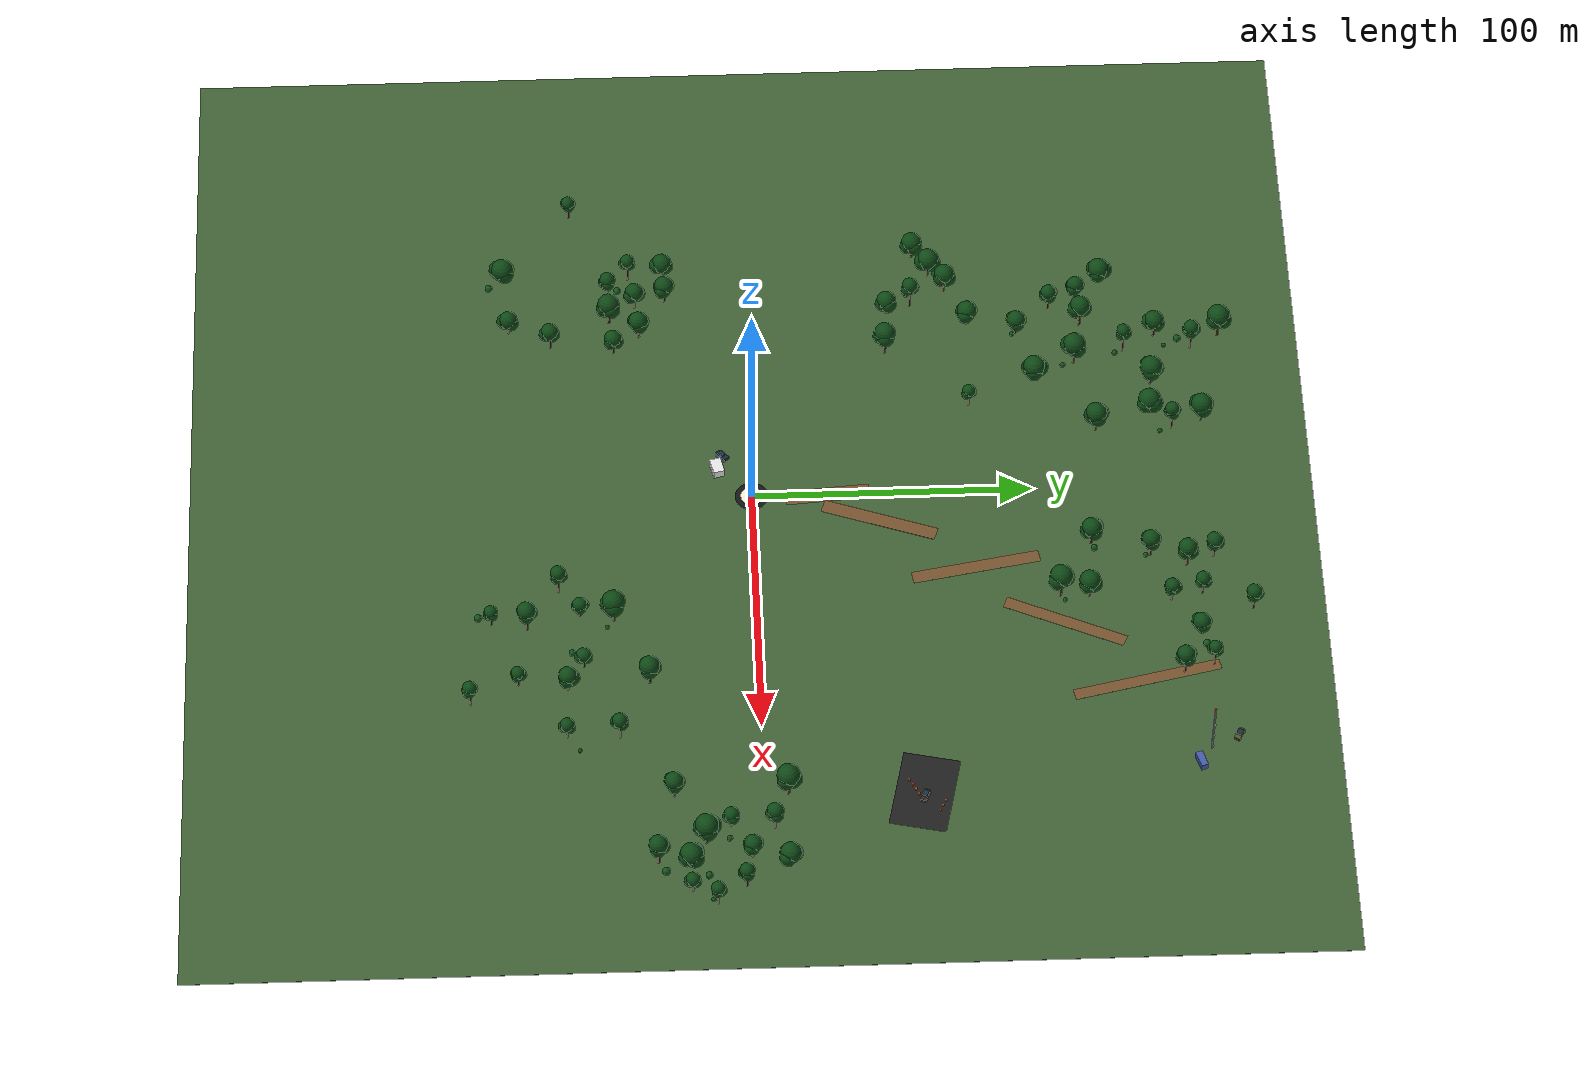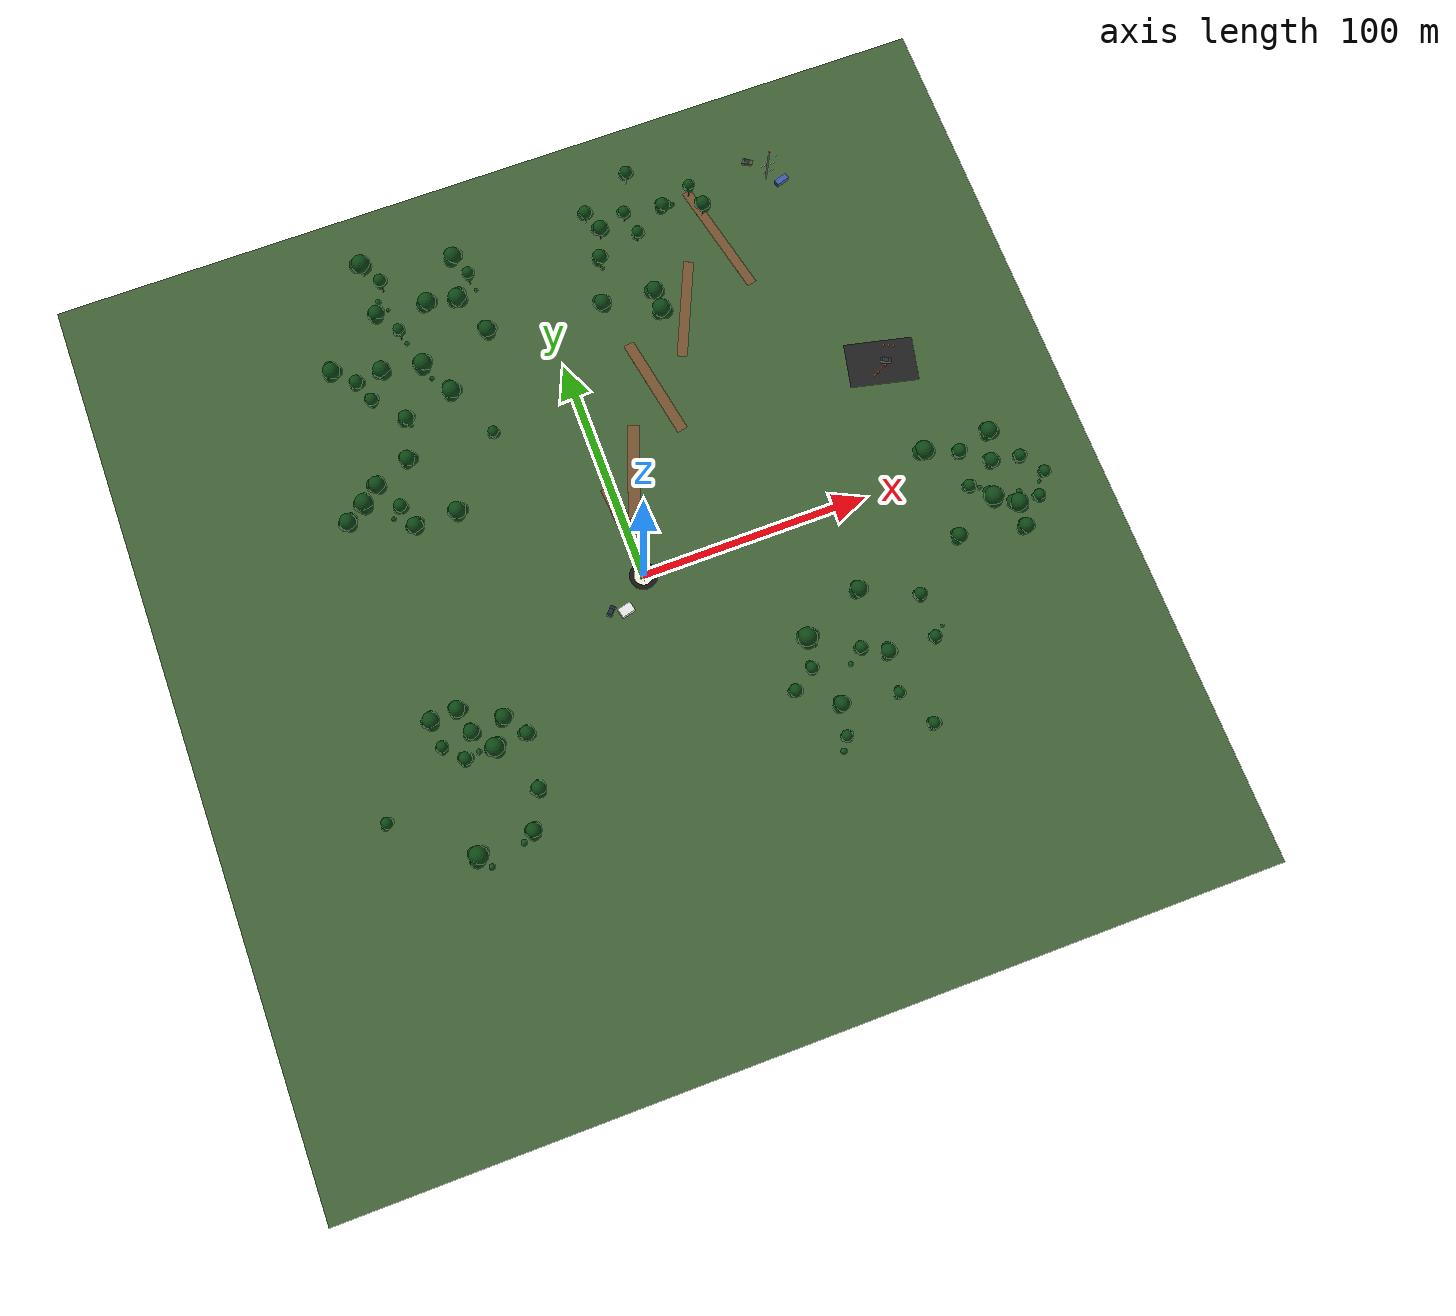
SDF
<?xml version='1.0' encoding='utf-8'?>
<sdf version="1.9">
  <world name="forest_monitoring">
    <physics type="ode">
      <max_step_size>0.004</max_step_size>
      <real_time_factor>1.0</real_time_factor>
      <real_time_update_rate>250</real_time_update_rate>
    </physics>
    <gravity>0 0 -9.8</gravity>
    <magnetic_field>6e-06 2.3e-05 -4.2e-05</magnetic_field>
    <atmosphere type="adiabatic" />
    <scene>
      <grid>false</grid>
      <ambient>0.6 0.6 0.6 1</ambient>
      <background>0.7 0.8 0.95 1</background>
      <shadows>true</shadows>
      <sky>
        <clouds />
        <time>11.0</time>
      </sky>
    </scene>
    <light name="sunUTC" type="directional">
      <pose>0 0 500 0 -0.5 -0.5</pose>
      <cast_shadows>true</cast_shadows>
      <intensity>1.2</intensity>
      <direction>-0.5 0.5 -0.8</direction>
      <diffuse>0.95 0.93 0.88 1</diffuse>
      <specular>0.3 0.3 0.25 1</specular>
    </light>
    <model name="grassland_base">
      <static>true</static>
      <pose>0 0 -0.05 0 0 0</pose>
      <link name="link">
        <collision name="collision">
          <geometry>
            <box>
              <size>400 400 0.1</size>
            </box>
          </geometry>
        </collision>
        <visual name="visual">
          <geometry>
            <box>
              <size>400 400 0.1</size>
            </box>
          </geometry>
          <material>
            <ambient>0.22 0.32 0.18 1</ambient>
            <diffuse>0.25 0.38 0.21 1</diffuse>
            <specular>0.1 0.1 0.1 1</specular>
            <pbr>
              <metal>
                <roughness>0.9</roughness>
                <metalness>0.0</metalness>
              </metal>
            </pbr>
          </material>
        </visual>
      </link>
    </model>
    <model name="trail_base">
      <static>true</static>
      <pose>0 27 0.01 0 0 0.08</pose>
      <link name="link">
        <visual name="visual">
          <geometry>
            <box>
              <size>6.0 30 0.03</size>
            </box>
          </geometry>
          <material>
            <ambient>0.36 0.25 0.14 1</ambient>
            <diffuse>0.46 0.32 0.18 1</diffuse>
            <specular>0.1 0.1 0.1 1</specular>
            <pbr>
              <metal>
                <roughness>1.0</roughness>
                <metalness>0.0</metalness>
              </metal>
            </pbr>
          </material>
        </visual>
      </link>
    </model>
    <model name="trail_curve_1">
      <static>true</static>
      <pose>12 45 0.012 0 0 -0.34</pose>
      <link name="link">
        <visual name="visual">
          <geometry>
            <box>
              <size>5.2 42 0.03</size>
            </box>
          </geometry>
          <material>
            <ambient>0.36 0.25 0.14 1</ambient>
            <diffuse>0.46 0.32 0.18 1</diffuse>
            <specular>0.1 0.1 0.1 1</specular>
            <pbr>
              <metal>
                <roughness>1.0</roughness>
                <metalness>0.0</metalness>
              </metal>
            </pbr>
          </material>
        </visual>
      </link>
    </model>
    <model name="trail_curve_2">
      <static>true</static>
      <pose>34 78 0.015 0 0 0.18</pose>
      <link name="link">
        <visual name="visual">
          <geometry>
            <box>
              <size>4.8 46 0.03</size>
            </box>
          </geometry>
          <material>
            <ambient>0.36 0.25 0.14 1</ambient>
            <diffuse>0.46 0.32 0.18 1</diffuse>
            <specular>0.1 0.1 0.1 1</specular>
            <pbr>
              <metal>
                <roughness>1.0</roughness>
                <metalness>0.0</metalness>
              </metal>
            </pbr>
          </material>
        </visual>
      </link>
    </model>
    <model name="trail_clearing_link">
      <static>true</static>
      <pose>59 108 0.018 0 0 -0.42</pose>
      <link name="link">
        <visual name="visual">
          <geometry>
            <box>
              <size>4.5 45 0.03</size>
            </box>
          </geometry>
          <material>
            <ambient>0.36 0.25 0.14 1</ambient>
            <diffuse>0.46 0.32 0.18 1</diffuse>
            <specular>0.1 0.1 0.1 1</specular>
            <pbr>
              <metal>
                <roughness>1.0</roughness>
                <metalness>0.0</metalness>
              </metal>
            </pbr>
          </material>
        </visual>
      </link>
    </model>
    <model name="trail_target_link">
      <static>true</static>
      <pose>85 135 0.02 0 0 0.22</pose>
      <link name="link">
        <visual name="visual">
          <geometry>
            <box>
              <size>4.3 53 0.03</size>
            </box>
          </geometry>
          <material>
            <ambient>0.36 0.25 0.14 1</ambient>
            <diffuse>0.46 0.32 0.18 1</diffuse>
            <specular>0.1 0.1 0.1 1</specular>
            <pbr>
              <metal>
                <roughness>1.0</roughness>
                <metalness>0.0</metalness>
              </metal>
            </pbr>
          </material>
        </visual>
      </link>
    </model>
    <model name="drone_landing_pad">
      <static>true</static>
      <pose>0 0 0.035 0 0 0</pose>
      <link name="link">
        <visual name="visual">
          <geometry>
            <cylinder>
              <radius>6.000</radius>
              <length>0.070</length>
            </cylinder>
          </geometry>
          <material>
            <ambient>0.05 0.05 0.05 1</ambient>
            <diffuse>0.08 0.08 0.08 1</diffuse>
            <specular>0.1 0.1 0.1 1</specular>
            <pbr>
              <metal>
                <roughness>0.8</roughness>
                <metalness>0.0</metalness>
              </metal>
            </pbr>
          </material>
        </visual>
      </link>
    </model>
    <model name="landing_pad_inner_ring">
      <static>true</static>
      <pose>0 0 0.085 0 0 0</pose>
      <link name="link">
        <visual name="visual">
          <geometry>
            <cylinder>
              <radius>4.000</radius>
              <length>0.025</length>
            </cylinder>
          </geometry>
          <material>
            <ambient>0.9 0.9 0.82 1</ambient>
            <diffuse>0.95 0.95 0.84 1</diffuse>
            <specular>0.1 0.1 0.1 1</specular>
            <pbr>
              <metal>
                <roughness>0.8</roughness>
                <metalness>0.0</metalness>
              </metal>
            </pbr>
          </material>
        </visual>
      </link>
    </model>
    <model name="landing_pad_h_mark_v">
      <static>true</static>
      <pose>0 0 0.11 0 0 0</pose>
      <link name="link">
        <visual name="visual">
          <geometry>
            <box>
              <size>0.7 4.6 0.025</size>
            </box>
          </geometry>
          <material>
            <ambient>0.04 0.04 0.04 1</ambient>
            <diffuse>0.04 0.04 0.04 1</diffuse>
            <specular>0.1 0.1 0.1 1</specular>
            <pbr>
              <metal>
                <roughness>0.8</roughness>
                <metalness>0.0</metalness>
              </metal>
            </pbr>
          </material>
        </visual>
      </link>
    </model>
    <model name="landing_pad_h_mark_l">
      <static>true</static>
      <pose>-1.25 0 0.115 0 0 0</pose>
      <link name="link">
        <visual name="visual">
          <geometry>
            <box>
              <size>0.7 2.6 0.025</size>
            </box>
          </geometry>
          <material>
            <ambient>0.04 0.04 0.04 1</ambient>
            <diffuse>0.04 0.04 0.04 1</diffuse>
            <specular>0.1 0.1 0.1 1</specular>
            <pbr>
              <metal>
                <roughness>0.8</roughness>
                <metalness>0.0</metalness>
              </metal>
            </pbr>
          </material>
        </visual>
      </link>
    </model>
    <model name="landing_pad_h_mark_r">
      <static>true</static>
      <pose>1.25 0 0.115 0 0 0</pose>
      <link name="link">
        <visual name="visual">
          <geometry>
            <box>
              <size>0.7 2.6 0.025</size>
            </box>
          </geometry>
          <material>
            <ambient>0.04 0.04 0.04 1</ambient>
            <diffuse>0.04 0.04 0.04 1</diffuse>
            <specular>0.1 0.1 0.1 1</specular>
            <pbr>
              <metal>
                <roughness>0.8</roughness>
                <metalness>0.0</metalness>
              </metal>
            </pbr>
          </material>
        </visual>
      </link>
    </model>
    <model name="control_cabin">
      <static>true</static>
      <pose>-12 -12 1.6 0 0 0.25</pose>
      <link name="link">
        <collision name="collision">
          <geometry>
            <box>
              <size>6 4 3.2</size>
            </box>
          </geometry>
        </collision>
        <visual name="visual">
          <geometry>
            <box>
              <size>6 4 3.2</size>
            </box>
          </geometry>
          <material>
            <ambient>0.8 0.8 0.8 1</ambient>
            <diffuse>0.9 0.9 0.9 1</diffuse>
            <specular>0.1 0.1 0.1 1</specular>
            <pbr>
              <metal>
                <roughness>0.2</roughness>
                <metalness>0.0</metalness>
              </metal>
            </pbr>
          </material>
        </visual>
      </link>
    </model>
    <model name="base_suv">
      <static>true</static>
      <pose>-18 -10 0.05 0 0 0.8</pose>
      <link name="link">
        <collision name="body_collision">
          <geometry>
            <box>
              <size>4.8 2.2 1.2</size>
            </box>
          </geometry>
        </collision>
        <visual name="body">
          <pose>0 0 0.75 0 0 0</pose>
          <geometry>
            <box>
              <size>4.8 2.2 1.2</size>
            </box>
          </geometry>
          <material>
            <ambient>0.10 0.16 0.22 1</ambient>
            <diffuse>0.10 0.16 0.22 1</diffuse>
            <specular>0.1 0.1 0.1 1</specular>
            <pbr>
              <metal>
                <roughness>0.45</roughness>
                <metalness>0.0</metalness>
              </metal>
            </pbr>
          </material>
        </visual>
        <visual name="cabin">
          <pose>-0.35 0 1.55 0 0 0</pose>
          <geometry>
            <box>
              <size>2.3 1.9 0.9</size>
            </box>
          </geometry>
          <material>
            <ambient>0.08 0.12 0.14 1</ambient>
            <diffuse>0.10 0.18 0.22 1</diffuse>
            <specular>0.1 0.1 0.1 1</specular>
            <pbr>
              <metal>
                <roughness>0.25</roughness>
                <metalness>0.0</metalness>
              </metal>
            </pbr>
          </material>
        </visual>
        <visual name="wheel_0_0">
          <pose>-1.55 -1.2 0.35 1.5708 0 0</pose>
          <geometry>
            <cylinder>
              <radius>0.42</radius>
              <length>0.28</length>
            </cylinder>
          </geometry>
          <material>
            <ambient>0.02 0.02 0.02 1</ambient>
            <diffuse>0.03 0.03 0.03 1</diffuse>
            <specular>0.1 0.1 0.1 1</specular>
            <pbr>
              <metal>
                <roughness>0.7</roughness>
                <metalness>0.0</metalness>
              </metal>
            </pbr>
          </material>
        </visual>
        <visual name="wheel_0_1">
          <pose>-1.55 1.2 0.35 1.5708 0 0</pose>
          <geometry>
            <cylinder>
              <radius>0.42</radius>
              <length>0.28</length>
            </cylinder>
          </geometry>
          <material>
            <ambient>0.02 0.02 0.02 1</ambient>
            <diffuse>0.03 0.03 0.03 1</diffuse>
            <specular>0.1 0.1 0.1 1</specular>
            <pbr>
              <metal>
                <roughness>0.7</roughness>
                <metalness>0.0</metalness>
              </metal>
            </pbr>
          </material>
        </visual>
        <visual name="wheel_1_0">
          <pose>1.55 -1.2 0.35 1.5708 0 0</pose>
          <geometry>
            <cylinder>
              <radius>0.42</radius>
              <length>0.28</length>
            </cylinder>
          </geometry>
          <material>
            <ambient>0.02 0.02 0.02 1</ambient>
            <diffuse>0.03 0.03 0.03 1</diffuse>
            <specular>0.1 0.1 0.1 1</specular>
            <pbr>
              <metal>
                <roughness>0.7</roughness>
                <metalness>0.0</metalness>
              </metal>
            </pbr>
          </material>
        </visual>
        <visual name="wheel_1_1">
          <pose>1.55 1.2 0.35 1.5708 0 0</pose>
          <geometry>
            <cylinder>
              <radius>0.42</radius>
              <length>0.28</length>
            </cylinder>
          </geometry>
          <material>
            <ambient>0.02 0.02 0.02 1</ambient>
            <diffuse>0.03 0.03 0.03 1</diffuse>
            <specular>0.1 0.1 0.1 1</specular>
            <pbr>
              <metal>
                <roughness>0.7</roughness>
                <metalness>0.0</metalness>
              </metal>
            </pbr>
          </material>
        </visual>
      </link>
    </model>
    <model name="monitoring_radio_tower">
      <static>true</static>
      <pose>115 155 0.0 0 0 0</pose>
      <link name="link">
        <collision name="mast_collision">
          <geometry>
            <cylinder>
              <radius>0.35</radius>
              <length>22</length>
            </cylinder>
          </geometry>
        </collision>
        <visual name="mast">
          <pose>0 0 11 0 0 0</pose>
          <geometry>
            <cylinder>
              <radius>0.35</radius>
              <length>22</length>
            </cylinder>
          </geometry>
          <material>
            <ambient>0.45 0.48 0.50 1</ambient>
            <diffuse>0.58 0.60 0.62 1</diffuse>
            <specular>0.1 0.1 0.1 1</specular>
            <pbr>
              <metal>
                <roughness>0.35</roughness>
                <metalness>0.0</metalness>
              </metal>
            </pbr>
          </material>
        </visual>
        <visual name="antenna_bar_0">
          <pose>0 0 6 0 1.5708 0</pose>
          <geometry>
            <cylinder>
              <radius>0.06</radius>
              <length>7</length>
            </cylinder>
          </geometry>
          <material>
            <ambient>0.82 0.82 0.78 1</ambient>
            <diffuse>0.92 0.92 0.86 1</diffuse>
            <specular>0.1 0.1 0.1 1</specular>
            <pbr>
              <metal>
                <roughness>0.4</roughness>
                <metalness>0.0</metalness>
              </metal>
            </pbr>
          </material>
        </visual>
        <visual name="antenna_bar_1">
          <pose>0 0 12 0 1.5708 0</pose>
          <geometry>
            <cylinder>
              <radius>0.06</radius>
              <length>7</length>
            </cylinder>
          </geometry>
          <material>
            <ambient>0.82 0.82 0.78 1</ambient>
            <diffuse>0.92 0.92 0.86 1</diffuse>
            <specular>0.1 0.1 0.1 1</specular>
            <pbr>
              <metal>
                <roughness>0.4</roughness>
                <metalness>0.0</metalness>
              </metal>
            </pbr>
          </material>
        </visual>
        <visual name="antenna_bar_2">
          <pose>0 0 18 0 1.5708 0</pose>
          <geometry>
            <cylinder>
              <radius>0.06</radius>
              <length>7</length>
            </cylinder>
          </geometry>
          <material>
            <ambient>0.82 0.82 0.78 1</ambient>
            <diffuse>0.92 0.92 0.86 1</diffuse>
            <specular>0.1 0.1 0.1 1</specular>
            <pbr>
              <metal>
                <roughness>0.4</roughness>
                <metalness>0.0</metalness>
              </metal>
            </pbr>
          </material>
        </visual>
        <visual name="beacon">
          <pose>0 0 22.6 0 0 0</pose>
          <geometry>
            <sphere>
              <radius>0.45</radius>
            </sphere>
          </geometry>
          <material>
            <ambient>0.9 0.06 0.04 1</ambient>
            <diffuse>1.0 0.08 0.05 1</diffuse>
            <specular>0.1 0.1 0.1 1</specular>
            <pbr>
              <metal>
                <roughness>0.2</roughness>
                <metalness>0.0</metalness>
              </metal>
            </pbr>
          </material>
        </visual>
      </link>
    </model>
    <model name="equipment_container">
      <static>true</static>
      <pose>121 151 1.3 0 0 0.3</pose>
      <link name="link">
        <collision name="collision">
          <geometry>
            <box>
              <size>6 2.5 2.6</size>
            </box>
          </geometry>
        </collision>
        <visual name="visual">
          <geometry>
            <box>
              <size>6 2.5 2.6</size>
            </box>
          </geometry>
          <material>
            <ambient>0.2 0.3 0.6 1</ambient>
            <diffuse>0.25 0.35 0.65 1</diffuse>
            <specular>0.1 0.1 0.1 1</specular>
            <pbr>
              <metal>
                <roughness>0.4</roughness>
                <metalness>0.0</metalness>
              </metal>
            </pbr>
          </material>
        </visual>
      </link>
    </model>
    <model name="target_pickup">
      <static>true</static>
      <pose>110 165 0.0 0 0 -0.5</pose>
      <link name="link">
        <collision name="body_collision">
          <geometry>
            <box>
              <size>4.8 2.2 1.2</size>
            </box>
          </geometry>
        </collision>
        <visual name="body">
          <pose>0 0 0.75 0 0 0</pose>
          <geometry>
            <box>
              <size>4.8 2.2 1.2</size>
            </box>
          </geometry>
          <material>
            <ambient>0.30 0.34 0.18 1</ambient>
            <diffuse>0.30 0.34 0.18 1</diffuse>
            <specular>0.1 0.1 0.1 1</specular>
            <pbr>
              <metal>
                <roughness>0.45</roughness>
                <metalness>0.0</metalness>
              </metal>
            </pbr>
          </material>
        </visual>
        <visual name="cabin">
          <pose>-0.35 0 1.55 0 0 0</pose>
          <geometry>
            <box>
              <size>2.3 1.9 0.9</size>
            </box>
          </geometry>
          <material>
            <ambient>0.08 0.12 0.14 1</ambient>
            <diffuse>0.10 0.18 0.22 1</diffuse>
            <specular>0.1 0.1 0.1 1</specular>
            <pbr>
              <metal>
                <roughness>0.25</roughness>
                <metalness>0.0</metalness>
              </metal>
            </pbr>
          </material>
        </visual>
        <visual name="wheel_0_0">
          <pose>-1.55 -1.2 0.35 1.5708 0 0</pose>
          <geometry>
            <cylinder>
              <radius>0.42</radius>
              <length>0.28</length>
            </cylinder>
          </geometry>
          <material>
            <ambient>0.02 0.02 0.02 1</ambient>
            <diffuse>0.03 0.03 0.03 1</diffuse>
            <specular>0.1 0.1 0.1 1</specular>
            <pbr>
              <metal>
                <roughness>0.7</roughness>
                <metalness>0.0</metalness>
              </metal>
            </pbr>
          </material>
        </visual>
        <visual name="wheel_0_1">
          <pose>-1.55 1.2 0.35 1.5708 0 0</pose>
          <geometry>
            <cylinder>
              <radius>0.42</radius>
              <length>0.28</length>
            </cylinder>
          </geometry>
          <material>
            <ambient>0.02 0.02 0.02 1</ambient>
            <diffuse>0.03 0.03 0.03 1</diffuse>
            <specular>0.1 0.1 0.1 1</specular>
            <pbr>
              <metal>
                <roughness>0.7</roughness>
                <metalness>0.0</metalness>
              </metal>
            </pbr>
          </material>
        </visual>
        <visual name="wheel_1_0">
          <pose>1.55 -1.2 0.35 1.5708 0 0</pose>
          <geometry>
            <cylinder>
              <radius>0.42</radius>
              <length>0.28</length>
            </cylinder>
          </geometry>
          <material>
            <ambient>0.02 0.02 0.02 1</ambient>
            <diffuse>0.03 0.03 0.03 1</diffuse>
            <specular>0.1 0.1 0.1 1</specular>
            <pbr>
              <metal>
                <roughness>0.7</roughness>
                <metalness>0.0</metalness>
              </metal>
            </pbr>
          </material>
        </visual>
        <visual name="wheel_1_1">
          <pose>1.55 1.2 0.35 1.5708 0 0</pose>
          <geometry>
            <cylinder>
              <radius>0.42</radius>
              <length>0.28</length>
            </cylinder>
          </geometry>
          <material>
            <ambient>0.02 0.02 0.02 1</ambient>
            <diffuse>0.03 0.03 0.03 1</diffuse>
            <specular>0.1 0.1 0.1 1</specular>
            <pbr>
              <metal>
                <roughness>0.7</roughness>
                <metalness>0.0</metalness>
              </metal>
            </pbr>
          </material>
        </visual>
      </link>
    </model>
    <model name="burnt_ground_patch">
      <static>true</static>
      <pose>130 55 0.01 0 0 -0.22</pose>
      <link name="link">
        <visual name="visual">
          <geometry>
            <box>
              <size>30 20 0.02</size>
            </box>
          </geometry>
          <material>
            <ambient>0.1 0.1 0.1 1</ambient>
            <diffuse>0.12 0.12 0.12 1</diffuse>
            <specular>0.1 0.1 0.1 1</specular>
            <pbr>
              <metal>
                <roughness>1.0</roughness>
                <metalness>0.0</metalness>
              </metal>
            </pbr>
          </material>
        </visual>
      </link>
    </model>
    <model name="damaged_vehicle">
      <static>true</static>
      <pose>132 55 0.05 0 0 -0.4</pose>
      <link name="link">
        <collision name="body_collision">
          <geometry>
            <box>
              <size>4.8 2.2 1.2</size>
            </box>
          </geometry>
        </collision>
        <visual name="body">
          <pose>0 0 0.75 0 0 0</pose>
          <geometry>
            <box>
              <size>4.8 2.2 1.2</size>
            </box>
          </geometry>
          <material>
            <ambient>0.18 0.13 0.11 1</ambient>
            <diffuse>0.18 0.13 0.11 1</diffuse>
            <specular>0.1 0.1 0.1 1</specular>
            <pbr>
              <metal>
                <roughness>0.45</roughness>
                <metalness>0.0</metalness>
              </metal>
            </pbr>
          </material>
        </visual>
        <visual name="cabin">
          <pose>-0.35 0 1.55 0 0 0</pose>
          <geometry>
            <box>
              <size>2.3 1.9 0.9</size>
            </box>
          </geometry>
          <material>
            <ambient>0.08 0.12 0.14 1</ambient>
            <diffuse>0.10 0.18 0.22 1</diffuse>
            <specular>0.1 0.1 0.1 1</specular>
            <pbr>
              <metal>
                <roughness>0.25</roughness>
                <metalness>0.0</metalness>
              </metal>
            </pbr>
          </material>
        </visual>
        <visual name="wheel_0_0">
          <pose>-1.55 -1.2 0.35 1.5708 0 0</pose>
          <geometry>
            <cylinder>
              <radius>0.42</radius>
              <length>0.28</length>
            </cylinder>
          </geometry>
          <material>
            <ambient>0.02 0.02 0.02 1</ambient>
            <diffuse>0.03 0.03 0.03 1</diffuse>
            <specular>0.1 0.1 0.1 1</specular>
            <pbr>
              <metal>
                <roughness>0.7</roughness>
                <metalness>0.0</metalness>
              </metal>
            </pbr>
          </material>
        </visual>
        <visual name="wheel_0_1">
          <pose>-1.55 1.2 0.35 1.5708 0 0</pose>
          <geometry>
            <cylinder>
              <radius>0.42</radius>
              <length>0.28</length>
            </cylinder>
          </geometry>
          <material>
            <ambient>0.02 0.02 0.02 1</ambient>
            <diffuse>0.03 0.03 0.03 1</diffuse>
            <specular>0.1 0.1 0.1 1</specular>
            <pbr>
              <metal>
                <roughness>0.7</roughness>
                <metalness>0.0</metalness>
              </metal>
            </pbr>
          </material>
        </visual>
        <visual name="wheel_1_0">
          <pose>1.55 -1.2 0.35 1.5708 0 0</pose>
          <geometry>
            <cylinder>
              <radius>0.42</radius>
              <length>0.28</length>
            </cylinder>
          </geometry>
          <material>
            <ambient>0.02 0.02 0.02 1</ambient>
            <diffuse>0.03 0.03 0.03 1</diffuse>
            <specular>0.1 0.1 0.1 1</specular>
            <pbr>
              <metal>
                <roughness>0.7</roughness>
                <metalness>0.0</metalness>
              </metal>
            </pbr>
          </material>
        </visual>
        <visual name="wheel_1_1">
          <pose>1.55 1.2 0.35 1.5708 0 0</pose>
          <geometry>
            <cylinder>
              <radius>0.42</radius>
              <length>0.28</length>
            </cylinder>
          </geometry>
          <material>
            <ambient>0.02 0.02 0.02 1</ambient>
            <diffuse>0.03 0.03 0.03 1</diffuse>
            <specular>0.1 0.1 0.1 1</specular>
            <pbr>
              <metal>
                <roughness>0.7</roughness>
                <metalness>0.0</metalness>
              </metal>
            </pbr>
          </material>
        </visual>
      </link>
    </model>
    <model name="hazard_barrel_0">
      <static>true</static>
      <pose>125 50 0.45 0 0 0</pose>
      <link name="link">
        <collision name="collision">
          <geometry>
            <cylinder>
              <radius>0.350</radius>
              <length>0.900</length>
            </cylinder>
          </geometry>
        </collision>
        <visual name="visual">
          <geometry>
            <cylinder>
              <radius>0.350</radius>
              <length>0.900</length>
            </cylinder>
          </geometry>
          <material>
            <ambient>0.9 0.22 0.04 1</ambient>
            <diffuse>1.0 0.32 0.06 1</diffuse>
            <specular>0.1 0.1 0.1 1</specular>
            <pbr>
              <metal>
                <roughness>0.8</roughness>
                <metalness>0.0</metalness>
              </metal>
            </pbr>
          </material>
        </visual>
      </link>
    </model>
    <model name="hazard_barrel_1">
      <static>true</static>
      <pose>127 51 0.45 0 0 0</pose>
      <link name="link">
        <collision name="collision">
          <geometry>
            <cylinder>
              <radius>0.350</radius>
              <length>0.900</length>
            </cylinder>
          </geometry>
        </collision>
        <visual name="visual">
          <geometry>
            <cylinder>
              <radius>0.350</radius>
              <length>0.900</length>
            </cylinder>
          </geometry>
          <material>
            <ambient>0.9 0.22 0.04 1</ambient>
            <diffuse>1.0 0.32 0.06 1</diffuse>
            <specular>0.1 0.1 0.1 1</specular>
            <pbr>
              <metal>
                <roughness>0.8</roughness>
                <metalness>0.0</metalness>
              </metal>
            </pbr>
          </material>
        </visual>
      </link>
    </model>
    <model name="hazard_barrel_2">
      <static>true</static>
      <pose>129 52 0.45 0 0 0</pose>
      <link name="link">
        <collision name="collision">
          <geometry>
            <cylinder>
              <radius>0.350</radius>
              <length>0.900</length>
            </cylinder>
          </geometry>
        </collision>
        <visual name="visual">
          <geometry>
            <cylinder>
              <radius>0.350</radius>
              <length>0.900</length>
            </cylinder>
          </geometry>
          <material>
            <ambient>0.9 0.22 0.04 1</ambient>
            <diffuse>1.0 0.32 0.06 1</diffuse>
            <specular>0.1 0.1 0.1 1</specular>
            <pbr>
              <metal>
                <roughness>0.8</roughness>
                <metalness>0.0</metalness>
              </metal>
            </pbr>
          </material>
        </visual>
      </link>
    </model>
    <model name="hazard_barrel_3">
      <static>true</static>
      <pose>131 53 0.45 0 0 0</pose>
      <link name="link">
        <collision name="collision">
          <geometry>
            <cylinder>
              <radius>0.350</radius>
              <length>0.900</length>
            </cylinder>
          </geometry>
        </collision>
        <visual name="visual">
          <geometry>
            <cylinder>
              <radius>0.350</radius>
              <length>0.900</length>
            </cylinder>
          </geometry>
          <material>
            <ambient>0.9 0.22 0.04 1</ambient>
            <diffuse>1.0 0.32 0.06 1</diffuse>
            <specular>0.1 0.1 0.1 1</specular>
            <pbr>
              <metal>
                <roughness>0.8</roughness>
                <metalness>0.0</metalness>
              </metal>
            </pbr>
          </material>
        </visual>
      </link>
    </model>
    <model name="hazard_cone_0">
      <static>true</static>
      <pose>138 60 0.325 0 0 0</pose>
      <link name="link">
        <collision name="collision">
          <geometry>
            <cylinder>
              <radius>0.280</radius>
              <length>0.650</length>
            </cylinder>
          </geometry>
        </collision>
        <visual name="visual">
          <geometry>
            <cylinder>
              <radius>0.280</radius>
              <length>0.650</length>
            </cylinder>
          </geometry>
          <material>
            <ambient>0.95 0.32 0.03 1</ambient>
            <diffuse>1.0 0.45 0.06 1</diffuse>
            <specular>0.1 0.1 0.1 1</specular>
            <pbr>
              <metal>
                <roughness>0.8</roughness>
                <metalness>0.0</metalness>
              </metal>
            </pbr>
          </material>
        </visual>
      </link>
    </model>
    <model name="hazard_cone_1">
      <static>true</static>
      <pose>136 61 0.325 0 0 0</pose>
      <link name="link">
        <collision name="collision">
          <geometry>
            <cylinder>
              <radius>0.280</radius>
              <length>0.650</length>
            </cylinder>
          </geometry>
        </collision>
        <visual name="visual">
          <geometry>
            <cylinder>
              <radius>0.280</radius>
              <length>0.650</length>
            </cylinder>
          </geometry>
          <material>
            <ambient>0.95 0.32 0.03 1</ambient>
            <diffuse>1.0 0.45 0.06 1</diffuse>
            <specular>0.1 0.1 0.1 1</specular>
            <pbr>
              <metal>
                <roughness>0.8</roughness>
                <metalness>0.0</metalness>
              </metal>
            </pbr>
          </material>
        </visual>
      </link>
    </model>
    <model name="hazard_cone_2">
      <static>true</static>
      <pose>134 62 0.325 0 0 0</pose>
      <link name="link">
        <collision name="collision">
          <geometry>
            <cylinder>
              <radius>0.280</radius>
              <length>0.650</length>
            </cylinder>
          </geometry>
        </collision>
        <visual name="visual">
          <geometry>
            <cylinder>
              <radius>0.280</radius>
              <length>0.650</length>
            </cylinder>
          </geometry>
          <material>
            <ambient>0.95 0.32 0.03 1</ambient>
            <diffuse>1.0 0.45 0.06 1</diffuse>
            <specular>0.1 0.1 0.1 1</specular>
            <pbr>
              <metal>
                <roughness>0.8</roughness>
                <metalness>0.0</metalness>
              </metal>
            </pbr>
          </material>
        </visual>
      </link>
    </model>
    <model name="tree_0">
      <static>true</static>
      <pose>-99.95 67.79 0 0 0 4.51</pose>
      <link name="link">
        <visual name="trunk">
          <pose>0 0 5.04 0 0 0</pose>
          <geometry>
            <cylinder>
              <radius>0.48</radius>
              <length>10.08</length>
            </cylinder>
          </geometry>
          <material>
            <ambient>0.18 0.11 0.06 1</ambient>
            <diffuse>0.24 0.15 0.08 1</diffuse>
            <specular>0.1 0.1 0.1 1</specular>
            <pbr>
              <metal>
                <roughness>0.9</roughness>
                <metalness>0.0</metalness>
              </metal>
            </pbr>
          </material>
        </visual>
        <visual name="canopy_0">
          <pose>0.00 0.00 8.87 0 0 0</pose>
          <geometry>
            <sphere>
              <radius>4.02</radius>
            </sphere>
          </geometry>
          <material>
            <ambient>0.03 0.16 0.05 1</ambient>
            <diffuse>0.05 0.28 0.08 1</diffuse>
            <specular>0.1 0.1 0.1 1</specular>
            <pbr>
              <metal>
                <roughness>1.0</roughness>
                <metalness>0.0</metalness>
              </metal>
            </pbr>
          </material>
        </visual>
        <visual name="canopy_1">
          <pose>1.69 0.48 7.86 0 0 0</pose>
          <geometry>
            <sphere>
              <radius>3.29</radius>
            </sphere>
          </geometry>
          <material>
            <ambient>0.03 0.16 0.05 1</ambient>
            <diffuse>0.05 0.28 0.08 1</diffuse>
            <specular>0.1 0.1 0.1 1</specular>
            <pbr>
              <metal>
                <roughness>1.0</roughness>
                <metalness>0.0</metalness>
              </metal>
            </pbr>
          </material>
        </visual>
        <visual name="canopy_2">
          <pose>-1.53 0.32 7.66 0 0 0</pose>
          <geometry>
            <sphere>
              <radius>3.13</radius>
            </sphere>
          </geometry>
          <material>
            <ambient>0.03 0.16 0.05 1</ambient>
            <diffuse>0.05 0.28 0.08 1</diffuse>
            <specular>0.1 0.1 0.1 1</specular>
            <pbr>
              <metal>
                <roughness>1.0</roughness>
                <metalness>0.0</metalness>
              </metal>
            </pbr>
          </material>
        </visual>
        <visual name="canopy_3">
          <pose>0.16 -1.69 7.46 0 0 0</pose>
          <geometry>
            <sphere>
              <radius>3.05</radius>
            </sphere>
          </geometry>
          <material>
            <ambient>0.03 0.16 0.05 1</ambient>
            <diffuse>0.05 0.28 0.08 1</diffuse>
            <specular>0.1 0.1 0.1 1</specular>
            <pbr>
              <metal>
                <roughness>1.0</roughness>
                <metalness>0.0</metalness>
              </metal>
            </pbr>
          </material>
        </visual>
      </link>
    </model>
    <model name="tree_1">
      <static>true</static>
      <pose>-49.59 103.68 0 0 0 1.43</pose>
      <link name="link">
        <visual name="trunk">
          <pose>0 0 4.39 0 0 0</pose>
          <geometry>
            <cylinder>
              <radius>0.49</radius>
              <length>8.79</length>
            </cylinder>
          </geometry>
          <material>
            <ambient>0.18 0.11 0.06 1</ambient>
            <diffuse>0.24 0.15 0.08 1</diffuse>
            <specular>0.1 0.1 0.1 1</specular>
            <pbr>
              <metal>
                <roughness>0.9</roughness>
                <metalness>0.0</metalness>
              </metal>
            </pbr>
          </material>
        </visual>
        <visual name="canopy_0">
          <pose>0.00 0.00 7.73 0 0 0</pose>
          <geometry>
            <sphere>
              <radius>4.06</radius>
            </sphere>
          </geometry>
          <material>
            <ambient>0.03 0.16 0.05 1</ambient>
            <diffuse>0.05 0.28 0.08 1</diffuse>
            <specular>0.1 0.1 0.1 1</specular>
            <pbr>
              <metal>
                <roughness>1.0</roughness>
                <metalness>0.0</metalness>
              </metal>
            </pbr>
          </material>
        </visual>
        <visual name="canopy_1">
          <pose>1.70 0.49 6.86 0 0 0</pose>
          <geometry>
            <sphere>
              <radius>3.33</radius>
            </sphere>
          </geometry>
          <material>
            <ambient>0.03 0.16 0.05 1</ambient>
            <diffuse>0.05 0.28 0.08 1</diffuse>
            <specular>0.1 0.1 0.1 1</specular>
            <pbr>
              <metal>
                <roughness>1.0</roughness>
                <metalness>0.0</metalness>
              </metal>
            </pbr>
          </material>
        </visual>
        <visual name="canopy_2">
          <pose>-1.54 0.32 6.68 0 0 0</pose>
          <geometry>
            <sphere>
              <radius>3.17</radius>
            </sphere>
          </geometry>
          <material>
            <ambient>0.03 0.16 0.05 1</ambient>
            <diffuse>0.05 0.28 0.08 1</diffuse>
            <specular>0.1 0.1 0.1 1</specular>
            <pbr>
              <metal>
                <roughness>1.0</roughness>
                <metalness>0.0</metalness>
              </metal>
            </pbr>
          </material>
        </visual>
        <visual name="canopy_3">
          <pose>0.16 -1.70 6.50 0 0 0</pose>
          <geometry>
            <sphere>
              <radius>3.08</radius>
            </sphere>
          </geometry>
          <material>
            <ambient>0.03 0.16 0.05 1</ambient>
            <diffuse>0.05 0.28 0.08 1</diffuse>
            <specular>0.1 0.1 0.1 1</specular>
            <pbr>
              <metal>
                <roughness>1.0</roughness>
                <metalness>0.0</metalness>
              </metal>
            </pbr>
          </material>
        </visual>
      </link>
    </model>
    <model name="tree_2">
      <static>true</static>
      <pose>-76.65 80.83 0 0 0 5.70</pose>
      <link name="link">
        <visual name="trunk">
          <pose>0 0 4.15 0 0 0</pose>
          <geometry>
            <cylinder>
              <radius>0.44</radius>
              <length>8.31</length>
            </cylinder>
          </geometry>
          <material>
            <ambient>0.18 0.11 0.06 1</ambient>
            <diffuse>0.24 0.15 0.08 1</diffuse>
            <specular>0.1 0.1 0.1 1</specular>
            <pbr>
              <metal>
                <roughness>0.9</roughness>
                <metalness>0.0</metalness>
              </metal>
            </pbr>
          </material>
        </visual>
        <visual name="canopy_0">
          <pose>0.00 0.00 7.31 0 0 0</pose>
          <geometry>
            <sphere>
              <radius>3.64</radius>
            </sphere>
          </geometry>
          <material>
            <ambient>0.03 0.16 0.05 1</ambient>
            <diffuse>0.05 0.28 0.08 1</diffuse>
            <specular>0.1 0.1 0.1 1</specular>
            <pbr>
              <metal>
                <roughness>1.0</roughness>
                <metalness>0.0</metalness>
              </metal>
            </pbr>
          </material>
        </visual>
        <visual name="canopy_1">
          <pose>1.53 0.44 6.48 0 0 0</pose>
          <geometry>
            <sphere>
              <radius>2.98</radius>
            </sphere>
          </geometry>
          <material>
            <ambient>0.03 0.16 0.05 1</ambient>
            <diffuse>0.05 0.28 0.08 1</diffuse>
            <specular>0.1 0.1 0.1 1</specular>
            <pbr>
              <metal>
                <roughness>1.0</roughness>
                <metalness>0.0</metalness>
              </metal>
            </pbr>
          </material>
        </visual>
        <visual name="canopy_2">
          <pose>-1.38 0.29 6.31 0 0 0</pose>
          <geometry>
            <sphere>
              <radius>2.84</radius>
            </sphere>
          </geometry>
          <material>
            <ambient>0.03 0.16 0.05 1</ambient>
            <diffuse>0.05 0.28 0.08 1</diffuse>
            <specular>0.1 0.1 0.1 1</specular>
            <pbr>
              <metal>
                <roughness>1.0</roughness>
                <metalness>0.0</metalness>
              </metal>
            </pbr>
          </material>
        </visual>
        <visual name="canopy_3">
          <pose>0.15 -1.53 6.15 0 0 0</pose>
          <geometry>
            <sphere>
              <radius>2.76</radius>
            </sphere>
          </geometry>
          <material>
            <ambient>0.03 0.16 0.05 1</ambient>
            <diffuse>0.05 0.28 0.08 1</diffuse>
            <specular>0.1 0.1 0.1 1</specular>
            <pbr>
              <metal>
                <roughness>1.0</roughness>
                <metalness>0.0</metalness>
              </metal>
            </pbr>
          </material>
        </visual>
      </link>
    </model>
    <model name="tree_3">
      <static>true</static>
      <pose>-57.14 118.49 0 0 0 4.03</pose>
      <link name="link">
        <visual name="trunk">
          <pose>0 0 6.04 0 0 0</pose>
          <geometry>
            <cylinder>
              <radius>0.49</radius>
              <length>12.07</length>
            </cylinder>
          </geometry>
          <material>
            <ambient>0.18 0.11 0.06 1</ambient>
            <diffuse>0.24 0.15 0.08 1</diffuse>
            <specular>0.1 0.1 0.1 1</specular>
            <pbr>
              <metal>
                <roughness>0.9</roughness>
                <metalness>0.0</metalness>
              </metal>
            </pbr>
          </material>
        </visual>
        <visual name="canopy_0">
          <pose>0.00 0.00 10.62 0 0 0</pose>
          <geometry>
            <sphere>
              <radius>4.08</radius>
            </sphere>
          </geometry>
          <material>
            <ambient>0.03 0.16 0.05 1</ambient>
            <diffuse>0.05 0.28 0.08 1</diffuse>
            <specular>0.1 0.1 0.1 1</specular>
            <pbr>
              <metal>
                <roughness>1.0</roughness>
                <metalness>0.0</metalness>
              </metal>
            </pbr>
          </material>
        </visual>
        <visual name="canopy_1">
          <pose>1.71 0.49 9.42 0 0 0</pose>
          <geometry>
            <sphere>
              <radius>3.34</radius>
            </sphere>
          </geometry>
          <material>
            <ambient>0.03 0.16 0.05 1</ambient>
            <diffuse>0.05 0.28 0.08 1</diffuse>
            <specular>0.1 0.1 0.1 1</specular>
            <pbr>
              <metal>
                <roughness>1.0</roughness>
                <metalness>0.0</metalness>
              </metal>
            </pbr>
          </material>
        </visual>
        <visual name="canopy_2">
          <pose>-1.55 0.33 9.18 0 0 0</pose>
          <geometry>
            <sphere>
              <radius>3.18</radius>
            </sphere>
          </geometry>
          <material>
            <ambient>0.03 0.16 0.05 1</ambient>
            <diffuse>0.05 0.28 0.08 1</diffuse>
            <specular>0.1 0.1 0.1 1</specular>
            <pbr>
              <metal>
                <roughness>1.0</roughness>
                <metalness>0.0</metalness>
              </metal>
            </pbr>
          </material>
        </visual>
        <visual name="canopy_3">
          <pose>0.16 -1.71 8.93 0 0 0</pose>
          <geometry>
            <sphere>
              <radius>3.10</radius>
            </sphere>
          </geometry>
          <material>
            <ambient>0.03 0.16 0.05 1</ambient>
            <diffuse>0.05 0.28 0.08 1</diffuse>
            <specular>0.1 0.1 0.1 1</specular>
            <pbr>
              <metal>
                <roughness>1.0</roughness>
                <metalness>0.0</metalness>
              </metal>
            </pbr>
          </material>
        </visual>
      </link>
    </model>
    <model name="tree_4">
      <static>true</static>
      <pose>-92.36 73.34 0 0 0 2.49</pose>
      <link name="link">
        <visual name="trunk">
          <pose>0 0 5.38 0 0 0</pose>
          <geometry>
            <cylinder>
              <radius>0.45</radius>
              <length>10.75</length>
            </cylinder>
          </geometry>
          <material>
            <ambient>0.18 0.11 0.06 1</ambient>
            <diffuse>0.24 0.15 0.08 1</diffuse>
            <specular>0.1 0.1 0.1 1</specular>
            <pbr>
              <metal>
                <roughness>0.9</roughness>
                <metalness>0.0</metalness>
              </metal>
            </pbr>
          </material>
        </visual>
        <visual name="canopy_0">
          <pose>0.00 0.00 9.46 0 0 0</pose>
          <geometry>
            <sphere>
              <radius>3.71</radius>
            </sphere>
          </geometry>
          <material>
            <ambient>0.03 0.16 0.05 1</ambient>
            <diffuse>0.05 0.28 0.08 1</diffuse>
            <specular>0.1 0.1 0.1 1</specular>
            <pbr>
              <metal>
                <roughness>1.0</roughness>
                <metalness>0.0</metalness>
              </metal>
            </pbr>
          </material>
        </visual>
        <visual name="canopy_1">
          <pose>1.56 0.45 8.39 0 0 0</pose>
          <geometry>
            <sphere>
              <radius>3.04</radius>
            </sphere>
          </geometry>
          <material>
            <ambient>0.03 0.16 0.05 1</ambient>
            <diffuse>0.05 0.28 0.08 1</diffuse>
            <specular>0.1 0.1 0.1 1</specular>
            <pbr>
              <metal>
                <roughness>1.0</roughness>
                <metalness>0.0</metalness>
              </metal>
            </pbr>
          </material>
        </visual>
        <visual name="canopy_2">
          <pose>-1.41 0.30 8.17 0 0 0</pose>
          <geometry>
            <sphere>
              <radius>2.89</radius>
            </sphere>
          </geometry>
          <material>
            <ambient>0.03 0.16 0.05 1</ambient>
            <diffuse>0.05 0.28 0.08 1</diffuse>
            <specular>0.1 0.1 0.1 1</specular>
            <pbr>
              <metal>
                <roughness>1.0</roughness>
                <metalness>0.0</metalness>
              </metal>
            </pbr>
          </material>
        </visual>
        <visual name="canopy_3">
          <pose>0.15 -1.56 7.96 0 0 0</pose>
          <geometry>
            <sphere>
              <radius>2.82</radius>
            </sphere>
          </geometry>
          <material>
            <ambient>0.03 0.16 0.05 1</ambient>
            <diffuse>0.05 0.28 0.08 1</diffuse>
            <specular>0.1 0.1 0.1 1</specular>
            <pbr>
              <metal>
                <roughness>1.0</roughness>
                <metalness>0.0</metalness>
              </metal>
            </pbr>
          </material>
        </visual>
      </link>
    </model>
    <model name="tree_5">
      <static>true</static>
      <pose>-108.78 62.20 0 0 0 0.30</pose>
      <link name="link">
        <visual name="trunk">
          <pose>0 0 4.67 0 0 0</pose>
          <geometry>
            <cylinder>
              <radius>0.44</radius>
              <length>9.33</length>
            </cylinder>
          </geometry>
          <material>
            <ambient>0.18 0.11 0.06 1</ambient>
            <diffuse>0.24 0.15 0.08 1</diffuse>
            <specular>0.1 0.1 0.1 1</specular>
            <pbr>
              <metal>
                <roughness>0.9</roughness>
                <metalness>0.0</metalness>
              </metal>
            </pbr>
          </material>
        </visual>
        <visual name="canopy_0">
          <pose>0.00 0.00 8.21 0 0 0</pose>
          <geometry>
            <sphere>
              <radius>3.70</radius>
            </sphere>
          </geometry>
          <material>
            <ambient>0.03 0.16 0.05 1</ambient>
            <diffuse>0.05 0.28 0.08 1</diffuse>
            <specular>0.1 0.1 0.1 1</specular>
            <pbr>
              <metal>
                <roughness>1.0</roughness>
                <metalness>0.0</metalness>
              </metal>
            </pbr>
          </material>
        </visual>
        <visual name="canopy_1">
          <pose>1.55 0.44 7.28 0 0 0</pose>
          <geometry>
            <sphere>
              <radius>3.03</radius>
            </sphere>
          </geometry>
          <material>
            <ambient>0.03 0.16 0.05 1</ambient>
            <diffuse>0.05 0.28 0.08 1</diffuse>
            <specular>0.1 0.1 0.1 1</specular>
            <pbr>
              <metal>
                <roughness>1.0</roughness>
                <metalness>0.0</metalness>
              </metal>
            </pbr>
          </material>
        </visual>
        <visual name="canopy_2">
          <pose>-1.41 0.30 7.09 0 0 0</pose>
          <geometry>
            <sphere>
              <radius>2.89</radius>
            </sphere>
          </geometry>
          <material>
            <ambient>0.03 0.16 0.05 1</ambient>
            <diffuse>0.05 0.28 0.08 1</diffuse>
            <specular>0.1 0.1 0.1 1</specular>
            <pbr>
              <metal>
                <roughness>1.0</roughness>
                <metalness>0.0</metalness>
              </metal>
            </pbr>
          </material>
        </visual>
        <visual name="canopy_3">
          <pose>0.15 -1.55 6.91 0 0 0</pose>
          <geometry>
            <sphere>
              <radius>2.81</radius>
            </sphere>
          </geometry>
          <material>
            <ambient>0.03 0.16 0.05 1</ambient>
            <diffuse>0.05 0.28 0.08 1</diffuse>
            <specular>0.1 0.1 0.1 1</specular>
            <pbr>
              <metal>
                <roughness>1.0</roughness>
                <metalness>0.0</metalness>
              </metal>
            </pbr>
          </material>
        </visual>
      </link>
    </model>
    <model name="tree_6">
      <static>true</static>
      <pose>-71.57 98.38 0 0 0 3.49</pose>
      <link name="link">
        <visual name="trunk">
          <pose>0 0 4.31 0 0 0</pose>
          <geometry>
            <cylinder>
              <radius>0.41</radius>
              <length>8.62</length>
            </cylinder>
          </geometry>
          <material>
            <ambient>0.18 0.11 0.06 1</ambient>
            <diffuse>0.24 0.15 0.08 1</diffuse>
            <specular>0.1 0.1 0.1 1</specular>
            <pbr>
              <metal>
                <roughness>0.9</roughness>
                <metalness>0.0</metalness>
              </metal>
            </pbr>
          </material>
        </visual>
        <visual name="canopy_0">
          <pose>0.00 0.00 7.59 0 0 0</pose>
          <geometry>
            <sphere>
              <radius>3.40</radius>
            </sphere>
          </geometry>
          <material>
            <ambient>0.03 0.16 0.05 1</ambient>
            <diffuse>0.05 0.28 0.08 1</diffuse>
            <specular>0.1 0.1 0.1 1</specular>
            <pbr>
              <metal>
                <roughness>1.0</roughness>
                <metalness>0.0</metalness>
              </metal>
            </pbr>
          </material>
        </visual>
        <visual name="canopy_1">
          <pose>1.43 0.41 6.73 0 0 0</pose>
          <geometry>
            <sphere>
              <radius>2.78</radius>
            </sphere>
          </geometry>
          <material>
            <ambient>0.03 0.16 0.05 1</ambient>
            <diffuse>0.05 0.28 0.08 1</diffuse>
            <specular>0.1 0.1 0.1 1</specular>
            <pbr>
              <metal>
                <roughness>1.0</roughness>
                <metalness>0.0</metalness>
              </metal>
            </pbr>
          </material>
        </visual>
        <visual name="canopy_2">
          <pose>-1.29 0.27 6.55 0 0 0</pose>
          <geometry>
            <sphere>
              <radius>2.65</radius>
            </sphere>
          </geometry>
          <material>
            <ambient>0.03 0.16 0.05 1</ambient>
            <diffuse>0.05 0.28 0.08 1</diffuse>
            <specular>0.1 0.1 0.1 1</specular>
            <pbr>
              <metal>
                <roughness>1.0</roughness>
                <metalness>0.0</metalness>
              </metal>
            </pbr>
          </material>
        </visual>
        <visual name="canopy_3">
          <pose>0.14 -1.43 6.38 0 0 0</pose>
          <geometry>
            <sphere>
              <radius>2.58</radius>
            </sphere>
          </geometry>
          <material>
            <ambient>0.03 0.16 0.05 1</ambient>
            <diffuse>0.05 0.28 0.08 1</diffuse>
            <specular>0.1 0.1 0.1 1</specular>
            <pbr>
              <metal>
                <roughness>1.0</roughness>
                <metalness>0.0</metalness>
              </metal>
            </pbr>
          </material>
        </visual>
      </link>
    </model>
    <model name="tree_7">
      <static>true</static>
      <pose>-74.68 121.67 0 0 0 4.86</pose>
      <link name="link">
        <visual name="trunk">
          <pose>0 0 6.09 0 0 0</pose>
          <geometry>
            <cylinder>
              <radius>0.45</radius>
              <length>12.18</length>
            </cylinder>
          </geometry>
          <material>
            <ambient>0.18 0.11 0.06 1</ambient>
            <diffuse>0.24 0.15 0.08 1</diffuse>
            <specular>0.1 0.1 0.1 1</specular>
            <pbr>
              <metal>
                <roughness>0.9</roughness>
                <metalness>0.0</metalness>
              </metal>
            </pbr>
          </material>
        </visual>
        <visual name="canopy_0">
          <pose>0.00 0.00 10.72 0 0 0</pose>
          <geometry>
            <sphere>
              <radius>3.74</radius>
            </sphere>
          </geometry>
          <material>
            <ambient>0.03 0.16 0.05 1</ambient>
            <diffuse>0.05 0.28 0.08 1</diffuse>
            <specular>0.1 0.1 0.1 1</specular>
            <pbr>
              <metal>
                <roughness>1.0</roughness>
                <metalness>0.0</metalness>
              </metal>
            </pbr>
          </material>
        </visual>
        <visual name="canopy_1">
          <pose>1.57 0.45 9.50 0 0 0</pose>
          <geometry>
            <sphere>
              <radius>3.06</radius>
            </sphere>
          </geometry>
          <material>
            <ambient>0.03 0.16 0.05 1</ambient>
            <diffuse>0.05 0.28 0.08 1</diffuse>
            <specular>0.1 0.1 0.1 1</specular>
            <pbr>
              <metal>
                <roughness>1.0</roughness>
                <metalness>0.0</metalness>
              </metal>
            </pbr>
          </material>
        </visual>
        <visual name="canopy_2">
          <pose>-1.42 0.30 9.26 0 0 0</pose>
          <geometry>
            <sphere>
              <radius>2.91</radius>
            </sphere>
          </geometry>
          <material>
            <ambient>0.03 0.16 0.05 1</ambient>
            <diffuse>0.05 0.28 0.08 1</diffuse>
            <specular>0.1 0.1 0.1 1</specular>
            <pbr>
              <metal>
                <roughness>1.0</roughness>
                <metalness>0.0</metalness>
              </metal>
            </pbr>
          </material>
        </visual>
        <visual name="canopy_3">
          <pose>0.15 -1.57 9.02 0 0 0</pose>
          <geometry>
            <sphere>
              <radius>2.84</radius>
            </sphere>
          </geometry>
          <material>
            <ambient>0.03 0.16 0.05 1</ambient>
            <diffuse>0.05 0.28 0.08 1</diffuse>
            <specular>0.1 0.1 0.1 1</specular>
            <pbr>
              <metal>
                <roughness>1.0</roughness>
                <metalness>0.0</metalness>
              </metal>
            </pbr>
          </material>
        </visual>
      </link>
    </model>
    <model name="tree_8">
      <static>true</static>
      <pose>-82.85 51.79 0 0 0 0.23</pose>
      <link name="link">
        <visual name="trunk">
          <pose>0 0 3.78 0 0 0</pose>
          <geometry>
            <cylinder>
              <radius>0.43</radius>
              <length>7.57</length>
            </cylinder>
          </geometry>
          <material>
            <ambient>0.18 0.11 0.06 1</ambient>
            <diffuse>0.24 0.15 0.08 1</diffuse>
            <specular>0.1 0.1 0.1 1</specular>
            <pbr>
              <metal>
                <roughness>0.9</roughness>
                <metalness>0.0</metalness>
              </metal>
            </pbr>
          </material>
        </visual>
        <visual name="canopy_0">
          <pose>0.00 0.00 6.66 0 0 0</pose>
          <geometry>
            <sphere>
              <radius>3.56</radius>
            </sphere>
          </geometry>
          <material>
            <ambient>0.03 0.16 0.05 1</ambient>
            <diffuse>0.05 0.28 0.08 1</diffuse>
            <specular>0.1 0.1 0.1 1</specular>
            <pbr>
              <metal>
                <roughness>1.0</roughness>
                <metalness>0.0</metalness>
              </metal>
            </pbr>
          </material>
        </visual>
        <visual name="canopy_1">
          <pose>1.50 0.43 5.90 0 0 0</pose>
          <geometry>
            <sphere>
              <radius>2.92</radius>
            </sphere>
          </geometry>
          <material>
            <ambient>0.03 0.16 0.05 1</ambient>
            <diffuse>0.05 0.28 0.08 1</diffuse>
            <specular>0.1 0.1 0.1 1</specular>
            <pbr>
              <metal>
                <roughness>1.0</roughness>
                <metalness>0.0</metalness>
              </metal>
            </pbr>
          </material>
        </visual>
        <visual name="canopy_2">
          <pose>-1.35 0.29 5.75 0 0 0</pose>
          <geometry>
            <sphere>
              <radius>2.78</radius>
            </sphere>
          </geometry>
          <material>
            <ambient>0.03 0.16 0.05 1</ambient>
            <diffuse>0.05 0.28 0.08 1</diffuse>
            <specular>0.1 0.1 0.1 1</specular>
            <pbr>
              <metal>
                <roughness>1.0</roughness>
                <metalness>0.0</metalness>
              </metal>
            </pbr>
          </material>
        </visual>
        <visual name="canopy_3">
          <pose>0.14 -1.50 5.60 0 0 0</pose>
          <geometry>
            <sphere>
              <radius>2.71</radius>
            </sphere>
          </geometry>
          <material>
            <ambient>0.03 0.16 0.05 1</ambient>
            <diffuse>0.05 0.28 0.08 1</diffuse>
            <specular>0.1 0.1 0.1 1</specular>
            <pbr>
              <metal>
                <roughness>1.0</roughness>
                <metalness>0.0</metalness>
              </metal>
            </pbr>
          </material>
        </visual>
      </link>
    </model>
    <model name="tree_9">
      <static>true</static>
      <pose>-85.83 60.49 0 0 0 5.14</pose>
      <link name="link">
        <visual name="trunk">
          <pose>0 0 6.45 0 0 0</pose>
          <geometry>
            <cylinder>
              <radius>0.35</radius>
              <length>12.89</length>
            </cylinder>
          </geometry>
          <material>
            <ambient>0.18 0.11 0.06 1</ambient>
            <diffuse>0.24 0.15 0.08 1</diffuse>
            <specular>0.1 0.1 0.1 1</specular>
            <pbr>
              <metal>
                <roughness>0.9</roughness>
                <metalness>0.0</metalness>
              </metal>
            </pbr>
          </material>
        </visual>
        <visual name="canopy_0">
          <pose>0.00 0.00 11.34 0 0 0</pose>
          <geometry>
            <sphere>
              <radius>2.90</radius>
            </sphere>
          </geometry>
          <material>
            <ambient>0.03 0.16 0.05 1</ambient>
            <diffuse>0.05 0.28 0.08 1</diffuse>
            <specular>0.1 0.1 0.1 1</specular>
            <pbr>
              <metal>
                <roughness>1.0</roughness>
                <metalness>0.0</metalness>
              </metal>
            </pbr>
          </material>
        </visual>
        <visual name="canopy_1">
          <pose>1.22 0.35 10.06 0 0 0</pose>
          <geometry>
            <sphere>
              <radius>2.38</radius>
            </sphere>
          </geometry>
          <material>
            <ambient>0.03 0.16 0.05 1</ambient>
            <diffuse>0.05 0.28 0.08 1</diffuse>
            <specular>0.1 0.1 0.1 1</specular>
            <pbr>
              <metal>
                <roughness>1.0</roughness>
                <metalness>0.0</metalness>
              </metal>
            </pbr>
          </material>
        </visual>
        <visual name="canopy_2">
          <pose>-1.10 0.23 9.80 0 0 0</pose>
          <geometry>
            <sphere>
              <radius>2.27</radius>
            </sphere>
          </geometry>
          <material>
            <ambient>0.03 0.16 0.05 1</ambient>
            <diffuse>0.05 0.28 0.08 1</diffuse>
            <specular>0.1 0.1 0.1 1</specular>
            <pbr>
              <metal>
                <roughness>1.0</roughness>
                <metalness>0.0</metalness>
              </metal>
            </pbr>
          </material>
        </visual>
        <visual name="canopy_3">
          <pose>0.12 -1.22 9.54 0 0 0</pose>
          <geometry>
            <sphere>
              <radius>2.21</radius>
            </sphere>
          </geometry>
          <material>
            <ambient>0.03 0.16 0.05 1</ambient>
            <diffuse>0.05 0.28 0.08 1</diffuse>
            <specular>0.1 0.1 0.1 1</specular>
            <pbr>
              <metal>
                <roughness>1.0</roughness>
                <metalness>0.0</metalness>
              </metal>
            </pbr>
          </material>
        </visual>
      </link>
    </model>
    <model name="tree_10">
      <static>true</static>
      <pose>-38.74 79.47 0 0 0 5.22</pose>
      <link name="link">
        <visual name="trunk">
          <pose>0 0 4.69 0 0 0</pose>
          <geometry>
            <cylinder>
              <radius>0.29</radius>
              <length>9.37</length>
            </cylinder>
          </geometry>
          <material>
            <ambient>0.18 0.11 0.06 1</ambient>
            <diffuse>0.24 0.15 0.08 1</diffuse>
            <specular>0.1 0.1 0.1 1</specular>
            <pbr>
              <metal>
                <roughness>0.9</roughness>
                <metalness>0.0</metalness>
              </metal>
            </pbr>
          </material>
        </visual>
        <visual name="canopy_0">
          <pose>0.00 0.00 8.25 0 0 0</pose>
          <geometry>
            <sphere>
              <radius>2.45</radius>
            </sphere>
          </geometry>
          <material>
            <ambient>0.03 0.16 0.05 1</ambient>
            <diffuse>0.05 0.28 0.08 1</diffuse>
            <specular>0.1 0.1 0.1 1</specular>
            <pbr>
              <metal>
                <roughness>1.0</roughness>
                <metalness>0.0</metalness>
              </metal>
            </pbr>
          </material>
        </visual>
        <visual name="canopy_1">
          <pose>1.03 0.29 7.31 0 0 0</pose>
          <geometry>
            <sphere>
              <radius>2.01</radius>
            </sphere>
          </geometry>
          <material>
            <ambient>0.03 0.16 0.05 1</ambient>
            <diffuse>0.05 0.28 0.08 1</diffuse>
            <specular>0.1 0.1 0.1 1</specular>
            <pbr>
              <metal>
                <roughness>1.0</roughness>
                <metalness>0.0</metalness>
              </metal>
            </pbr>
          </material>
        </visual>
        <visual name="canopy_2">
          <pose>-0.93 0.20 7.12 0 0 0</pose>
          <geometry>
            <sphere>
              <radius>1.91</radius>
            </sphere>
          </geometry>
          <material>
            <ambient>0.03 0.16 0.05 1</ambient>
            <diffuse>0.05 0.28 0.08 1</diffuse>
            <specular>0.1 0.1 0.1 1</specular>
            <pbr>
              <metal>
                <roughness>1.0</roughness>
                <metalness>0.0</metalness>
              </metal>
            </pbr>
          </material>
        </visual>
        <visual name="canopy_3">
          <pose>0.10 -1.03 6.93 0 0 0</pose>
          <geometry>
            <sphere>
              <radius>1.86</radius>
            </sphere>
          </geometry>
          <material>
            <ambient>0.03 0.16 0.05 1</ambient>
            <diffuse>0.05 0.28 0.08 1</diffuse>
            <specular>0.1 0.1 0.1 1</specular>
            <pbr>
              <metal>
                <roughness>1.0</roughness>
                <metalness>0.0</metalness>
              </metal>
            </pbr>
          </material>
        </visual>
      </link>
    </model>
    <model name="tree_11">
      <static>true</static>
      <pose>-64.23 50.42 0 0 0 6.06</pose>
      <link name="link">
        <visual name="trunk">
          <pose>0 0 6.39 0 0 0</pose>
          <geometry>
            <cylinder>
              <radius>0.46</radius>
              <length>12.78</length>
            </cylinder>
          </geometry>
          <material>
            <ambient>0.18 0.11 0.06 1</ambient>
            <diffuse>0.24 0.15 0.08 1</diffuse>
            <specular>0.1 0.1 0.1 1</specular>
            <pbr>
              <metal>
                <roughness>0.9</roughness>
                <metalness>0.0</metalness>
              </metal>
            </pbr>
          </material>
        </visual>
        <visual name="canopy_0">
          <pose>0.00 0.00 11.25 0 0 0</pose>
          <geometry>
            <sphere>
              <radius>3.82</radius>
            </sphere>
          </geometry>
          <material>
            <ambient>0.03 0.16 0.05 1</ambient>
            <diffuse>0.05 0.28 0.08 1</diffuse>
            <specular>0.1 0.1 0.1 1</specular>
            <pbr>
              <metal>
                <roughness>1.0</roughness>
                <metalness>0.0</metalness>
              </metal>
            </pbr>
          </material>
        </visual>
        <visual name="canopy_1">
          <pose>1.60 0.46 9.97 0 0 0</pose>
          <geometry>
            <sphere>
              <radius>3.13</radius>
            </sphere>
          </geometry>
          <material>
            <ambient>0.03 0.16 0.05 1</ambient>
            <diffuse>0.05 0.28 0.08 1</diffuse>
            <specular>0.1 0.1 0.1 1</specular>
            <pbr>
              <metal>
                <roughness>1.0</roughness>
                <metalness>0.0</metalness>
              </metal>
            </pbr>
          </material>
        </visual>
        <visual name="canopy_2">
          <pose>-1.45 0.31 9.71 0 0 0</pose>
          <geometry>
            <sphere>
              <radius>2.98</radius>
            </sphere>
          </geometry>
          <material>
            <ambient>0.03 0.16 0.05 1</ambient>
            <diffuse>0.05 0.28 0.08 1</diffuse>
            <specular>0.1 0.1 0.1 1</specular>
            <pbr>
              <metal>
                <roughness>1.0</roughness>
                <metalness>0.0</metalness>
              </metal>
            </pbr>
          </material>
        </visual>
        <visual name="canopy_3">
          <pose>0.15 -1.60 9.46 0 0 0</pose>
          <geometry>
            <sphere>
              <radius>2.90</radius>
            </sphere>
          </geometry>
          <material>
            <ambient>0.03 0.16 0.05 1</ambient>
            <diffuse>0.05 0.28 0.08 1</diffuse>
            <specular>0.1 0.1 0.1 1</specular>
            <pbr>
              <metal>
                <roughness>1.0</roughness>
                <metalness>0.0</metalness>
              </metal>
            </pbr>
          </material>
        </visual>
      </link>
    </model>
    <model name="tree_12">
      <static>true</static>
      <pose>-68.85 148.26 0 0 0 4.20</pose>
      <link name="link">
        <visual name="trunk">
          <pose>0 0 4.89 0 0 0</pose>
          <geometry>
            <cylinder>
              <radius>0.43</radius>
              <length>9.79</length>
            </cylinder>
          </geometry>
          <material>
            <ambient>0.18 0.11 0.06 1</ambient>
            <diffuse>0.24 0.15 0.08 1</diffuse>
            <specular>0.1 0.1 0.1 1</specular>
            <pbr>
              <metal>
                <roughness>0.9</roughness>
                <metalness>0.0</metalness>
              </metal>
            </pbr>
          </material>
        </visual>
        <visual name="canopy_0">
          <pose>0.00 0.00 8.61 0 0 0</pose>
          <geometry>
            <sphere>
              <radius>3.56</radius>
            </sphere>
          </geometry>
          <material>
            <ambient>0.03 0.16 0.05 1</ambient>
            <diffuse>0.05 0.28 0.08 1</diffuse>
            <specular>0.1 0.1 0.1 1</specular>
            <pbr>
              <metal>
                <roughness>1.0</roughness>
                <metalness>0.0</metalness>
              </metal>
            </pbr>
          </material>
        </visual>
        <visual name="canopy_1">
          <pose>1.50 0.43 7.64 0 0 0</pose>
          <geometry>
            <sphere>
              <radius>2.92</radius>
            </sphere>
          </geometry>
          <material>
            <ambient>0.03 0.16 0.05 1</ambient>
            <diffuse>0.05 0.28 0.08 1</diffuse>
            <specular>0.1 0.1 0.1 1</specular>
            <pbr>
              <metal>
                <roughness>1.0</roughness>
                <metalness>0.0</metalness>
              </metal>
            </pbr>
          </material>
        </visual>
        <visual name="canopy_2">
          <pose>-1.35 0.29 7.44 0 0 0</pose>
          <geometry>
            <sphere>
              <radius>2.78</radius>
            </sphere>
          </geometry>
          <material>
            <ambient>0.03 0.16 0.05 1</ambient>
            <diffuse>0.05 0.28 0.08 1</diffuse>
            <specular>0.1 0.1 0.1 1</specular>
            <pbr>
              <metal>
                <roughness>1.0</roughness>
                <metalness>0.0</metalness>
              </metal>
            </pbr>
          </material>
        </visual>
        <visual name="canopy_3">
          <pose>0.14 -1.50 7.24 0 0 0</pose>
          <geometry>
            <sphere>
              <radius>2.71</radius>
            </sphere>
          </geometry>
          <material>
            <ambient>0.03 0.16 0.05 1</ambient>
            <diffuse>0.05 0.28 0.08 1</diffuse>
            <specular>0.1 0.1 0.1 1</specular>
            <pbr>
              <metal>
                <roughness>1.0</roughness>
                <metalness>0.0</metalness>
              </metal>
            </pbr>
          </material>
        </visual>
      </link>
    </model>
    <model name="tree_13">
      <static>true</static>
      <pose>-68.14 171.48 0 0 0 2.55</pose>
      <link name="link">
        <visual name="trunk">
          <pose>0 0 6.32 0 0 0</pose>
          <geometry>
            <cylinder>
              <radius>0.50</radius>
              <length>12.63</length>
            </cylinder>
          </geometry>
          <material>
            <ambient>0.18 0.11 0.06 1</ambient>
            <diffuse>0.24 0.15 0.08 1</diffuse>
            <specular>0.1 0.1 0.1 1</specular>
            <pbr>
              <metal>
                <roughness>0.9</roughness>
                <metalness>0.0</metalness>
              </metal>
            </pbr>
          </material>
        </visual>
        <visual name="canopy_0">
          <pose>0.00 0.00 11.12 0 0 0</pose>
          <geometry>
            <sphere>
              <radius>4.17</radius>
            </sphere>
          </geometry>
          <material>
            <ambient>0.03 0.16 0.05 1</ambient>
            <diffuse>0.05 0.28 0.08 1</diffuse>
            <specular>0.1 0.1 0.1 1</specular>
            <pbr>
              <metal>
                <roughness>1.0</roughness>
                <metalness>0.0</metalness>
              </metal>
            </pbr>
          </material>
        </visual>
        <visual name="canopy_1">
          <pose>1.75 0.50 9.85 0 0 0</pose>
          <geometry>
            <sphere>
              <radius>3.42</radius>
            </sphere>
          </geometry>
          <material>
            <ambient>0.03 0.16 0.05 1</ambient>
            <diffuse>0.05 0.28 0.08 1</diffuse>
            <specular>0.1 0.1 0.1 1</specular>
            <pbr>
              <metal>
                <roughness>1.0</roughness>
                <metalness>0.0</metalness>
              </metal>
            </pbr>
          </material>
        </visual>
        <visual name="canopy_2">
          <pose>-1.58 0.33 9.60 0 0 0</pose>
          <geometry>
            <sphere>
              <radius>3.25</radius>
            </sphere>
          </geometry>
          <material>
            <ambient>0.03 0.16 0.05 1</ambient>
            <diffuse>0.05 0.28 0.08 1</diffuse>
            <specular>0.1 0.1 0.1 1</specular>
            <pbr>
              <metal>
                <roughness>1.0</roughness>
                <metalness>0.0</metalness>
              </metal>
            </pbr>
          </material>
        </visual>
        <visual name="canopy_3">
          <pose>0.17 -1.75 9.35 0 0 0</pose>
          <geometry>
            <sphere>
              <radius>3.17</radius>
            </sphere>
          </geometry>
          <material>
            <ambient>0.03 0.16 0.05 1</ambient>
            <diffuse>0.05 0.28 0.08 1</diffuse>
            <specular>0.1 0.1 0.1 1</specular>
            <pbr>
              <metal>
                <roughness>1.0</roughness>
                <metalness>0.0</metalness>
              </metal>
            </pbr>
          </material>
        </visual>
      </link>
    </model>
    <model name="tree_14">
      <static>true</static>
      <pose>-95.13 129.93 0 0 0 1.29</pose>
      <link name="link">
        <visual name="trunk">
          <pose>0 0 3.83 0 0 0</pose>
          <geometry>
            <cylinder>
              <radius>0.47</radius>
              <length>7.67</length>
            </cylinder>
          </geometry>
          <material>
            <ambient>0.18 0.11 0.06 1</ambient>
            <diffuse>0.24 0.15 0.08 1</diffuse>
            <specular>0.1 0.1 0.1 1</specular>
            <pbr>
              <metal>
                <roughness>0.9</roughness>
                <metalness>0.0</metalness>
              </metal>
            </pbr>
          </material>
        </visual>
        <visual name="canopy_0">
          <pose>0.00 0.00 6.75 0 0 0</pose>
          <geometry>
            <sphere>
              <radius>3.94</radius>
            </sphere>
          </geometry>
          <material>
            <ambient>0.03 0.16 0.05 1</ambient>
            <diffuse>0.05 0.28 0.08 1</diffuse>
            <specular>0.1 0.1 0.1 1</specular>
            <pbr>
              <metal>
                <roughness>1.0</roughness>
                <metalness>0.0</metalness>
              </metal>
            </pbr>
          </material>
        </visual>
        <visual name="canopy_1">
          <pose>1.66 0.47 5.98 0 0 0</pose>
          <geometry>
            <sphere>
              <radius>3.23</radius>
            </sphere>
          </geometry>
          <material>
            <ambient>0.03 0.16 0.05 1</ambient>
            <diffuse>0.05 0.28 0.08 1</diffuse>
            <specular>0.1 0.1 0.1 1</specular>
            <pbr>
              <metal>
                <roughness>1.0</roughness>
                <metalness>0.0</metalness>
              </metal>
            </pbr>
          </material>
        </visual>
        <visual name="canopy_2">
          <pose>-1.50 0.32 5.83 0 0 0</pose>
          <geometry>
            <sphere>
              <radius>3.08</radius>
            </sphere>
          </geometry>
          <material>
            <ambient>0.03 0.16 0.05 1</ambient>
            <diffuse>0.05 0.28 0.08 1</diffuse>
            <specular>0.1 0.1 0.1 1</specular>
            <pbr>
              <metal>
                <roughness>1.0</roughness>
                <metalness>0.0</metalness>
              </metal>
            </pbr>
          </material>
        </visual>
        <visual name="canopy_3">
          <pose>0.16 -1.66 5.67 0 0 0</pose>
          <geometry>
            <sphere>
              <radius>3.00</radius>
            </sphere>
          </geometry>
          <material>
            <ambient>0.03 0.16 0.05 1</ambient>
            <diffuse>0.05 0.28 0.08 1</diffuse>
            <specular>0.1 0.1 0.1 1</specular>
            <pbr>
              <metal>
                <roughness>1.0</roughness>
                <metalness>0.0</metalness>
              </metal>
            </pbr>
          </material>
        </visual>
      </link>
    </model>
    <model name="tree_15">
      <static>true</static>
      <pose>-25.72 151.57 0 0 0 1.77</pose>
      <link name="link">
        <visual name="trunk">
          <pose>0 0 6.37 0 0 0</pose>
          <geometry>
            <cylinder>
              <radius>0.31</radius>
              <length>12.74</length>
            </cylinder>
          </geometry>
          <material>
            <ambient>0.18 0.11 0.06 1</ambient>
            <diffuse>0.24 0.15 0.08 1</diffuse>
            <specular>0.1 0.1 0.1 1</specular>
            <pbr>
              <metal>
                <roughness>0.9</roughness>
                <metalness>0.0</metalness>
              </metal>
            </pbr>
          </material>
        </visual>
        <visual name="canopy_0">
          <pose>0.00 0.00 11.21 0 0 0</pose>
          <geometry>
            <sphere>
              <radius>2.62</radius>
            </sphere>
          </geometry>
          <material>
            <ambient>0.03 0.16 0.05 1</ambient>
            <diffuse>0.05 0.28 0.08 1</diffuse>
            <specular>0.1 0.1 0.1 1</specular>
            <pbr>
              <metal>
                <roughness>1.0</roughness>
                <metalness>0.0</metalness>
              </metal>
            </pbr>
          </material>
        </visual>
        <visual name="canopy_1">
          <pose>1.10 0.31 9.94 0 0 0</pose>
          <geometry>
            <sphere>
              <radius>2.15</radius>
            </sphere>
          </geometry>
          <material>
            <ambient>0.03 0.16 0.05 1</ambient>
            <diffuse>0.05 0.28 0.08 1</diffuse>
            <specular>0.1 0.1 0.1 1</specular>
            <pbr>
              <metal>
                <roughness>1.0</roughness>
                <metalness>0.0</metalness>
              </metal>
            </pbr>
          </material>
        </visual>
        <visual name="canopy_2">
          <pose>-1.00 0.21 9.68 0 0 0</pose>
          <geometry>
            <sphere>
              <radius>2.04</radius>
            </sphere>
          </geometry>
          <material>
            <ambient>0.03 0.16 0.05 1</ambient>
            <diffuse>0.05 0.28 0.08 1</diffuse>
            <specular>0.1 0.1 0.1 1</specular>
            <pbr>
              <metal>
                <roughness>1.0</roughness>
                <metalness>0.0</metalness>
              </metal>
            </pbr>
          </material>
        </visual>
        <visual name="canopy_3">
          <pose>0.10 -1.10 9.43 0 0 0</pose>
          <geometry>
            <sphere>
              <radius>1.99</radius>
            </sphere>
          </geometry>
          <material>
            <ambient>0.03 0.16 0.05 1</ambient>
            <diffuse>0.05 0.28 0.08 1</diffuse>
            <specular>0.1 0.1 0.1 1</specular>
            <pbr>
              <metal>
                <roughness>1.0</roughness>
                <metalness>0.0</metalness>
              </metal>
            </pbr>
          </material>
        </visual>
      </link>
    </model>
    <model name="tree_16">
      <static>true</static>
      <pose>-82.87 110.77 0 0 0 1.87</pose>
      <link name="link">
        <visual name="trunk">
          <pose>0 0 5.06 0 0 0</pose>
          <geometry>
            <cylinder>
              <radius>0.34</radius>
              <length>10.11</length>
            </cylinder>
          </geometry>
          <material>
            <ambient>0.18 0.11 0.06 1</ambient>
            <diffuse>0.24 0.15 0.08 1</diffuse>
            <specular>0.1 0.1 0.1 1</specular>
            <pbr>
              <metal>
                <roughness>0.9</roughness>
                <metalness>0.0</metalness>
              </metal>
            </pbr>
          </material>
        </visual>
        <visual name="canopy_0">
          <pose>0.00 0.00 8.90 0 0 0</pose>
          <geometry>
            <sphere>
              <radius>2.86</radius>
            </sphere>
          </geometry>
          <material>
            <ambient>0.03 0.16 0.05 1</ambient>
            <diffuse>0.05 0.28 0.08 1</diffuse>
            <specular>0.1 0.1 0.1 1</specular>
            <pbr>
              <metal>
                <roughness>1.0</roughness>
                <metalness>0.0</metalness>
              </metal>
            </pbr>
          </material>
        </visual>
        <visual name="canopy_1">
          <pose>1.20 0.34 7.89 0 0 0</pose>
          <geometry>
            <sphere>
              <radius>2.34</radius>
            </sphere>
          </geometry>
          <material>
            <ambient>0.03 0.16 0.05 1</ambient>
            <diffuse>0.05 0.28 0.08 1</diffuse>
            <specular>0.1 0.1 0.1 1</specular>
            <pbr>
              <metal>
                <roughness>1.0</roughness>
                <metalness>0.0</metalness>
              </metal>
            </pbr>
          </material>
        </visual>
        <visual name="canopy_2">
          <pose>-1.09 0.23 7.69 0 0 0</pose>
          <geometry>
            <sphere>
              <radius>2.23</radius>
            </sphere>
          </geometry>
          <material>
            <ambient>0.03 0.16 0.05 1</ambient>
            <diffuse>0.05 0.28 0.08 1</diffuse>
            <specular>0.1 0.1 0.1 1</specular>
            <pbr>
              <metal>
                <roughness>1.0</roughness>
                <metalness>0.0</metalness>
              </metal>
            </pbr>
          </material>
        </visual>
        <visual name="canopy_3">
          <pose>0.11 -1.20 7.48 0 0 0</pose>
          <geometry>
            <sphere>
              <radius>2.17</radius>
            </sphere>
          </geometry>
          <material>
            <ambient>0.03 0.16 0.05 1</ambient>
            <diffuse>0.05 0.28 0.08 1</diffuse>
            <specular>0.1 0.1 0.1 1</specular>
            <pbr>
              <metal>
                <roughness>1.0</roughness>
                <metalness>0.0</metalness>
              </metal>
            </pbr>
          </material>
        </visual>
      </link>
    </model>
    <model name="tree_17">
      <static>true</static>
      <pose>-26.20 124.40 0 0 0 1.78</pose>
      <link name="link">
        <visual name="trunk">
          <pose>0 0 5.37 0 0 0</pose>
          <geometry>
            <cylinder>
              <radius>0.46</radius>
              <length>10.75</length>
            </cylinder>
          </geometry>
          <material>
            <ambient>0.18 0.11 0.06 1</ambient>
            <diffuse>0.24 0.15 0.08 1</diffuse>
            <specular>0.1 0.1 0.1 1</specular>
            <pbr>
              <metal>
                <roughness>0.9</roughness>
                <metalness>0.0</metalness>
              </metal>
            </pbr>
          </material>
        </visual>
        <visual name="canopy_0">
          <pose>0.00 0.00 9.46 0 0 0</pose>
          <geometry>
            <sphere>
              <radius>3.87</radius>
            </sphere>
          </geometry>
          <material>
            <ambient>0.03 0.16 0.05 1</ambient>
            <diffuse>0.05 0.28 0.08 1</diffuse>
            <specular>0.1 0.1 0.1 1</specular>
            <pbr>
              <metal>
                <roughness>1.0</roughness>
                <metalness>0.0</metalness>
              </metal>
            </pbr>
          </material>
        </visual>
        <visual name="canopy_1">
          <pose>1.62 0.46 8.38 0 0 0</pose>
          <geometry>
            <sphere>
              <radius>3.17</radius>
            </sphere>
          </geometry>
          <material>
            <ambient>0.03 0.16 0.05 1</ambient>
            <diffuse>0.05 0.28 0.08 1</diffuse>
            <specular>0.1 0.1 0.1 1</specular>
            <pbr>
              <metal>
                <roughness>1.0</roughness>
                <metalness>0.0</metalness>
              </metal>
            </pbr>
          </material>
        </visual>
        <visual name="canopy_2">
          <pose>-1.47 0.31 8.17 0 0 0</pose>
          <geometry>
            <sphere>
              <radius>3.02</radius>
            </sphere>
          </geometry>
          <material>
            <ambient>0.03 0.16 0.05 1</ambient>
            <diffuse>0.05 0.28 0.08 1</diffuse>
            <specular>0.1 0.1 0.1 1</specular>
            <pbr>
              <metal>
                <roughness>1.0</roughness>
                <metalness>0.0</metalness>
              </metal>
            </pbr>
          </material>
        </visual>
        <visual name="canopy_3">
          <pose>0.15 -1.62 7.95 0 0 0</pose>
          <geometry>
            <sphere>
              <radius>2.94</radius>
            </sphere>
          </geometry>
          <material>
            <ambient>0.03 0.16 0.05 1</ambient>
            <diffuse>0.05 0.28 0.08 1</diffuse>
            <specular>0.1 0.1 0.1 1</specular>
            <pbr>
              <metal>
                <roughness>1.0</roughness>
                <metalness>0.0</metalness>
              </metal>
            </pbr>
          </material>
        </visual>
      </link>
    </model>
    <model name="tree_18">
      <static>true</static>
      <pose>-62.66 161.18 0 0 0 1.48</pose>
      <link name="link">
        <visual name="trunk">
          <pose>0 0 6.50 0 0 0</pose>
          <geometry>
            <cylinder>
              <radius>0.34</radius>
              <length>13.00</length>
            </cylinder>
          </geometry>
          <material>
            <ambient>0.18 0.11 0.06 1</ambient>
            <diffuse>0.24 0.15 0.08 1</diffuse>
            <specular>0.1 0.1 0.1 1</specular>
            <pbr>
              <metal>
                <roughness>0.9</roughness>
                <metalness>0.0</metalness>
              </metal>
            </pbr>
          </material>
        </visual>
        <visual name="canopy_0">
          <pose>0.00 0.00 11.44 0 0 0</pose>
          <geometry>
            <sphere>
              <radius>2.80</radius>
            </sphere>
          </geometry>
          <material>
            <ambient>0.03 0.16 0.05 1</ambient>
            <diffuse>0.05 0.28 0.08 1</diffuse>
            <specular>0.1 0.1 0.1 1</specular>
            <pbr>
              <metal>
                <roughness>1.0</roughness>
                <metalness>0.0</metalness>
              </metal>
            </pbr>
          </material>
        </visual>
        <visual name="canopy_1">
          <pose>1.18 0.34 10.14 0 0 0</pose>
          <geometry>
            <sphere>
              <radius>2.30</radius>
            </sphere>
          </geometry>
          <material>
            <ambient>0.03 0.16 0.05 1</ambient>
            <diffuse>0.05 0.28 0.08 1</diffuse>
            <specular>0.1 0.1 0.1 1</specular>
            <pbr>
              <metal>
                <roughness>1.0</roughness>
                <metalness>0.0</metalness>
              </metal>
            </pbr>
          </material>
        </visual>
        <visual name="canopy_2">
          <pose>-1.06 0.22 9.88 0 0 0</pose>
          <geometry>
            <sphere>
              <radius>2.18</radius>
            </sphere>
          </geometry>
          <material>
            <ambient>0.03 0.16 0.05 1</ambient>
            <diffuse>0.05 0.28 0.08 1</diffuse>
            <specular>0.1 0.1 0.1 1</specular>
            <pbr>
              <metal>
                <roughness>1.0</roughness>
                <metalness>0.0</metalness>
              </metal>
            </pbr>
          </material>
        </visual>
        <visual name="canopy_3">
          <pose>0.11 -1.18 9.62 0 0 0</pose>
          <geometry>
            <sphere>
              <radius>2.13</radius>
            </sphere>
          </geometry>
          <material>
            <ambient>0.03 0.16 0.05 1</ambient>
            <diffuse>0.05 0.28 0.08 1</diffuse>
            <specular>0.1 0.1 0.1 1</specular>
            <pbr>
              <metal>
                <roughness>1.0</roughness>
                <metalness>0.0</metalness>
              </metal>
            </pbr>
          </material>
        </visual>
      </link>
    </model>
    <model name="tree_19">
      <static>true</static>
      <pose>-33.52 144.14 0 0 0 0.60</pose>
      <link name="link">
        <visual name="trunk">
          <pose>0 0 4.01 0 0 0</pose>
          <geometry>
            <cylinder>
              <radius>0.50</radius>
              <length>8.03</length>
            </cylinder>
          </geometry>
          <material>
            <ambient>0.18 0.11 0.06 1</ambient>
            <diffuse>0.24 0.15 0.08 1</diffuse>
            <specular>0.1 0.1 0.1 1</specular>
            <pbr>
              <metal>
                <roughness>0.9</roughness>
                <metalness>0.0</metalness>
              </metal>
            </pbr>
          </material>
        </visual>
        <visual name="canopy_0">
          <pose>0.00 0.00 7.06 0 0 0</pose>
          <geometry>
            <sphere>
              <radius>4.15</radius>
            </sphere>
          </geometry>
          <material>
            <ambient>0.03 0.16 0.05 1</ambient>
            <diffuse>0.05 0.28 0.08 1</diffuse>
            <specular>0.1 0.1 0.1 1</specular>
            <pbr>
              <metal>
                <roughness>1.0</roughness>
                <metalness>0.0</metalness>
              </metal>
            </pbr>
          </material>
        </visual>
        <visual name="canopy_1">
          <pose>1.74 0.50 6.26 0 0 0</pose>
          <geometry>
            <sphere>
              <radius>3.40</radius>
            </sphere>
          </geometry>
          <material>
            <ambient>0.03 0.16 0.05 1</ambient>
            <diffuse>0.05 0.28 0.08 1</diffuse>
            <specular>0.1 0.1 0.1 1</specular>
            <pbr>
              <metal>
                <roughness>1.0</roughness>
                <metalness>0.0</metalness>
              </metal>
            </pbr>
          </material>
        </visual>
        <visual name="canopy_2">
          <pose>-1.58 0.33 6.10 0 0 0</pose>
          <geometry>
            <sphere>
              <radius>3.23</radius>
            </sphere>
          </geometry>
          <material>
            <ambient>0.03 0.16 0.05 1</ambient>
            <diffuse>0.05 0.28 0.08 1</diffuse>
            <specular>0.1 0.1 0.1 1</specular>
            <pbr>
              <metal>
                <roughness>1.0</roughness>
                <metalness>0.0</metalness>
              </metal>
            </pbr>
          </material>
        </visual>
        <visual name="canopy_3">
          <pose>0.17 -1.74 5.94 0 0 0</pose>
          <geometry>
            <sphere>
              <radius>3.15</radius>
            </sphere>
          </geometry>
          <material>
            <ambient>0.03 0.16 0.05 1</ambient>
            <diffuse>0.05 0.28 0.08 1</diffuse>
            <specular>0.1 0.1 0.1 1</specular>
            <pbr>
              <metal>
                <roughness>1.0</roughness>
                <metalness>0.0</metalness>
              </metal>
            </pbr>
          </material>
        </visual>
      </link>
    </model>
    <model name="tree_20">
      <static>true</static>
      <pose>-46.63 145.59 0 0 0 3.30</pose>
      <link name="link">
        <visual name="trunk">
          <pose>0 0 5.35 0 0 0</pose>
          <geometry>
            <cylinder>
              <radius>0.49</radius>
              <length>10.69</length>
            </cylinder>
          </geometry>
          <material>
            <ambient>0.18 0.11 0.06 1</ambient>
            <diffuse>0.24 0.15 0.08 1</diffuse>
            <specular>0.1 0.1 0.1 1</specular>
            <pbr>
              <metal>
                <roughness>0.9</roughness>
                <metalness>0.0</metalness>
              </metal>
            </pbr>
          </material>
        </visual>
        <visual name="canopy_0">
          <pose>0.00 0.00 9.41 0 0 0</pose>
          <geometry>
            <sphere>
              <radius>4.06</radius>
            </sphere>
          </geometry>
          <material>
            <ambient>0.03 0.16 0.05 1</ambient>
            <diffuse>0.05 0.28 0.08 1</diffuse>
            <specular>0.1 0.1 0.1 1</specular>
            <pbr>
              <metal>
                <roughness>1.0</roughness>
                <metalness>0.0</metalness>
              </metal>
            </pbr>
          </material>
        </visual>
        <visual name="canopy_1">
          <pose>1.70 0.49 8.34 0 0 0</pose>
          <geometry>
            <sphere>
              <radius>3.33</radius>
            </sphere>
          </geometry>
          <material>
            <ambient>0.03 0.16 0.05 1</ambient>
            <diffuse>0.05 0.28 0.08 1</diffuse>
            <specular>0.1 0.1 0.1 1</specular>
            <pbr>
              <metal>
                <roughness>1.0</roughness>
                <metalness>0.0</metalness>
              </metal>
            </pbr>
          </material>
        </visual>
        <visual name="canopy_2">
          <pose>-1.54 0.32 8.13 0 0 0</pose>
          <geometry>
            <sphere>
              <radius>3.16</radius>
            </sphere>
          </geometry>
          <material>
            <ambient>0.03 0.16 0.05 1</ambient>
            <diffuse>0.05 0.28 0.08 1</diffuse>
            <specular>0.1 0.1 0.1 1</specular>
            <pbr>
              <metal>
                <roughness>1.0</roughness>
                <metalness>0.0</metalness>
              </metal>
            </pbr>
          </material>
        </visual>
        <visual name="canopy_3">
          <pose>0.16 -1.70 7.91 0 0 0</pose>
          <geometry>
            <sphere>
              <radius>3.08</radius>
            </sphere>
          </geometry>
          <material>
            <ambient>0.03 0.16 0.05 1</ambient>
            <diffuse>0.05 0.28 0.08 1</diffuse>
            <specular>0.1 0.1 0.1 1</specular>
            <pbr>
              <metal>
                <roughness>1.0</roughness>
                <metalness>0.0</metalness>
              </metal>
            </pbr>
          </material>
        </visual>
      </link>
    </model>
    <model name="tree_21">
      <static>true</static>
      <pose>-62.10 136.56 0 0 0 0.69</pose>
      <link name="link">
        <visual name="trunk">
          <pose>0 0 6.48 0 0 0</pose>
          <geometry>
            <cylinder>
              <radius>0.29</radius>
              <length>12.97</length>
            </cylinder>
          </geometry>
          <material>
            <ambient>0.18 0.11 0.06 1</ambient>
            <diffuse>0.24 0.15 0.08 1</diffuse>
            <specular>0.1 0.1 0.1 1</specular>
            <pbr>
              <metal>
                <roughness>0.9</roughness>
                <metalness>0.0</metalness>
              </metal>
            </pbr>
          </material>
        </visual>
        <visual name="canopy_0">
          <pose>0.00 0.00 11.41 0 0 0</pose>
          <geometry>
            <sphere>
              <radius>2.45</radius>
            </sphere>
          </geometry>
          <material>
            <ambient>0.03 0.16 0.05 1</ambient>
            <diffuse>0.05 0.28 0.08 1</diffuse>
            <specular>0.1 0.1 0.1 1</specular>
            <pbr>
              <metal>
                <roughness>1.0</roughness>
                <metalness>0.0</metalness>
              </metal>
            </pbr>
          </material>
        </visual>
        <visual name="canopy_1">
          <pose>1.03 0.29 10.12 0 0 0</pose>
          <geometry>
            <sphere>
              <radius>2.01</radius>
            </sphere>
          </geometry>
          <material>
            <ambient>0.03 0.16 0.05 1</ambient>
            <diffuse>0.05 0.28 0.08 1</diffuse>
            <specular>0.1 0.1 0.1 1</specular>
            <pbr>
              <metal>
                <roughness>1.0</roughness>
                <metalness>0.0</metalness>
              </metal>
            </pbr>
          </material>
        </visual>
        <visual name="canopy_2">
          <pose>-0.93 0.20 9.86 0 0 0</pose>
          <geometry>
            <sphere>
              <radius>1.91</radius>
            </sphere>
          </geometry>
          <material>
            <ambient>0.03 0.16 0.05 1</ambient>
            <diffuse>0.05 0.28 0.08 1</diffuse>
            <specular>0.1 0.1 0.1 1</specular>
            <pbr>
              <metal>
                <roughness>1.0</roughness>
                <metalness>0.0</metalness>
              </metal>
            </pbr>
          </material>
        </visual>
        <visual name="canopy_3">
          <pose>0.10 -1.03 9.60 0 0 0</pose>
          <geometry>
            <sphere>
              <radius>1.87</radius>
            </sphere>
          </geometry>
          <material>
            <ambient>0.03 0.16 0.05 1</ambient>
            <diffuse>0.05 0.28 0.08 1</diffuse>
            <specular>0.1 0.1 0.1 1</specular>
            <pbr>
              <metal>
                <roughness>1.0</roughness>
                <metalness>0.0</metalness>
              </metal>
            </pbr>
          </material>
        </visual>
      </link>
    </model>
    <model name="tree_22">
      <static>true</static>
      <pose>-86.51 120.84 0 0 0 5.57</pose>
      <link name="link">
        <visual name="trunk">
          <pose>0 0 4.80 0 0 0</pose>
          <geometry>
            <cylinder>
              <radius>0.37</radius>
              <length>9.59</length>
            </cylinder>
          </geometry>
          <material>
            <ambient>0.18 0.11 0.06 1</ambient>
            <diffuse>0.24 0.15 0.08 1</diffuse>
            <specular>0.1 0.1 0.1 1</specular>
            <pbr>
              <metal>
                <roughness>0.9</roughness>
                <metalness>0.0</metalness>
              </metal>
            </pbr>
          </material>
        </visual>
        <visual name="canopy_0">
          <pose>0.00 0.00 8.44 0 0 0</pose>
          <geometry>
            <sphere>
              <radius>3.12</radius>
            </sphere>
          </geometry>
          <material>
            <ambient>0.03 0.16 0.05 1</ambient>
            <diffuse>0.05 0.28 0.08 1</diffuse>
            <specular>0.1 0.1 0.1 1</specular>
            <pbr>
              <metal>
                <roughness>1.0</roughness>
                <metalness>0.0</metalness>
              </metal>
            </pbr>
          </material>
        </visual>
        <visual name="canopy_1">
          <pose>1.31 0.37 7.48 0 0 0</pose>
          <geometry>
            <sphere>
              <radius>2.55</radius>
            </sphere>
          </geometry>
          <material>
            <ambient>0.03 0.16 0.05 1</ambient>
            <diffuse>0.05 0.28 0.08 1</diffuse>
            <specular>0.1 0.1 0.1 1</specular>
            <pbr>
              <metal>
                <roughness>1.0</roughness>
                <metalness>0.0</metalness>
              </metal>
            </pbr>
          </material>
        </visual>
        <visual name="canopy_2">
          <pose>-1.18 0.25 7.29 0 0 0</pose>
          <geometry>
            <sphere>
              <radius>2.43</radius>
            </sphere>
          </geometry>
          <material>
            <ambient>0.03 0.16 0.05 1</ambient>
            <diffuse>0.05 0.28 0.08 1</diffuse>
            <specular>0.1 0.1 0.1 1</specular>
            <pbr>
              <metal>
                <roughness>1.0</roughness>
                <metalness>0.0</metalness>
              </metal>
            </pbr>
          </material>
        </visual>
        <visual name="canopy_3">
          <pose>0.12 -1.31 7.10 0 0 0</pose>
          <geometry>
            <sphere>
              <radius>2.37</radius>
            </sphere>
          </geometry>
          <material>
            <ambient>0.03 0.16 0.05 1</ambient>
            <diffuse>0.05 0.28 0.08 1</diffuse>
            <specular>0.1 0.1 0.1 1</specular>
            <pbr>
              <metal>
                <roughness>1.0</roughness>
                <metalness>0.0</metalness>
              </metal>
            </pbr>
          </material>
        </visual>
      </link>
    </model>
    <model name="tree_23">
      <static>true</static>
      <pose>-29.21 162.51 0 0 0 3.63</pose>
      <link name="link">
        <visual name="trunk">
          <pose>0 0 5.19 0 0 0</pose>
          <geometry>
            <cylinder>
              <radius>0.47</radius>
              <length>10.39</length>
            </cylinder>
          </geometry>
          <material>
            <ambient>0.18 0.11 0.06 1</ambient>
            <diffuse>0.24 0.15 0.08 1</diffuse>
            <specular>0.1 0.1 0.1 1</specular>
            <pbr>
              <metal>
                <roughness>0.9</roughness>
                <metalness>0.0</metalness>
              </metal>
            </pbr>
          </material>
        </visual>
        <visual name="canopy_0">
          <pose>0.00 0.00 9.14 0 0 0</pose>
          <geometry>
            <sphere>
              <radius>3.94</radius>
            </sphere>
          </geometry>
          <material>
            <ambient>0.03 0.16 0.05 1</ambient>
            <diffuse>0.05 0.28 0.08 1</diffuse>
            <specular>0.1 0.1 0.1 1</specular>
            <pbr>
              <metal>
                <roughness>1.0</roughness>
                <metalness>0.0</metalness>
              </metal>
            </pbr>
          </material>
        </visual>
        <visual name="canopy_1">
          <pose>1.66 0.47 8.10 0 0 0</pose>
          <geometry>
            <sphere>
              <radius>3.23</radius>
            </sphere>
          </geometry>
          <material>
            <ambient>0.03 0.16 0.05 1</ambient>
            <diffuse>0.05 0.28 0.08 1</diffuse>
            <specular>0.1 0.1 0.1 1</specular>
            <pbr>
              <metal>
                <roughness>1.0</roughness>
                <metalness>0.0</metalness>
              </metal>
            </pbr>
          </material>
        </visual>
        <visual name="canopy_2">
          <pose>-1.50 0.32 7.90 0 0 0</pose>
          <geometry>
            <sphere>
              <radius>3.07</radius>
            </sphere>
          </geometry>
          <material>
            <ambient>0.03 0.16 0.05 1</ambient>
            <diffuse>0.05 0.28 0.08 1</diffuse>
            <specular>0.1 0.1 0.1 1</specular>
            <pbr>
              <metal>
                <roughness>1.0</roughness>
                <metalness>0.0</metalness>
              </metal>
            </pbr>
          </material>
        </visual>
        <visual name="canopy_3">
          <pose>0.16 -1.66 7.69 0 0 0</pose>
          <geometry>
            <sphere>
              <radius>2.99</radius>
            </sphere>
          </geometry>
          <material>
            <ambient>0.03 0.16 0.05 1</ambient>
            <diffuse>0.05 0.28 0.08 1</diffuse>
            <specular>0.1 0.1 0.1 1</specular>
            <pbr>
              <metal>
                <roughness>1.0</roughness>
                <metalness>0.0</metalness>
              </metal>
            </pbr>
          </material>
        </visual>
      </link>
    </model>
    <model name="tree_24">
      <static>true</static>
      <pose>65.72 155.14 0 0 0 3.59</pose>
      <link name="link">
        <visual name="trunk">
          <pose>0 0 3.94 0 0 0</pose>
          <geometry>
            <cylinder>
              <radius>0.39</radius>
              <length>7.88</length>
            </cylinder>
          </geometry>
          <material>
            <ambient>0.18 0.11 0.06 1</ambient>
            <diffuse>0.24 0.15 0.08 1</diffuse>
            <specular>0.1 0.1 0.1 1</specular>
            <pbr>
              <metal>
                <roughness>0.9</roughness>
                <metalness>0.0</metalness>
              </metal>
            </pbr>
          </material>
        </visual>
        <visual name="canopy_0">
          <pose>0.00 0.00 6.93 0 0 0</pose>
          <geometry>
            <sphere>
              <radius>3.28</radius>
            </sphere>
          </geometry>
          <material>
            <ambient>0.03 0.16 0.05 1</ambient>
            <diffuse>0.05 0.28 0.08 1</diffuse>
            <specular>0.1 0.1 0.1 1</specular>
            <pbr>
              <metal>
                <roughness>1.0</roughness>
                <metalness>0.0</metalness>
              </metal>
            </pbr>
          </material>
        </visual>
        <visual name="canopy_1">
          <pose>1.38 0.39 6.14 0 0 0</pose>
          <geometry>
            <sphere>
              <radius>2.69</radius>
            </sphere>
          </geometry>
          <material>
            <ambient>0.03 0.16 0.05 1</ambient>
            <diffuse>0.05 0.28 0.08 1</diffuse>
            <specular>0.1 0.1 0.1 1</specular>
            <pbr>
              <metal>
                <roughness>1.0</roughness>
                <metalness>0.0</metalness>
              </metal>
            </pbr>
          </material>
        </visual>
        <visual name="canopy_2">
          <pose>-1.25 0.26 5.99 0 0 0</pose>
          <geometry>
            <sphere>
              <radius>2.56</radius>
            </sphere>
          </geometry>
          <material>
            <ambient>0.03 0.16 0.05 1</ambient>
            <diffuse>0.05 0.28 0.08 1</diffuse>
            <specular>0.1 0.1 0.1 1</specular>
            <pbr>
              <metal>
                <roughness>1.0</roughness>
                <metalness>0.0</metalness>
              </metal>
            </pbr>
          </material>
        </visual>
        <visual name="canopy_3">
          <pose>0.13 -1.38 5.83 0 0 0</pose>
          <geometry>
            <sphere>
              <radius>2.49</radius>
            </sphere>
          </geometry>
          <material>
            <ambient>0.03 0.16 0.05 1</ambient>
            <diffuse>0.05 0.28 0.08 1</diffuse>
            <specular>0.1 0.1 0.1 1</specular>
            <pbr>
              <metal>
                <roughness>1.0</roughness>
                <metalness>0.0</metalness>
              </metal>
            </pbr>
          </material>
        </visual>
      </link>
    </model>
    <model name="tree_25">
      <static>true</static>
      <pose>48.02 117.17 0 0 0 2.69</pose>
      <link name="link">
        <visual name="trunk">
          <pose>0 0 5.05 0 0 0</pose>
          <geometry>
            <cylinder>
              <radius>0.46</radius>
              <length>10.09</length>
            </cylinder>
          </geometry>
          <material>
            <ambient>0.18 0.11 0.06 1</ambient>
            <diffuse>0.24 0.15 0.08 1</diffuse>
            <specular>0.1 0.1 0.1 1</specular>
            <pbr>
              <metal>
                <roughness>0.9</roughness>
                <metalness>0.0</metalness>
              </metal>
            </pbr>
          </material>
        </visual>
        <visual name="canopy_0">
          <pose>0.00 0.00 8.88 0 0 0</pose>
          <geometry>
            <sphere>
              <radius>3.80</radius>
            </sphere>
          </geometry>
          <material>
            <ambient>0.03 0.16 0.05 1</ambient>
            <diffuse>0.05 0.28 0.08 1</diffuse>
            <specular>0.1 0.1 0.1 1</specular>
            <pbr>
              <metal>
                <roughness>1.0</roughness>
                <metalness>0.0</metalness>
              </metal>
            </pbr>
          </material>
        </visual>
        <visual name="canopy_1">
          <pose>1.60 0.46 7.87 0 0 0</pose>
          <geometry>
            <sphere>
              <radius>3.12</radius>
            </sphere>
          </geometry>
          <material>
            <ambient>0.03 0.16 0.05 1</ambient>
            <diffuse>0.05 0.28 0.08 1</diffuse>
            <specular>0.1 0.1 0.1 1</specular>
            <pbr>
              <metal>
                <roughness>1.0</roughness>
                <metalness>0.0</metalness>
              </metal>
            </pbr>
          </material>
        </visual>
        <visual name="canopy_2">
          <pose>-1.45 0.30 7.67 0 0 0</pose>
          <geometry>
            <sphere>
              <radius>2.97</radius>
            </sphere>
          </geometry>
          <material>
            <ambient>0.03 0.16 0.05 1</ambient>
            <diffuse>0.05 0.28 0.08 1</diffuse>
            <specular>0.1 0.1 0.1 1</specular>
            <pbr>
              <metal>
                <roughness>1.0</roughness>
                <metalness>0.0</metalness>
              </metal>
            </pbr>
          </material>
        </visual>
        <visual name="canopy_3">
          <pose>0.15 -1.60 7.47 0 0 0</pose>
          <geometry>
            <sphere>
              <radius>2.89</radius>
            </sphere>
          </geometry>
          <material>
            <ambient>0.03 0.16 0.05 1</ambient>
            <diffuse>0.05 0.28 0.08 1</diffuse>
            <specular>0.1 0.1 0.1 1</specular>
            <pbr>
              <metal>
                <roughness>1.0</roughness>
                <metalness>0.0</metalness>
              </metal>
            </pbr>
          </material>
        </visual>
      </link>
    </model>
    <model name="tree_26">
      <static>true</static>
      <pose>50.69 145.98 0 0 0 0.97</pose>
      <link name="link">
        <visual name="trunk">
          <pose>0 0 4.63 0 0 0</pose>
          <geometry>
            <cylinder>
              <radius>0.33</radius>
              <length>9.26</length>
            </cylinder>
          </geometry>
          <material>
            <ambient>0.18 0.11 0.06 1</ambient>
            <diffuse>0.24 0.15 0.08 1</diffuse>
            <specular>0.1 0.1 0.1 1</specular>
            <pbr>
              <metal>
                <roughness>0.9</roughness>
                <metalness>0.0</metalness>
              </metal>
            </pbr>
          </material>
        </visual>
        <visual name="canopy_0">
          <pose>0.00 0.00 8.15 0 0 0</pose>
          <geometry>
            <sphere>
              <radius>2.72</radius>
            </sphere>
          </geometry>
          <material>
            <ambient>0.03 0.16 0.05 1</ambient>
            <diffuse>0.05 0.28 0.08 1</diffuse>
            <specular>0.1 0.1 0.1 1</specular>
            <pbr>
              <metal>
                <roughness>1.0</roughness>
                <metalness>0.0</metalness>
              </metal>
            </pbr>
          </material>
        </visual>
        <visual name="canopy_1">
          <pose>1.14 0.33 7.22 0 0 0</pose>
          <geometry>
            <sphere>
              <radius>2.23</radius>
            </sphere>
          </geometry>
          <material>
            <ambient>0.03 0.16 0.05 1</ambient>
            <diffuse>0.05 0.28 0.08 1</diffuse>
            <specular>0.1 0.1 0.1 1</specular>
            <pbr>
              <metal>
                <roughness>1.0</roughness>
                <metalness>0.0</metalness>
              </metal>
            </pbr>
          </material>
        </visual>
        <visual name="canopy_2">
          <pose>-1.03 0.22 7.04 0 0 0</pose>
          <geometry>
            <sphere>
              <radius>2.12</radius>
            </sphere>
          </geometry>
          <material>
            <ambient>0.03 0.16 0.05 1</ambient>
            <diffuse>0.05 0.28 0.08 1</diffuse>
            <specular>0.1 0.1 0.1 1</specular>
            <pbr>
              <metal>
                <roughness>1.0</roughness>
                <metalness>0.0</metalness>
              </metal>
            </pbr>
          </material>
        </visual>
        <visual name="canopy_3">
          <pose>0.11 -1.14 6.85 0 0 0</pose>
          <geometry>
            <sphere>
              <radius>2.07</radius>
            </sphere>
          </geometry>
          <material>
            <ambient>0.03 0.16 0.05 1</ambient>
            <diffuse>0.05 0.28 0.08 1</diffuse>
            <specular>0.1 0.1 0.1 1</specular>
            <pbr>
              <metal>
                <roughness>1.0</roughness>
                <metalness>0.0</metalness>
              </metal>
            </pbr>
          </material>
        </visual>
      </link>
    </model>
    <model name="tree_27">
      <static>true</static>
      <pose>30.87 139.85 0 0 0 3.59</pose>
      <link name="link">
        <visual name="trunk">
          <pose>0 0 5.41 0 0 0</pose>
          <geometry>
            <cylinder>
              <radius>0.39</radius>
              <length>10.83</length>
            </cylinder>
          </geometry>
          <material>
            <ambient>0.18 0.11 0.06 1</ambient>
            <diffuse>0.24 0.15 0.08 1</diffuse>
            <specular>0.1 0.1 0.1 1</specular>
            <pbr>
              <metal>
                <roughness>0.9</roughness>
                <metalness>0.0</metalness>
              </metal>
            </pbr>
          </material>
        </visual>
        <visual name="canopy_0">
          <pose>0.00 0.00 9.53 0 0 0</pose>
          <geometry>
            <sphere>
              <radius>3.28</radius>
            </sphere>
          </geometry>
          <material>
            <ambient>0.03 0.16 0.05 1</ambient>
            <diffuse>0.05 0.28 0.08 1</diffuse>
            <specular>0.1 0.1 0.1 1</specular>
            <pbr>
              <metal>
                <roughness>1.0</roughness>
                <metalness>0.0</metalness>
              </metal>
            </pbr>
          </material>
        </visual>
        <visual name="canopy_1">
          <pose>1.38 0.39 8.44 0 0 0</pose>
          <geometry>
            <sphere>
              <radius>2.69</radius>
            </sphere>
          </geometry>
          <material>
            <ambient>0.03 0.16 0.05 1</ambient>
            <diffuse>0.05 0.28 0.08 1</diffuse>
            <specular>0.1 0.1 0.1 1</specular>
            <pbr>
              <metal>
                <roughness>1.0</roughness>
                <metalness>0.0</metalness>
              </metal>
            </pbr>
          </material>
        </visual>
        <visual name="canopy_2">
          <pose>-1.25 0.26 8.23 0 0 0</pose>
          <geometry>
            <sphere>
              <radius>2.56</radius>
            </sphere>
          </geometry>
          <material>
            <ambient>0.03 0.16 0.05 1</ambient>
            <diffuse>0.05 0.28 0.08 1</diffuse>
            <specular>0.1 0.1 0.1 1</specular>
            <pbr>
              <metal>
                <roughness>1.0</roughness>
                <metalness>0.0</metalness>
              </metal>
            </pbr>
          </material>
        </visual>
        <visual name="canopy_3">
          <pose>0.13 -1.38 8.01 0 0 0</pose>
          <geometry>
            <sphere>
              <radius>2.49</radius>
            </sphere>
          </geometry>
          <material>
            <ambient>0.03 0.16 0.05 1</ambient>
            <diffuse>0.05 0.28 0.08 1</diffuse>
            <specular>0.1 0.1 0.1 1</specular>
            <pbr>
              <metal>
                <roughness>1.0</roughness>
                <metalness>0.0</metalness>
              </metal>
            </pbr>
          </material>
        </visual>
      </link>
    </model>
    <model name="tree_28">
      <static>true</static>
      <pose>82.03 148.21 0 0 0 1.98</pose>
      <link name="link">
        <visual name="trunk">
          <pose>0 0 5.82 0 0 0</pose>
          <geometry>
            <cylinder>
              <radius>0.39</radius>
              <length>11.64</length>
            </cylinder>
          </geometry>
          <material>
            <ambient>0.18 0.11 0.06 1</ambient>
            <diffuse>0.24 0.15 0.08 1</diffuse>
            <specular>0.1 0.1 0.1 1</specular>
            <pbr>
              <metal>
                <roughness>0.9</roughness>
                <metalness>0.0</metalness>
              </metal>
            </pbr>
          </material>
        </visual>
        <visual name="canopy_0">
          <pose>0.00 0.00 10.25 0 0 0</pose>
          <geometry>
            <sphere>
              <radius>3.27</radius>
            </sphere>
          </geometry>
          <material>
            <ambient>0.03 0.16 0.05 1</ambient>
            <diffuse>0.05 0.28 0.08 1</diffuse>
            <specular>0.1 0.1 0.1 1</specular>
            <pbr>
              <metal>
                <roughness>1.0</roughness>
                <metalness>0.0</metalness>
              </metal>
            </pbr>
          </material>
        </visual>
        <visual name="canopy_1">
          <pose>1.37 0.39 9.08 0 0 0</pose>
          <geometry>
            <sphere>
              <radius>2.68</radius>
            </sphere>
          </geometry>
          <material>
            <ambient>0.03 0.16 0.05 1</ambient>
            <diffuse>0.05 0.28 0.08 1</diffuse>
            <specular>0.1 0.1 0.1 1</specular>
            <pbr>
              <metal>
                <roughness>1.0</roughness>
                <metalness>0.0</metalness>
              </metal>
            </pbr>
          </material>
        </visual>
        <visual name="canopy_2">
          <pose>-1.24 0.26 8.85 0 0 0</pose>
          <geometry>
            <sphere>
              <radius>2.55</radius>
            </sphere>
          </geometry>
          <material>
            <ambient>0.03 0.16 0.05 1</ambient>
            <diffuse>0.05 0.28 0.08 1</diffuse>
            <specular>0.1 0.1 0.1 1</specular>
            <pbr>
              <metal>
                <roughness>1.0</roughness>
                <metalness>0.0</metalness>
              </metal>
            </pbr>
          </material>
        </visual>
        <visual name="canopy_3">
          <pose>0.13 -1.37 8.62 0 0 0</pose>
          <geometry>
            <sphere>
              <radius>2.49</radius>
            </sphere>
          </geometry>
          <material>
            <ambient>0.03 0.16 0.05 1</ambient>
            <diffuse>0.05 0.28 0.08 1</diffuse>
            <specular>0.1 0.1 0.1 1</specular>
            <pbr>
              <metal>
                <roughness>1.0</roughness>
                <metalness>0.0</metalness>
              </metal>
            </pbr>
          </material>
        </visual>
      </link>
    </model>
    <model name="tree_29">
      <static>true</static>
      <pose>79.41 158.73 0 0 0 4.24</pose>
      <link name="link">
        <visual name="trunk">
          <pose>0 0 5.87 0 0 0</pose>
          <geometry>
            <cylinder>
              <radius>0.29</radius>
              <length>11.74</length>
            </cylinder>
          </geometry>
          <material>
            <ambient>0.18 0.11 0.06 1</ambient>
            <diffuse>0.24 0.15 0.08 1</diffuse>
            <specular>0.1 0.1 0.1 1</specular>
            <pbr>
              <metal>
                <roughness>0.9</roughness>
                <metalness>0.0</metalness>
              </metal>
            </pbr>
          </material>
        </visual>
        <visual name="canopy_0">
          <pose>0.00 0.00 10.33 0 0 0</pose>
          <geometry>
            <sphere>
              <radius>2.44</radius>
            </sphere>
          </geometry>
          <material>
            <ambient>0.03 0.16 0.05 1</ambient>
            <diffuse>0.05 0.28 0.08 1</diffuse>
            <specular>0.1 0.1 0.1 1</specular>
            <pbr>
              <metal>
                <roughness>1.0</roughness>
                <metalness>0.0</metalness>
              </metal>
            </pbr>
          </material>
        </visual>
        <visual name="canopy_1">
          <pose>1.02 0.29 9.16 0 0 0</pose>
          <geometry>
            <sphere>
              <radius>2.00</radius>
            </sphere>
          </geometry>
          <material>
            <ambient>0.03 0.16 0.05 1</ambient>
            <diffuse>0.05 0.28 0.08 1</diffuse>
            <specular>0.1 0.1 0.1 1</specular>
            <pbr>
              <metal>
                <roughness>1.0</roughness>
                <metalness>0.0</metalness>
              </metal>
            </pbr>
          </material>
        </visual>
        <visual name="canopy_2">
          <pose>-0.93 0.20 8.92 0 0 0</pose>
          <geometry>
            <sphere>
              <radius>1.90</radius>
            </sphere>
          </geometry>
          <material>
            <ambient>0.03 0.16 0.05 1</ambient>
            <diffuse>0.05 0.28 0.08 1</diffuse>
            <specular>0.1 0.1 0.1 1</specular>
            <pbr>
              <metal>
                <roughness>1.0</roughness>
                <metalness>0.0</metalness>
              </metal>
            </pbr>
          </material>
        </visual>
        <visual name="canopy_3">
          <pose>0.10 -1.02 8.69 0 0 0</pose>
          <geometry>
            <sphere>
              <radius>1.85</radius>
            </sphere>
          </geometry>
          <material>
            <ambient>0.03 0.16 0.05 1</ambient>
            <diffuse>0.05 0.28 0.08 1</diffuse>
            <specular>0.1 0.1 0.1 1</specular>
            <pbr>
              <metal>
                <roughness>1.0</roughness>
                <metalness>0.0</metalness>
              </metal>
            </pbr>
          </material>
        </visual>
      </link>
    </model>
    <model name="tree_30">
      <static>true</static>
      <pose>24.76 119.30 0 0 0 2.02</pose>
      <link name="link">
        <visual name="trunk">
          <pose>0 0 5.01 0 0 0</pose>
          <geometry>
            <cylinder>
              <radius>0.44</radius>
              <length>10.02</length>
            </cylinder>
          </geometry>
          <material>
            <ambient>0.18 0.11 0.06 1</ambient>
            <diffuse>0.24 0.15 0.08 1</diffuse>
            <specular>0.1 0.1 0.1 1</specular>
            <pbr>
              <metal>
                <roughness>0.9</roughness>
                <metalness>0.0</metalness>
              </metal>
            </pbr>
          </material>
        </visual>
        <visual name="canopy_0">
          <pose>0.00 0.00 8.82 0 0 0</pose>
          <geometry>
            <sphere>
              <radius>3.69</radius>
            </sphere>
          </geometry>
          <material>
            <ambient>0.03 0.16 0.05 1</ambient>
            <diffuse>0.05 0.28 0.08 1</diffuse>
            <specular>0.1 0.1 0.1 1</specular>
            <pbr>
              <metal>
                <roughness>1.0</roughness>
                <metalness>0.0</metalness>
              </metal>
            </pbr>
          </material>
        </visual>
        <visual name="canopy_1">
          <pose>1.55 0.44 7.81 0 0 0</pose>
          <geometry>
            <sphere>
              <radius>3.03</radius>
            </sphere>
          </geometry>
          <material>
            <ambient>0.03 0.16 0.05 1</ambient>
            <diffuse>0.05 0.28 0.08 1</diffuse>
            <specular>0.1 0.1 0.1 1</specular>
            <pbr>
              <metal>
                <roughness>1.0</roughness>
                <metalness>0.0</metalness>
              </metal>
            </pbr>
          </material>
        </visual>
        <visual name="canopy_2">
          <pose>-1.40 0.30 7.61 0 0 0</pose>
          <geometry>
            <sphere>
              <radius>2.88</radius>
            </sphere>
          </geometry>
          <material>
            <ambient>0.03 0.16 0.05 1</ambient>
            <diffuse>0.05 0.28 0.08 1</diffuse>
            <specular>0.1 0.1 0.1 1</specular>
            <pbr>
              <metal>
                <roughness>1.0</roughness>
                <metalness>0.0</metalness>
              </metal>
            </pbr>
          </material>
        </visual>
        <visual name="canopy_3">
          <pose>0.15 -1.55 7.41 0 0 0</pose>
          <geometry>
            <sphere>
              <radius>2.80</radius>
            </sphere>
          </geometry>
          <material>
            <ambient>0.03 0.16 0.05 1</ambient>
            <diffuse>0.05 0.28 0.08 1</diffuse>
            <specular>0.1 0.1 0.1 1</specular>
            <pbr>
              <metal>
                <roughness>1.0</roughness>
                <metalness>0.0</metalness>
              </metal>
            </pbr>
          </material>
        </visual>
      </link>
    </model>
    <model name="tree_31">
      <static>true</static>
      <pose>32.08 162.25 0 0 0 2.91</pose>
      <link name="link">
        <visual name="trunk">
          <pose>0 0 5.27 0 0 0</pose>
          <geometry>
            <cylinder>
              <radius>0.36</radius>
              <length>10.54</length>
            </cylinder>
          </geometry>
          <material>
            <ambient>0.18 0.11 0.06 1</ambient>
            <diffuse>0.24 0.15 0.08 1</diffuse>
            <specular>0.1 0.1 0.1 1</specular>
            <pbr>
              <metal>
                <roughness>0.9</roughness>
                <metalness>0.0</metalness>
              </metal>
            </pbr>
          </material>
        </visual>
        <visual name="canopy_0">
          <pose>0.00 0.00 9.28 0 0 0</pose>
          <geometry>
            <sphere>
              <radius>2.97</radius>
            </sphere>
          </geometry>
          <material>
            <ambient>0.03 0.16 0.05 1</ambient>
            <diffuse>0.05 0.28 0.08 1</diffuse>
            <specular>0.1 0.1 0.1 1</specular>
            <pbr>
              <metal>
                <roughness>1.0</roughness>
                <metalness>0.0</metalness>
              </metal>
            </pbr>
          </material>
        </visual>
        <visual name="canopy_1">
          <pose>1.25 0.36 8.22 0 0 0</pose>
          <geometry>
            <sphere>
              <radius>2.44</radius>
            </sphere>
          </geometry>
          <material>
            <ambient>0.03 0.16 0.05 1</ambient>
            <diffuse>0.05 0.28 0.08 1</diffuse>
            <specular>0.1 0.1 0.1 1</specular>
            <pbr>
              <metal>
                <roughness>1.0</roughness>
                <metalness>0.0</metalness>
              </metal>
            </pbr>
          </material>
        </visual>
        <visual name="canopy_2">
          <pose>-1.13 0.24 8.01 0 0 0</pose>
          <geometry>
            <sphere>
              <radius>2.32</radius>
            </sphere>
          </geometry>
          <material>
            <ambient>0.03 0.16 0.05 1</ambient>
            <diffuse>0.05 0.28 0.08 1</diffuse>
            <specular>0.1 0.1 0.1 1</specular>
            <pbr>
              <metal>
                <roughness>1.0</roughness>
                <metalness>0.0</metalness>
              </metal>
            </pbr>
          </material>
        </visual>
        <visual name="canopy_3">
          <pose>0.12 -1.25 7.80 0 0 0</pose>
          <geometry>
            <sphere>
              <radius>2.26</radius>
            </sphere>
          </geometry>
          <material>
            <ambient>0.03 0.16 0.05 1</ambient>
            <diffuse>0.05 0.28 0.08 1</diffuse>
            <specular>0.1 0.1 0.1 1</specular>
            <pbr>
              <metal>
                <roughness>1.0</roughness>
                <metalness>0.0</metalness>
              </metal>
            </pbr>
          </material>
        </visual>
      </link>
    </model>
    <model name="tree_32">
      <static>true</static>
      <pose>35.69 152.47 0 0 0 2.46</pose>
      <link name="link">
        <visual name="trunk">
          <pose>0 0 5.78 0 0 0</pose>
          <geometry>
            <cylinder>
              <radius>0.41</radius>
              <length>11.56</length>
            </cylinder>
          </geometry>
          <material>
            <ambient>0.18 0.11 0.06 1</ambient>
            <diffuse>0.24 0.15 0.08 1</diffuse>
            <specular>0.1 0.1 0.1 1</specular>
            <pbr>
              <metal>
                <roughness>0.9</roughness>
                <metalness>0.0</metalness>
              </metal>
            </pbr>
          </material>
        </visual>
        <visual name="canopy_0">
          <pose>0.00 0.00 10.18 0 0 0</pose>
          <geometry>
            <sphere>
              <radius>3.40</radius>
            </sphere>
          </geometry>
          <material>
            <ambient>0.03 0.16 0.05 1</ambient>
            <diffuse>0.05 0.28 0.08 1</diffuse>
            <specular>0.1 0.1 0.1 1</specular>
            <pbr>
              <metal>
                <roughness>1.0</roughness>
                <metalness>0.0</metalness>
              </metal>
            </pbr>
          </material>
        </visual>
        <visual name="canopy_1">
          <pose>1.43 0.41 9.02 0 0 0</pose>
          <geometry>
            <sphere>
              <radius>2.79</radius>
            </sphere>
          </geometry>
          <material>
            <ambient>0.03 0.16 0.05 1</ambient>
            <diffuse>0.05 0.28 0.08 1</diffuse>
            <specular>0.1 0.1 0.1 1</specular>
            <pbr>
              <metal>
                <roughness>1.0</roughness>
                <metalness>0.0</metalness>
              </metal>
            </pbr>
          </material>
        </visual>
        <visual name="canopy_2">
          <pose>-1.29 0.27 8.79 0 0 0</pose>
          <geometry>
            <sphere>
              <radius>2.65</radius>
            </sphere>
          </geometry>
          <material>
            <ambient>0.03 0.16 0.05 1</ambient>
            <diffuse>0.05 0.28 0.08 1</diffuse>
            <specular>0.1 0.1 0.1 1</specular>
            <pbr>
              <metal>
                <roughness>1.0</roughness>
                <metalness>0.0</metalness>
              </metal>
            </pbr>
          </material>
        </visual>
        <visual name="canopy_3">
          <pose>0.14 -1.43 8.56 0 0 0</pose>
          <geometry>
            <sphere>
              <radius>2.59</radius>
            </sphere>
          </geometry>
          <material>
            <ambient>0.03 0.16 0.05 1</ambient>
            <diffuse>0.05 0.28 0.08 1</diffuse>
            <specular>0.1 0.1 0.1 1</specular>
            <pbr>
              <metal>
                <roughness>1.0</roughness>
                <metalness>0.0</metalness>
              </metal>
            </pbr>
          </material>
        </visual>
      </link>
    </model>
    <model name="tree_33">
      <static>true</static>
      <pose>47.42 107.01 0 0 0 5.17</pose>
      <link name="link">
        <visual name="trunk">
          <pose>0 0 6.43 0 0 0</pose>
          <geometry>
            <cylinder>
              <radius>0.49</radius>
              <length>12.87</length>
            </cylinder>
          </geometry>
          <material>
            <ambient>0.18 0.11 0.06 1</ambient>
            <diffuse>0.24 0.15 0.08 1</diffuse>
            <specular>0.1 0.1 0.1 1</specular>
            <pbr>
              <metal>
                <roughness>0.9</roughness>
                <metalness>0.0</metalness>
              </metal>
            </pbr>
          </material>
        </visual>
        <visual name="canopy_0">
          <pose>0.00 0.00 11.32 0 0 0</pose>
          <geometry>
            <sphere>
              <radius>4.11</radius>
            </sphere>
          </geometry>
          <material>
            <ambient>0.03 0.16 0.05 1</ambient>
            <diffuse>0.05 0.28 0.08 1</diffuse>
            <specular>0.1 0.1 0.1 1</specular>
            <pbr>
              <metal>
                <roughness>1.0</roughness>
                <metalness>0.0</metalness>
              </metal>
            </pbr>
          </material>
        </visual>
        <visual name="canopy_1">
          <pose>1.72 0.49 10.03 0 0 0</pose>
          <geometry>
            <sphere>
              <radius>3.37</radius>
            </sphere>
          </geometry>
          <material>
            <ambient>0.03 0.16 0.05 1</ambient>
            <diffuse>0.05 0.28 0.08 1</diffuse>
            <specular>0.1 0.1 0.1 1</specular>
            <pbr>
              <metal>
                <roughness>1.0</roughness>
                <metalness>0.0</metalness>
              </metal>
            </pbr>
          </material>
        </visual>
        <visual name="canopy_2">
          <pose>-1.56 0.33 9.78 0 0 0</pose>
          <geometry>
            <sphere>
              <radius>3.20</radius>
            </sphere>
          </geometry>
          <material>
            <ambient>0.03 0.16 0.05 1</ambient>
            <diffuse>0.05 0.28 0.08 1</diffuse>
            <specular>0.1 0.1 0.1 1</specular>
            <pbr>
              <metal>
                <roughness>1.0</roughness>
                <metalness>0.0</metalness>
              </metal>
            </pbr>
          </material>
        </visual>
        <visual name="canopy_3">
          <pose>0.16 -1.72 9.52 0 0 0</pose>
          <geometry>
            <sphere>
              <radius>3.12</radius>
            </sphere>
          </geometry>
          <material>
            <ambient>0.03 0.16 0.05 1</ambient>
            <diffuse>0.05 0.28 0.08 1</diffuse>
            <specular>0.1 0.1 0.1 1</specular>
            <pbr>
              <metal>
                <roughness>1.0</roughness>
                <metalness>0.0</metalness>
              </metal>
            </pbr>
          </material>
        </visual>
      </link>
    </model>
    <model name="tree_34">
      <static>true</static>
      <pose>48.33 156.98 0 0 0 2.44</pose>
      <link name="link">
        <visual name="trunk">
          <pose>0 0 4.88 0 0 0</pose>
          <geometry>
            <cylinder>
              <radius>0.32</radius>
              <length>9.76</length>
            </cylinder>
          </geometry>
          <material>
            <ambient>0.18 0.11 0.06 1</ambient>
            <diffuse>0.24 0.15 0.08 1</diffuse>
            <specular>0.1 0.1 0.1 1</specular>
            <pbr>
              <metal>
                <roughness>0.9</roughness>
                <metalness>0.0</metalness>
              </metal>
            </pbr>
          </material>
        </visual>
        <visual name="canopy_0">
          <pose>0.00 0.00 8.59 0 0 0</pose>
          <geometry>
            <sphere>
              <radius>2.68</radius>
            </sphere>
          </geometry>
          <material>
            <ambient>0.03 0.16 0.05 1</ambient>
            <diffuse>0.05 0.28 0.08 1</diffuse>
            <specular>0.1 0.1 0.1 1</specular>
            <pbr>
              <metal>
                <roughness>1.0</roughness>
                <metalness>0.0</metalness>
              </metal>
            </pbr>
          </material>
        </visual>
        <visual name="canopy_1">
          <pose>1.13 0.32 7.61 0 0 0</pose>
          <geometry>
            <sphere>
              <radius>2.20</radius>
            </sphere>
          </geometry>
          <material>
            <ambient>0.03 0.16 0.05 1</ambient>
            <diffuse>0.05 0.28 0.08 1</diffuse>
            <specular>0.1 0.1 0.1 1</specular>
            <pbr>
              <metal>
                <roughness>1.0</roughness>
                <metalness>0.0</metalness>
              </metal>
            </pbr>
          </material>
        </visual>
        <visual name="canopy_2">
          <pose>-1.02 0.21 7.42 0 0 0</pose>
          <geometry>
            <sphere>
              <radius>2.09</radius>
            </sphere>
          </geometry>
          <material>
            <ambient>0.03 0.16 0.05 1</ambient>
            <diffuse>0.05 0.28 0.08 1</diffuse>
            <specular>0.1 0.1 0.1 1</specular>
            <pbr>
              <metal>
                <roughness>1.0</roughness>
                <metalness>0.0</metalness>
              </metal>
            </pbr>
          </material>
        </visual>
        <visual name="canopy_3">
          <pose>0.11 -1.13 7.22 0 0 0</pose>
          <geometry>
            <sphere>
              <radius>2.04</radius>
            </sphere>
          </geometry>
          <material>
            <ambient>0.03 0.16 0.05 1</ambient>
            <diffuse>0.05 0.28 0.08 1</diffuse>
            <specular>0.1 0.1 0.1 1</specular>
            <pbr>
              <metal>
                <roughness>1.0</roughness>
                <metalness>0.0</metalness>
              </metal>
            </pbr>
          </material>
        </visual>
      </link>
    </model>
    <model name="tree_35">
      <static>true</static>
      <pose>55.49 174.30 0 0 0 3.04</pose>
      <link name="link">
        <visual name="trunk">
          <pose>0 0 5.50 0 0 0</pose>
          <geometry>
            <cylinder>
              <radius>0.34</radius>
              <length>10.99</length>
            </cylinder>
          </geometry>
          <material>
            <ambient>0.18 0.11 0.06 1</ambient>
            <diffuse>0.24 0.15 0.08 1</diffuse>
            <specular>0.1 0.1 0.1 1</specular>
            <pbr>
              <metal>
                <roughness>0.9</roughness>
                <metalness>0.0</metalness>
              </metal>
            </pbr>
          </material>
        </visual>
        <visual name="canopy_0">
          <pose>0.00 0.00 9.67 0 0 0</pose>
          <geometry>
            <sphere>
              <radius>2.83</radius>
            </sphere>
          </geometry>
          <material>
            <ambient>0.03 0.16 0.05 1</ambient>
            <diffuse>0.05 0.28 0.08 1</diffuse>
            <specular>0.1 0.1 0.1 1</specular>
            <pbr>
              <metal>
                <roughness>1.0</roughness>
                <metalness>0.0</metalness>
              </metal>
            </pbr>
          </material>
        </visual>
        <visual name="canopy_1">
          <pose>1.19 0.34 8.57 0 0 0</pose>
          <geometry>
            <sphere>
              <radius>2.32</radius>
            </sphere>
          </geometry>
          <material>
            <ambient>0.03 0.16 0.05 1</ambient>
            <diffuse>0.05 0.28 0.08 1</diffuse>
            <specular>0.1 0.1 0.1 1</specular>
            <pbr>
              <metal>
                <roughness>1.0</roughness>
                <metalness>0.0</metalness>
              </metal>
            </pbr>
          </material>
        </visual>
        <visual name="canopy_2">
          <pose>-1.08 0.23 8.35 0 0 0</pose>
          <geometry>
            <sphere>
              <radius>2.21</radius>
            </sphere>
          </geometry>
          <material>
            <ambient>0.03 0.16 0.05 1</ambient>
            <diffuse>0.05 0.28 0.08 1</diffuse>
            <specular>0.1 0.1 0.1 1</specular>
            <pbr>
              <metal>
                <roughness>1.0</roughness>
                <metalness>0.0</metalness>
              </metal>
            </pbr>
          </material>
        </visual>
        <visual name="canopy_3">
          <pose>0.11 -1.19 8.13 0 0 0</pose>
          <geometry>
            <sphere>
              <radius>2.15</radius>
            </sphere>
          </geometry>
          <material>
            <ambient>0.03 0.16 0.05 1</ambient>
            <diffuse>0.05 0.28 0.08 1</diffuse>
            <specular>0.1 0.1 0.1 1</specular>
            <pbr>
              <metal>
                <roughness>1.0</roughness>
                <metalness>0.0</metalness>
              </metal>
            </pbr>
          </material>
        </visual>
      </link>
    </model>
    <model name="tree_36">
      <static>true</static>
      <pose>72.70 -61.05 0 0 0 4.54</pose>
      <link name="link">
        <visual name="trunk">
          <pose>0 0 3.84 0 0 0</pose>
          <geometry>
            <cylinder>
              <radius>0.33</radius>
              <length>7.67</length>
            </cylinder>
          </geometry>
          <material>
            <ambient>0.18 0.11 0.06 1</ambient>
            <diffuse>0.24 0.15 0.08 1</diffuse>
            <specular>0.1 0.1 0.1 1</specular>
            <pbr>
              <metal>
                <roughness>0.9</roughness>
                <metalness>0.0</metalness>
              </metal>
            </pbr>
          </material>
        </visual>
        <visual name="canopy_0">
          <pose>0.00 0.00 6.75 0 0 0</pose>
          <geometry>
            <sphere>
              <radius>2.74</radius>
            </sphere>
          </geometry>
          <material>
            <ambient>0.03 0.16 0.05 1</ambient>
            <diffuse>0.05 0.28 0.08 1</diffuse>
            <specular>0.1 0.1 0.1 1</specular>
            <pbr>
              <metal>
                <roughness>1.0</roughness>
                <metalness>0.0</metalness>
              </metal>
            </pbr>
          </material>
        </visual>
        <visual name="canopy_1">
          <pose>1.15 0.33 5.99 0 0 0</pose>
          <geometry>
            <sphere>
              <radius>2.24</radius>
            </sphere>
          </geometry>
          <material>
            <ambient>0.03 0.16 0.05 1</ambient>
            <diffuse>0.05 0.28 0.08 1</diffuse>
            <specular>0.1 0.1 0.1 1</specular>
            <pbr>
              <metal>
                <roughness>1.0</roughness>
                <metalness>0.0</metalness>
              </metal>
            </pbr>
          </material>
        </visual>
        <visual name="canopy_2">
          <pose>-1.04 0.22 5.83 0 0 0</pose>
          <geometry>
            <sphere>
              <radius>2.14</radius>
            </sphere>
          </geometry>
          <material>
            <ambient>0.03 0.16 0.05 1</ambient>
            <diffuse>0.05 0.28 0.08 1</diffuse>
            <specular>0.1 0.1 0.1 1</specular>
            <pbr>
              <metal>
                <roughness>1.0</roughness>
                <metalness>0.0</metalness>
              </metal>
            </pbr>
          </material>
        </visual>
        <visual name="canopy_3">
          <pose>0.11 -1.15 5.68 0 0 0</pose>
          <geometry>
            <sphere>
              <radius>2.08</radius>
            </sphere>
          </geometry>
          <material>
            <ambient>0.03 0.16 0.05 1</ambient>
            <diffuse>0.05 0.28 0.08 1</diffuse>
            <specular>0.1 0.1 0.1 1</specular>
            <pbr>
              <metal>
                <roughness>1.0</roughness>
                <metalness>0.0</metalness>
              </metal>
            </pbr>
          </material>
        </visual>
      </link>
    </model>
    <model name="tree_37">
      <static>true</static>
      <pose>80.02 -84.02 0 0 0 1.06</pose>
      <link name="link">
        <visual name="trunk">
          <pose>0 0 4.21 0 0 0</pose>
          <geometry>
            <cylinder>
              <radius>0.30</radius>
              <length>8.43</length>
            </cylinder>
          </geometry>
          <material>
            <ambient>0.18 0.11 0.06 1</ambient>
            <diffuse>0.24 0.15 0.08 1</diffuse>
            <specular>0.1 0.1 0.1 1</specular>
            <pbr>
              <metal>
                <roughness>0.9</roughness>
                <metalness>0.0</metalness>
              </metal>
            </pbr>
          </material>
        </visual>
        <visual name="canopy_0">
          <pose>0.00 0.00 7.42 0 0 0</pose>
          <geometry>
            <sphere>
              <radius>2.47</radius>
            </sphere>
          </geometry>
          <material>
            <ambient>0.03 0.16 0.05 1</ambient>
            <diffuse>0.05 0.28 0.08 1</diffuse>
            <specular>0.1 0.1 0.1 1</specular>
            <pbr>
              <metal>
                <roughness>1.0</roughness>
                <metalness>0.0</metalness>
              </metal>
            </pbr>
          </material>
        </visual>
        <visual name="canopy_1">
          <pose>1.04 0.30 6.57 0 0 0</pose>
          <geometry>
            <sphere>
              <radius>2.03</radius>
            </sphere>
          </geometry>
          <material>
            <ambient>0.03 0.16 0.05 1</ambient>
            <diffuse>0.05 0.28 0.08 1</diffuse>
            <specular>0.1 0.1 0.1 1</specular>
            <pbr>
              <metal>
                <roughness>1.0</roughness>
                <metalness>0.0</metalness>
              </metal>
            </pbr>
          </material>
        </visual>
        <visual name="canopy_2">
          <pose>-0.94 0.20 6.41 0 0 0</pose>
          <geometry>
            <sphere>
              <radius>1.93</radius>
            </sphere>
          </geometry>
          <material>
            <ambient>0.03 0.16 0.05 1</ambient>
            <diffuse>0.05 0.28 0.08 1</diffuse>
            <specular>0.1 0.1 0.1 1</specular>
            <pbr>
              <metal>
                <roughness>1.0</roughness>
                <metalness>0.0</metalness>
              </metal>
            </pbr>
          </material>
        </visual>
        <visual name="canopy_3">
          <pose>0.10 -1.04 6.24 0 0 0</pose>
          <geometry>
            <sphere>
              <radius>1.88</radius>
            </sphere>
          </geometry>
          <material>
            <ambient>0.03 0.16 0.05 1</ambient>
            <diffuse>0.05 0.28 0.08 1</diffuse>
            <specular>0.1 0.1 0.1 1</specular>
            <pbr>
              <metal>
                <roughness>1.0</roughness>
                <metalness>0.0</metalness>
              </metal>
            </pbr>
          </material>
        </visual>
      </link>
    </model>
    <model name="tree_38">
      <static>true</static>
      <pose>103.49 -49.06 0 0 0 4.16</pose>
      <link name="link">
        <visual name="trunk">
          <pose>0 0 5.86 0 0 0</pose>
          <geometry>
            <cylinder>
              <radius>0.33</radius>
              <length>11.73</length>
            </cylinder>
          </geometry>
          <material>
            <ambient>0.18 0.11 0.06 1</ambient>
            <diffuse>0.24 0.15 0.08 1</diffuse>
            <specular>0.1 0.1 0.1 1</specular>
            <pbr>
              <metal>
                <roughness>0.9</roughness>
                <metalness>0.0</metalness>
              </metal>
            </pbr>
          </material>
        </visual>
        <visual name="canopy_0">
          <pose>0.00 0.00 10.32 0 0 0</pose>
          <geometry>
            <sphere>
              <radius>2.73</radius>
            </sphere>
          </geometry>
          <material>
            <ambient>0.03 0.16 0.05 1</ambient>
            <diffuse>0.05 0.28 0.08 1</diffuse>
            <specular>0.1 0.1 0.1 1</specular>
            <pbr>
              <metal>
                <roughness>1.0</roughness>
                <metalness>0.0</metalness>
              </metal>
            </pbr>
          </material>
        </visual>
        <visual name="canopy_1">
          <pose>1.15 0.33 9.15 0 0 0</pose>
          <geometry>
            <sphere>
              <radius>2.24</radius>
            </sphere>
          </geometry>
          <material>
            <ambient>0.03 0.16 0.05 1</ambient>
            <diffuse>0.05 0.28 0.08 1</diffuse>
            <specular>0.1 0.1 0.1 1</specular>
            <pbr>
              <metal>
                <roughness>1.0</roughness>
                <metalness>0.0</metalness>
              </metal>
            </pbr>
          </material>
        </visual>
        <visual name="canopy_2">
          <pose>-1.04 0.22 8.91 0 0 0</pose>
          <geometry>
            <sphere>
              <radius>2.13</radius>
            </sphere>
          </geometry>
          <material>
            <ambient>0.03 0.16 0.05 1</ambient>
            <diffuse>0.05 0.28 0.08 1</diffuse>
            <specular>0.1 0.1 0.1 1</specular>
            <pbr>
              <metal>
                <roughness>1.0</roughness>
                <metalness>0.0</metalness>
              </metal>
            </pbr>
          </material>
        </visual>
        <visual name="canopy_3">
          <pose>0.11 -1.15 8.68 0 0 0</pose>
          <geometry>
            <sphere>
              <radius>2.07</radius>
            </sphere>
          </geometry>
          <material>
            <ambient>0.03 0.16 0.05 1</ambient>
            <diffuse>0.05 0.28 0.08 1</diffuse>
            <specular>0.1 0.1 0.1 1</specular>
            <pbr>
              <metal>
                <roughness>1.0</roughness>
                <metalness>0.0</metalness>
              </metal>
            </pbr>
          </material>
        </visual>
      </link>
    </model>
    <model name="tree_39">
      <static>true</static>
      <pose>52.89 -50.21 0 0 0 6.06</pose>
      <link name="link">
        <visual name="trunk">
          <pose>0 0 6.19 0 0 0</pose>
          <geometry>
            <cylinder>
              <radius>0.50</radius>
              <length>12.39</length>
            </cylinder>
          </geometry>
          <material>
            <ambient>0.18 0.11 0.06 1</ambient>
            <diffuse>0.24 0.15 0.08 1</diffuse>
            <specular>0.1 0.1 0.1 1</specular>
            <pbr>
              <metal>
                <roughness>0.9</roughness>
                <metalness>0.0</metalness>
              </metal>
            </pbr>
          </material>
        </visual>
        <visual name="canopy_0">
          <pose>0.00 0.00 10.90 0 0 0</pose>
          <geometry>
            <sphere>
              <radius>4.14</radius>
            </sphere>
          </geometry>
          <material>
            <ambient>0.03 0.16 0.05 1</ambient>
            <diffuse>0.05 0.28 0.08 1</diffuse>
            <specular>0.1 0.1 0.1 1</specular>
            <pbr>
              <metal>
                <roughness>1.0</roughness>
                <metalness>0.0</metalness>
              </metal>
            </pbr>
          </material>
        </visual>
        <visual name="canopy_1">
          <pose>1.74 0.50 9.66 0 0 0</pose>
          <geometry>
            <sphere>
              <radius>3.40</radius>
            </sphere>
          </geometry>
          <material>
            <ambient>0.03 0.16 0.05 1</ambient>
            <diffuse>0.05 0.28 0.08 1</diffuse>
            <specular>0.1 0.1 0.1 1</specular>
            <pbr>
              <metal>
                <roughness>1.0</roughness>
                <metalness>0.0</metalness>
              </metal>
            </pbr>
          </material>
        </visual>
        <visual name="canopy_2">
          <pose>-1.57 0.33 9.41 0 0 0</pose>
          <geometry>
            <sphere>
              <radius>3.23</radius>
            </sphere>
          </geometry>
          <material>
            <ambient>0.03 0.16 0.05 1</ambient>
            <diffuse>0.05 0.28 0.08 1</diffuse>
            <specular>0.1 0.1 0.1 1</specular>
            <pbr>
              <metal>
                <roughness>1.0</roughness>
                <metalness>0.0</metalness>
              </metal>
            </pbr>
          </material>
        </visual>
        <visual name="canopy_3">
          <pose>0.17 -1.74 9.17 0 0 0</pose>
          <geometry>
            <sphere>
              <radius>3.15</radius>
            </sphere>
          </geometry>
          <material>
            <ambient>0.03 0.16 0.05 1</ambient>
            <diffuse>0.05 0.28 0.08 1</diffuse>
            <specular>0.1 0.1 0.1 1</specular>
            <pbr>
              <metal>
                <roughness>1.0</roughness>
                <metalness>0.0</metalness>
              </metal>
            </pbr>
          </material>
        </visual>
      </link>
    </model>
    <model name="tree_40">
      <static>true</static>
      <pose>80.45 -38.35 0 0 0 3.26</pose>
      <link name="link">
        <visual name="trunk">
          <pose>0 0 5.69 0 0 0</pose>
          <geometry>
            <cylinder>
              <radius>0.44</radius>
              <length>11.37</length>
            </cylinder>
          </geometry>
          <material>
            <ambient>0.18 0.11 0.06 1</ambient>
            <diffuse>0.24 0.15 0.08 1</diffuse>
            <specular>0.1 0.1 0.1 1</specular>
            <pbr>
              <metal>
                <roughness>0.9</roughness>
                <metalness>0.0</metalness>
              </metal>
            </pbr>
          </material>
        </visual>
        <visual name="canopy_0">
          <pose>0.00 0.00 10.01 0 0 0</pose>
          <geometry>
            <sphere>
              <radius>3.63</radius>
            </sphere>
          </geometry>
          <material>
            <ambient>0.03 0.16 0.05 1</ambient>
            <diffuse>0.05 0.28 0.08 1</diffuse>
            <specular>0.1 0.1 0.1 1</specular>
            <pbr>
              <metal>
                <roughness>1.0</roughness>
                <metalness>0.0</metalness>
              </metal>
            </pbr>
          </material>
        </visual>
        <visual name="canopy_1">
          <pose>1.52 0.44 8.87 0 0 0</pose>
          <geometry>
            <sphere>
              <radius>2.98</radius>
            </sphere>
          </geometry>
          <material>
            <ambient>0.03 0.16 0.05 1</ambient>
            <diffuse>0.05 0.28 0.08 1</diffuse>
            <specular>0.1 0.1 0.1 1</specular>
            <pbr>
              <metal>
                <roughness>1.0</roughness>
                <metalness>0.0</metalness>
              </metal>
            </pbr>
          </material>
        </visual>
        <visual name="canopy_2">
          <pose>-1.38 0.29 8.64 0 0 0</pose>
          <geometry>
            <sphere>
              <radius>2.83</radius>
            </sphere>
          </geometry>
          <material>
            <ambient>0.03 0.16 0.05 1</ambient>
            <diffuse>0.05 0.28 0.08 1</diffuse>
            <specular>0.1 0.1 0.1 1</specular>
            <pbr>
              <metal>
                <roughness>1.0</roughness>
                <metalness>0.0</metalness>
              </metal>
            </pbr>
          </material>
        </visual>
        <visual name="canopy_3">
          <pose>0.15 -1.52 8.42 0 0 0</pose>
          <geometry>
            <sphere>
              <radius>2.76</radius>
            </sphere>
          </geometry>
          <material>
            <ambient>0.03 0.16 0.05 1</ambient>
            <diffuse>0.05 0.28 0.08 1</diffuse>
            <specular>0.1 0.1 0.1 1</specular>
            <pbr>
              <metal>
                <roughness>1.0</roughness>
                <metalness>0.0</metalness>
              </metal>
            </pbr>
          </material>
        </visual>
      </link>
    </model>
    <model name="tree_41">
      <static>true</static>
      <pose>55.80 -80.73 0 0 0 3.35</pose>
      <link name="link">
        <visual name="trunk">
          <pose>0 0 6.03 0 0 0</pose>
          <geometry>
            <cylinder>
              <radius>0.40</radius>
              <length>12.07</length>
            </cylinder>
          </geometry>
          <material>
            <ambient>0.18 0.11 0.06 1</ambient>
            <diffuse>0.24 0.15 0.08 1</diffuse>
            <specular>0.1 0.1 0.1 1</specular>
            <pbr>
              <metal>
                <roughness>0.9</roughness>
                <metalness>0.0</metalness>
              </metal>
            </pbr>
          </material>
        </visual>
        <visual name="canopy_0">
          <pose>0.00 0.00 10.62 0 0 0</pose>
          <geometry>
            <sphere>
              <radius>3.36</radius>
            </sphere>
          </geometry>
          <material>
            <ambient>0.03 0.16 0.05 1</ambient>
            <diffuse>0.05 0.28 0.08 1</diffuse>
            <specular>0.1 0.1 0.1 1</specular>
            <pbr>
              <metal>
                <roughness>1.0</roughness>
                <metalness>0.0</metalness>
              </metal>
            </pbr>
          </material>
        </visual>
        <visual name="canopy_1">
          <pose>1.41 0.40 9.41 0 0 0</pose>
          <geometry>
            <sphere>
              <radius>2.75</radius>
            </sphere>
          </geometry>
          <material>
            <ambient>0.03 0.16 0.05 1</ambient>
            <diffuse>0.05 0.28 0.08 1</diffuse>
            <specular>0.1 0.1 0.1 1</specular>
            <pbr>
              <metal>
                <roughness>1.0</roughness>
                <metalness>0.0</metalness>
              </metal>
            </pbr>
          </material>
        </visual>
        <visual name="canopy_2">
          <pose>-1.28 0.27 9.17 0 0 0</pose>
          <geometry>
            <sphere>
              <radius>2.62</radius>
            </sphere>
          </geometry>
          <material>
            <ambient>0.03 0.16 0.05 1</ambient>
            <diffuse>0.05 0.28 0.08 1</diffuse>
            <specular>0.1 0.1 0.1 1</specular>
            <pbr>
              <metal>
                <roughness>1.0</roughness>
                <metalness>0.0</metalness>
              </metal>
            </pbr>
          </material>
        </visual>
        <visual name="canopy_3">
          <pose>0.13 -1.41 8.93 0 0 0</pose>
          <geometry>
            <sphere>
              <radius>2.55</radius>
            </sphere>
          </geometry>
          <material>
            <ambient>0.03 0.16 0.05 1</ambient>
            <diffuse>0.05 0.28 0.08 1</diffuse>
            <specular>0.1 0.1 0.1 1</specular>
            <pbr>
              <metal>
                <roughness>1.0</roughness>
                <metalness>0.0</metalness>
              </metal>
            </pbr>
          </material>
        </visual>
      </link>
    </model>
    <model name="tree_42">
      <static>true</static>
      <pose>102.93 -67.28 0 0 0 4.37</pose>
      <link name="link">
        <visual name="trunk">
          <pose>0 0 4.38 0 0 0</pose>
          <geometry>
            <cylinder>
              <radius>0.31</radius>
              <length>8.75</length>
            </cylinder>
          </geometry>
          <material>
            <ambient>0.18 0.11 0.06 1</ambient>
            <diffuse>0.24 0.15 0.08 1</diffuse>
            <specular>0.1 0.1 0.1 1</specular>
            <pbr>
              <metal>
                <roughness>0.9</roughness>
                <metalness>0.0</metalness>
              </metal>
            </pbr>
          </material>
        </visual>
        <visual name="canopy_0">
          <pose>0.00 0.00 7.70 0 0 0</pose>
          <geometry>
            <sphere>
              <radius>2.59</radius>
            </sphere>
          </geometry>
          <material>
            <ambient>0.03 0.16 0.05 1</ambient>
            <diffuse>0.05 0.28 0.08 1</diffuse>
            <specular>0.1 0.1 0.1 1</specular>
            <pbr>
              <metal>
                <roughness>1.0</roughness>
                <metalness>0.0</metalness>
              </metal>
            </pbr>
          </material>
        </visual>
        <visual name="canopy_1">
          <pose>1.09 0.31 6.83 0 0 0</pose>
          <geometry>
            <sphere>
              <radius>2.12</radius>
            </sphere>
          </geometry>
          <material>
            <ambient>0.03 0.16 0.05 1</ambient>
            <diffuse>0.05 0.28 0.08 1</diffuse>
            <specular>0.1 0.1 0.1 1</specular>
            <pbr>
              <metal>
                <roughness>1.0</roughness>
                <metalness>0.0</metalness>
              </metal>
            </pbr>
          </material>
        </visual>
        <visual name="canopy_2">
          <pose>-0.98 0.21 6.65 0 0 0</pose>
          <geometry>
            <sphere>
              <radius>2.02</radius>
            </sphere>
          </geometry>
          <material>
            <ambient>0.03 0.16 0.05 1</ambient>
            <diffuse>0.05 0.28 0.08 1</diffuse>
            <specular>0.1 0.1 0.1 1</specular>
            <pbr>
              <metal>
                <roughness>1.0</roughness>
                <metalness>0.0</metalness>
              </metal>
            </pbr>
          </material>
        </visual>
        <visual name="canopy_3">
          <pose>0.10 -1.09 6.48 0 0 0</pose>
          <geometry>
            <sphere>
              <radius>1.97</radius>
            </sphere>
          </geometry>
          <material>
            <ambient>0.03 0.16 0.05 1</ambient>
            <diffuse>0.05 0.28 0.08 1</diffuse>
            <specular>0.1 0.1 0.1 1</specular>
            <pbr>
              <metal>
                <roughness>1.0</roughness>
                <metalness>0.0</metalness>
              </metal>
            </pbr>
          </material>
        </visual>
      </link>
    </model>
    <model name="tree_43">
      <static>true</static>
      <pose>50.64 -62.07 0 0 0 1.60</pose>
      <link name="link">
        <visual name="trunk">
          <pose>0 0 3.78 0 0 0</pose>
          <geometry>
            <cylinder>
              <radius>0.32</radius>
              <length>7.56</length>
            </cylinder>
          </geometry>
          <material>
            <ambient>0.18 0.11 0.06 1</ambient>
            <diffuse>0.24 0.15 0.08 1</diffuse>
            <specular>0.1 0.1 0.1 1</specular>
            <pbr>
              <metal>
                <roughness>0.9</roughness>
                <metalness>0.0</metalness>
              </metal>
            </pbr>
          </material>
        </visual>
        <visual name="canopy_0">
          <pose>0.00 0.00 6.66 0 0 0</pose>
          <geometry>
            <sphere>
              <radius>2.65</radius>
            </sphere>
          </geometry>
          <material>
            <ambient>0.03 0.16 0.05 1</ambient>
            <diffuse>0.05 0.28 0.08 1</diffuse>
            <specular>0.1 0.1 0.1 1</specular>
            <pbr>
              <metal>
                <roughness>1.0</roughness>
                <metalness>0.0</metalness>
              </metal>
            </pbr>
          </material>
        </visual>
        <visual name="canopy_1">
          <pose>1.11 0.32 5.90 0 0 0</pose>
          <geometry>
            <sphere>
              <radius>2.17</radius>
            </sphere>
          </geometry>
          <material>
            <ambient>0.03 0.16 0.05 1</ambient>
            <diffuse>0.05 0.28 0.08 1</diffuse>
            <specular>0.1 0.1 0.1 1</specular>
            <pbr>
              <metal>
                <roughness>1.0</roughness>
                <metalness>0.0</metalness>
              </metal>
            </pbr>
          </material>
        </visual>
        <visual name="canopy_2">
          <pose>-1.01 0.21 5.75 0 0 0</pose>
          <geometry>
            <sphere>
              <radius>2.06</radius>
            </sphere>
          </geometry>
          <material>
            <ambient>0.03 0.16 0.05 1</ambient>
            <diffuse>0.05 0.28 0.08 1</diffuse>
            <specular>0.1 0.1 0.1 1</specular>
            <pbr>
              <metal>
                <roughness>1.0</roughness>
                <metalness>0.0</metalness>
              </metal>
            </pbr>
          </material>
        </visual>
        <visual name="canopy_3">
          <pose>0.11 -1.11 5.60 0 0 0</pose>
          <geometry>
            <sphere>
              <radius>2.01</radius>
            </sphere>
          </geometry>
          <material>
            <ambient>0.03 0.16 0.05 1</ambient>
            <diffuse>0.05 0.28 0.08 1</diffuse>
            <specular>0.1 0.1 0.1 1</specular>
            <pbr>
              <metal>
                <roughness>1.0</roughness>
                <metalness>0.0</metalness>
              </metal>
            </pbr>
          </material>
        </visual>
      </link>
    </model>
    <model name="tree_44">
      <static>true</static>
      <pose>87.93 -100.73 0 0 0 5.62</pose>
      <link name="link">
        <visual name="trunk">
          <pose>0 0 5.78 0 0 0</pose>
          <geometry>
            <cylinder>
              <radius>0.31</radius>
              <length>11.56</length>
            </cylinder>
          </geometry>
          <material>
            <ambient>0.18 0.11 0.06 1</ambient>
            <diffuse>0.24 0.15 0.08 1</diffuse>
            <specular>0.1 0.1 0.1 1</specular>
            <pbr>
              <metal>
                <roughness>0.9</roughness>
                <metalness>0.0</metalness>
              </metal>
            </pbr>
          </material>
        </visual>
        <visual name="canopy_0">
          <pose>0.00 0.00 10.17 0 0 0</pose>
          <geometry>
            <sphere>
              <radius>2.61</radius>
            </sphere>
          </geometry>
          <material>
            <ambient>0.03 0.16 0.05 1</ambient>
            <diffuse>0.05 0.28 0.08 1</diffuse>
            <specular>0.1 0.1 0.1 1</specular>
            <pbr>
              <metal>
                <roughness>1.0</roughness>
                <metalness>0.0</metalness>
              </metal>
            </pbr>
          </material>
        </visual>
        <visual name="canopy_1">
          <pose>1.10 0.31 9.02 0 0 0</pose>
          <geometry>
            <sphere>
              <radius>2.14</radius>
            </sphere>
          </geometry>
          <material>
            <ambient>0.03 0.16 0.05 1</ambient>
            <diffuse>0.05 0.28 0.08 1</diffuse>
            <specular>0.1 0.1 0.1 1</specular>
            <pbr>
              <metal>
                <roughness>1.0</roughness>
                <metalness>0.0</metalness>
              </metal>
            </pbr>
          </material>
        </visual>
        <visual name="canopy_2">
          <pose>-0.99 0.21 8.78 0 0 0</pose>
          <geometry>
            <sphere>
              <radius>2.04</radius>
            </sphere>
          </geometry>
          <material>
            <ambient>0.03 0.16 0.05 1</ambient>
            <diffuse>0.05 0.28 0.08 1</diffuse>
            <specular>0.1 0.1 0.1 1</specular>
            <pbr>
              <metal>
                <roughness>1.0</roughness>
                <metalness>0.0</metalness>
              </metal>
            </pbr>
          </material>
        </visual>
        <visual name="canopy_3">
          <pose>0.10 -1.10 8.55 0 0 0</pose>
          <geometry>
            <sphere>
              <radius>1.99</radius>
            </sphere>
          </geometry>
          <material>
            <ambient>0.03 0.16 0.05 1</ambient>
            <diffuse>0.05 0.28 0.08 1</diffuse>
            <specular>0.1 0.1 0.1 1</specular>
            <pbr>
              <metal>
                <roughness>1.0</roughness>
                <metalness>0.0</metalness>
              </metal>
            </pbr>
          </material>
        </visual>
      </link>
    </model>
    <model name="tree_45">
      <static>true</static>
      <pose>53.36 -93.23 0 0 0 0.16</pose>
      <link name="link">
        <visual name="trunk">
          <pose>0 0 4.18 0 0 0</pose>
          <geometry>
            <cylinder>
              <radius>0.29</radius>
              <length>8.35</length>
            </cylinder>
          </geometry>
          <material>
            <ambient>0.18 0.11 0.06 1</ambient>
            <diffuse>0.24 0.15 0.08 1</diffuse>
            <specular>0.1 0.1 0.1 1</specular>
            <pbr>
              <metal>
                <roughness>0.9</roughness>
                <metalness>0.0</metalness>
              </metal>
            </pbr>
          </material>
        </visual>
        <visual name="canopy_0">
          <pose>0.00 0.00 7.35 0 0 0</pose>
          <geometry>
            <sphere>
              <radius>2.43</radius>
            </sphere>
          </geometry>
          <material>
            <ambient>0.03 0.16 0.05 1</ambient>
            <diffuse>0.05 0.28 0.08 1</diffuse>
            <specular>0.1 0.1 0.1 1</specular>
            <pbr>
              <metal>
                <roughness>1.0</roughness>
                <metalness>0.0</metalness>
              </metal>
            </pbr>
          </material>
        </visual>
        <visual name="canopy_1">
          <pose>1.02 0.29 6.52 0 0 0</pose>
          <geometry>
            <sphere>
              <radius>1.99</radius>
            </sphere>
          </geometry>
          <material>
            <ambient>0.03 0.16 0.05 1</ambient>
            <diffuse>0.05 0.28 0.08 1</diffuse>
            <specular>0.1 0.1 0.1 1</specular>
            <pbr>
              <metal>
                <roughness>1.0</roughness>
                <metalness>0.0</metalness>
              </metal>
            </pbr>
          </material>
        </visual>
        <visual name="canopy_2">
          <pose>-0.92 0.19 6.35 0 0 0</pose>
          <geometry>
            <sphere>
              <radius>1.89</radius>
            </sphere>
          </geometry>
          <material>
            <ambient>0.03 0.16 0.05 1</ambient>
            <diffuse>0.05 0.28 0.08 1</diffuse>
            <specular>0.1 0.1 0.1 1</specular>
            <pbr>
              <metal>
                <roughness>1.0</roughness>
                <metalness>0.0</metalness>
              </metal>
            </pbr>
          </material>
        </visual>
        <visual name="canopy_3">
          <pose>0.10 -1.02 6.18 0 0 0</pose>
          <geometry>
            <sphere>
              <radius>1.84</radius>
            </sphere>
          </geometry>
          <material>
            <ambient>0.03 0.16 0.05 1</ambient>
            <diffuse>0.05 0.28 0.08 1</diffuse>
            <specular>0.1 0.1 0.1 1</specular>
            <pbr>
              <metal>
                <roughness>1.0</roughness>
                <metalness>0.0</metalness>
              </metal>
            </pbr>
          </material>
        </visual>
      </link>
    </model>
    <model name="tree_46">
      <static>true</static>
      <pose>40.21 -69.42 0 0 0 2.90</pose>
      <link name="link">
        <visual name="trunk">
          <pose>0 0 6.41 0 0 0</pose>
          <geometry>
            <cylinder>
              <radius>0.33</radius>
              <length>12.83</length>
            </cylinder>
          </geometry>
          <material>
            <ambient>0.18 0.11 0.06 1</ambient>
            <diffuse>0.24 0.15 0.08 1</diffuse>
            <specular>0.1 0.1 0.1 1</specular>
            <pbr>
              <metal>
                <roughness>0.9</roughness>
                <metalness>0.0</metalness>
              </metal>
            </pbr>
          </material>
        </visual>
        <visual name="canopy_0">
          <pose>0.00 0.00 11.29 0 0 0</pose>
          <geometry>
            <sphere>
              <radius>2.77</radius>
            </sphere>
          </geometry>
          <material>
            <ambient>0.03 0.16 0.05 1</ambient>
            <diffuse>0.05 0.28 0.08 1</diffuse>
            <specular>0.1 0.1 0.1 1</specular>
            <pbr>
              <metal>
                <roughness>1.0</roughness>
                <metalness>0.0</metalness>
              </metal>
            </pbr>
          </material>
        </visual>
        <visual name="canopy_1">
          <pose>1.16 0.33 10.01 0 0 0</pose>
          <geometry>
            <sphere>
              <radius>2.27</radius>
            </sphere>
          </geometry>
          <material>
            <ambient>0.03 0.16 0.05 1</ambient>
            <diffuse>0.05 0.28 0.08 1</diffuse>
            <specular>0.1 0.1 0.1 1</specular>
            <pbr>
              <metal>
                <roughness>1.0</roughness>
                <metalness>0.0</metalness>
              </metal>
            </pbr>
          </material>
        </visual>
        <visual name="canopy_2">
          <pose>-1.05 0.22 9.75 0 0 0</pose>
          <geometry>
            <sphere>
              <radius>2.16</radius>
            </sphere>
          </geometry>
          <material>
            <ambient>0.03 0.16 0.05 1</ambient>
            <diffuse>0.05 0.28 0.08 1</diffuse>
            <specular>0.1 0.1 0.1 1</specular>
            <pbr>
              <metal>
                <roughness>1.0</roughness>
                <metalness>0.0</metalness>
              </metal>
            </pbr>
          </material>
        </visual>
        <visual name="canopy_3">
          <pose>0.11 -1.16 9.49 0 0 0</pose>
          <geometry>
            <sphere>
              <radius>2.10</radius>
            </sphere>
          </geometry>
          <material>
            <ambient>0.03 0.16 0.05 1</ambient>
            <diffuse>0.05 0.28 0.08 1</diffuse>
            <specular>0.1 0.1 0.1 1</specular>
            <pbr>
              <metal>
                <roughness>1.0</roughness>
                <metalness>0.0</metalness>
              </metal>
            </pbr>
          </material>
        </visual>
      </link>
    </model>
    <model name="tree_47">
      <static>true</static>
      <pose>82.32 -66.65 0 0 0 1.06</pose>
      <link name="link">
        <visual name="trunk">
          <pose>0 0 4.58 0 0 0</pose>
          <geometry>
            <cylinder>
              <radius>0.40</radius>
              <length>9.17</length>
            </cylinder>
          </geometry>
          <material>
            <ambient>0.18 0.11 0.06 1</ambient>
            <diffuse>0.24 0.15 0.08 1</diffuse>
            <specular>0.1 0.1 0.1 1</specular>
            <pbr>
              <metal>
                <roughness>0.9</roughness>
                <metalness>0.0</metalness>
              </metal>
            </pbr>
          </material>
        </visual>
        <visual name="canopy_0">
          <pose>0.00 0.00 8.07 0 0 0</pose>
          <geometry>
            <sphere>
              <radius>3.36</radius>
            </sphere>
          </geometry>
          <material>
            <ambient>0.03 0.16 0.05 1</ambient>
            <diffuse>0.05 0.28 0.08 1</diffuse>
            <specular>0.1 0.1 0.1 1</specular>
            <pbr>
              <metal>
                <roughness>1.0</roughness>
                <metalness>0.0</metalness>
              </metal>
            </pbr>
          </material>
        </visual>
        <visual name="canopy_1">
          <pose>1.41 0.40 7.15 0 0 0</pose>
          <geometry>
            <sphere>
              <radius>2.76</radius>
            </sphere>
          </geometry>
          <material>
            <ambient>0.03 0.16 0.05 1</ambient>
            <diffuse>0.05 0.28 0.08 1</diffuse>
            <specular>0.1 0.1 0.1 1</specular>
            <pbr>
              <metal>
                <roughness>1.0</roughness>
                <metalness>0.0</metalness>
              </metal>
            </pbr>
          </material>
        </visual>
        <visual name="canopy_2">
          <pose>-1.28 0.27 6.97 0 0 0</pose>
          <geometry>
            <sphere>
              <radius>2.62</radius>
            </sphere>
          </geometry>
          <material>
            <ambient>0.03 0.16 0.05 1</ambient>
            <diffuse>0.05 0.28 0.08 1</diffuse>
            <specular>0.1 0.1 0.1 1</specular>
            <pbr>
              <metal>
                <roughness>1.0</roughness>
                <metalness>0.0</metalness>
              </metal>
            </pbr>
          </material>
        </visual>
        <visual name="canopy_3">
          <pose>0.13 -1.41 6.78 0 0 0</pose>
          <geometry>
            <sphere>
              <radius>2.56</radius>
            </sphere>
          </geometry>
          <material>
            <ambient>0.03 0.16 0.05 1</ambient>
            <diffuse>0.05 0.28 0.08 1</diffuse>
            <specular>0.1 0.1 0.1 1</specular>
            <pbr>
              <metal>
                <roughness>1.0</roughness>
                <metalness>0.0</metalness>
              </metal>
            </pbr>
          </material>
        </visual>
      </link>
    </model>
    <model name="tree_48">
      <static>true</static>
      <pose>-101.44 -41.98 0 0 0 4.43</pose>
      <link name="link">
        <visual name="trunk">
          <pose>0 0 6.03 0 0 0</pose>
          <geometry>
            <cylinder>
              <radius>0.30</radius>
              <length>12.06</length>
            </cylinder>
          </geometry>
          <material>
            <ambient>0.18 0.11 0.06 1</ambient>
            <diffuse>0.24 0.15 0.08 1</diffuse>
            <specular>0.1 0.1 0.1 1</specular>
            <pbr>
              <metal>
                <roughness>0.9</roughness>
                <metalness>0.0</metalness>
              </metal>
            </pbr>
          </material>
        </visual>
        <visual name="canopy_0">
          <pose>0.00 0.00 10.61 0 0 0</pose>
          <geometry>
            <sphere>
              <radius>2.52</radius>
            </sphere>
          </geometry>
          <material>
            <ambient>0.03 0.16 0.05 1</ambient>
            <diffuse>0.05 0.28 0.08 1</diffuse>
            <specular>0.1 0.1 0.1 1</specular>
            <pbr>
              <metal>
                <roughness>1.0</roughness>
                <metalness>0.0</metalness>
              </metal>
            </pbr>
          </material>
        </visual>
        <visual name="canopy_1">
          <pose>1.06 0.30 9.40 0 0 0</pose>
          <geometry>
            <sphere>
              <radius>2.07</radius>
            </sphere>
          </geometry>
          <material>
            <ambient>0.03 0.16 0.05 1</ambient>
            <diffuse>0.05 0.28 0.08 1</diffuse>
            <specular>0.1 0.1 0.1 1</specular>
            <pbr>
              <metal>
                <roughness>1.0</roughness>
                <metalness>0.0</metalness>
              </metal>
            </pbr>
          </material>
        </visual>
        <visual name="canopy_2">
          <pose>-0.96 0.20 9.16 0 0 0</pose>
          <geometry>
            <sphere>
              <radius>1.97</radius>
            </sphere>
          </geometry>
          <material>
            <ambient>0.03 0.16 0.05 1</ambient>
            <diffuse>0.05 0.28 0.08 1</diffuse>
            <specular>0.1 0.1 0.1 1</specular>
            <pbr>
              <metal>
                <roughness>1.0</roughness>
                <metalness>0.0</metalness>
              </metal>
            </pbr>
          </material>
        </visual>
        <visual name="canopy_3">
          <pose>0.10 -1.06 8.92 0 0 0</pose>
          <geometry>
            <sphere>
              <radius>1.92</radius>
            </sphere>
          </geometry>
          <material>
            <ambient>0.03 0.16 0.05 1</ambient>
            <diffuse>0.05 0.28 0.08 1</diffuse>
            <specular>0.1 0.1 0.1 1</specular>
            <pbr>
              <metal>
                <roughness>1.0</roughness>
                <metalness>0.0</metalness>
              </metal>
            </pbr>
          </material>
        </visual>
      </link>
    </model>
    <model name="tree_49">
      <static>true</static>
      <pose>-81.55 -49.21 0 0 0 0.24</pose>
      <link name="link">
        <visual name="trunk">
          <pose>0 0 5.87 0 0 0</pose>
          <geometry>
            <cylinder>
              <radius>0.48</radius>
              <length>11.74</length>
            </cylinder>
          </geometry>
          <material>
            <ambient>0.18 0.11 0.06 1</ambient>
            <diffuse>0.24 0.15 0.08 1</diffuse>
            <specular>0.1 0.1 0.1 1</specular>
            <pbr>
              <metal>
                <roughness>0.9</roughness>
                <metalness>0.0</metalness>
              </metal>
            </pbr>
          </material>
        </visual>
        <visual name="canopy_0">
          <pose>0.00 0.00 10.33 0 0 0</pose>
          <geometry>
            <sphere>
              <radius>3.97</radius>
            </sphere>
          </geometry>
          <material>
            <ambient>0.03 0.16 0.05 1</ambient>
            <diffuse>0.05 0.28 0.08 1</diffuse>
            <specular>0.1 0.1 0.1 1</specular>
            <pbr>
              <metal>
                <roughness>1.0</roughness>
                <metalness>0.0</metalness>
              </metal>
            </pbr>
          </material>
        </visual>
        <visual name="canopy_1">
          <pose>1.67 0.48 9.16 0 0 0</pose>
          <geometry>
            <sphere>
              <radius>3.25</radius>
            </sphere>
          </geometry>
          <material>
            <ambient>0.03 0.16 0.05 1</ambient>
            <diffuse>0.05 0.28 0.08 1</diffuse>
            <specular>0.1 0.1 0.1 1</specular>
            <pbr>
              <metal>
                <roughness>1.0</roughness>
                <metalness>0.0</metalness>
              </metal>
            </pbr>
          </material>
        </visual>
        <visual name="canopy_2">
          <pose>-1.51 0.32 8.92 0 0 0</pose>
          <geometry>
            <sphere>
              <radius>3.09</radius>
            </sphere>
          </geometry>
          <material>
            <ambient>0.03 0.16 0.05 1</ambient>
            <diffuse>0.05 0.28 0.08 1</diffuse>
            <specular>0.1 0.1 0.1 1</specular>
            <pbr>
              <metal>
                <roughness>1.0</roughness>
                <metalness>0.0</metalness>
              </metal>
            </pbr>
          </material>
        </visual>
        <visual name="canopy_3">
          <pose>0.16 -1.67 8.69 0 0 0</pose>
          <geometry>
            <sphere>
              <radius>3.01</radius>
            </sphere>
          </geometry>
          <material>
            <ambient>0.03 0.16 0.05 1</ambient>
            <diffuse>0.05 0.28 0.08 1</diffuse>
            <specular>0.1 0.1 0.1 1</specular>
            <pbr>
              <metal>
                <roughness>1.0</roughness>
                <metalness>0.0</metalness>
              </metal>
            </pbr>
          </material>
        </visual>
      </link>
    </model>
    <model name="tree_50">
      <static>true</static>
      <pose>-70.53 -70.70 0 0 0 4.52</pose>
      <link name="link">
        <visual name="trunk">
          <pose>0 0 5.15 0 0 0</pose>
          <geometry>
            <cylinder>
              <radius>0.38</radius>
              <length>10.30</length>
            </cylinder>
          </geometry>
          <material>
            <ambient>0.18 0.11 0.06 1</ambient>
            <diffuse>0.24 0.15 0.08 1</diffuse>
            <specular>0.1 0.1 0.1 1</specular>
            <pbr>
              <metal>
                <roughness>0.9</roughness>
                <metalness>0.0</metalness>
              </metal>
            </pbr>
          </material>
        </visual>
        <visual name="canopy_0">
          <pose>0.00 0.00 9.06 0 0 0</pose>
          <geometry>
            <sphere>
              <radius>3.19</radius>
            </sphere>
          </geometry>
          <material>
            <ambient>0.03 0.16 0.05 1</ambient>
            <diffuse>0.05 0.28 0.08 1</diffuse>
            <specular>0.1 0.1 0.1 1</specular>
            <pbr>
              <metal>
                <roughness>1.0</roughness>
                <metalness>0.0</metalness>
              </metal>
            </pbr>
          </material>
        </visual>
        <visual name="canopy_1">
          <pose>1.34 0.38 8.03 0 0 0</pose>
          <geometry>
            <sphere>
              <radius>2.62</radius>
            </sphere>
          </geometry>
          <material>
            <ambient>0.03 0.16 0.05 1</ambient>
            <diffuse>0.05 0.28 0.08 1</diffuse>
            <specular>0.1 0.1 0.1 1</specular>
            <pbr>
              <metal>
                <roughness>1.0</roughness>
                <metalness>0.0</metalness>
              </metal>
            </pbr>
          </material>
        </visual>
        <visual name="canopy_2">
          <pose>-1.21 0.26 7.83 0 0 0</pose>
          <geometry>
            <sphere>
              <radius>2.49</radius>
            </sphere>
          </geometry>
          <material>
            <ambient>0.03 0.16 0.05 1</ambient>
            <diffuse>0.05 0.28 0.08 1</diffuse>
            <specular>0.1 0.1 0.1 1</specular>
            <pbr>
              <metal>
                <roughness>1.0</roughness>
                <metalness>0.0</metalness>
              </metal>
            </pbr>
          </material>
        </visual>
        <visual name="canopy_3">
          <pose>0.13 -1.34 7.62 0 0 0</pose>
          <geometry>
            <sphere>
              <radius>2.42</radius>
            </sphere>
          </geometry>
          <material>
            <ambient>0.03 0.16 0.05 1</ambient>
            <diffuse>0.05 0.28 0.08 1</diffuse>
            <specular>0.1 0.1 0.1 1</specular>
            <pbr>
              <metal>
                <roughness>1.0</roughness>
                <metalness>0.0</metalness>
              </metal>
            </pbr>
          </material>
        </visual>
      </link>
    </model>
    <model name="tree_51">
      <static>true</static>
      <pose>-77.93 -85.72 0 0 0 4.27</pose>
      <link name="link">
        <visual name="trunk">
          <pose>0 0 4.12 0 0 0</pose>
          <geometry>
            <cylinder>
              <radius>0.40</radius>
              <length>8.25</length>
            </cylinder>
          </geometry>
          <material>
            <ambient>0.18 0.11 0.06 1</ambient>
            <diffuse>0.24 0.15 0.08 1</diffuse>
            <specular>0.1 0.1 0.1 1</specular>
            <pbr>
              <metal>
                <roughness>0.9</roughness>
                <metalness>0.0</metalness>
              </metal>
            </pbr>
          </material>
        </visual>
        <visual name="canopy_0">
          <pose>0.00 0.00 7.26 0 0 0</pose>
          <geometry>
            <sphere>
              <radius>3.35</radius>
            </sphere>
          </geometry>
          <material>
            <ambient>0.03 0.16 0.05 1</ambient>
            <diffuse>0.05 0.28 0.08 1</diffuse>
            <specular>0.1 0.1 0.1 1</specular>
            <pbr>
              <metal>
                <roughness>1.0</roughness>
                <metalness>0.0</metalness>
              </metal>
            </pbr>
          </material>
        </visual>
        <visual name="canopy_1">
          <pose>1.41 0.40 6.43 0 0 0</pose>
          <geometry>
            <sphere>
              <radius>2.75</radius>
            </sphere>
          </geometry>
          <material>
            <ambient>0.03 0.16 0.05 1</ambient>
            <diffuse>0.05 0.28 0.08 1</diffuse>
            <specular>0.1 0.1 0.1 1</specular>
            <pbr>
              <metal>
                <roughness>1.0</roughness>
                <metalness>0.0</metalness>
              </metal>
            </pbr>
          </material>
        </visual>
        <visual name="canopy_2">
          <pose>-1.27 0.27 6.27 0 0 0</pose>
          <geometry>
            <sphere>
              <radius>2.62</radius>
            </sphere>
          </geometry>
          <material>
            <ambient>0.03 0.16 0.05 1</ambient>
            <diffuse>0.05 0.28 0.08 1</diffuse>
            <specular>0.1 0.1 0.1 1</specular>
            <pbr>
              <metal>
                <roughness>1.0</roughness>
                <metalness>0.0</metalness>
              </metal>
            </pbr>
          </material>
        </visual>
        <visual name="canopy_3">
          <pose>0.13 -1.41 6.10 0 0 0</pose>
          <geometry>
            <sphere>
              <radius>2.55</radius>
            </sphere>
          </geometry>
          <material>
            <ambient>0.03 0.16 0.05 1</ambient>
            <diffuse>0.05 0.28 0.08 1</diffuse>
            <specular>0.1 0.1 0.1 1</specular>
            <pbr>
              <metal>
                <roughness>1.0</roughness>
                <metalness>0.0</metalness>
              </metal>
            </pbr>
          </material>
        </visual>
      </link>
    </model>
    <model name="tree_52">
      <static>true</static>
      <pose>-74.37 -38.54 0 0 0 3.64</pose>
      <link name="link">
        <visual name="trunk">
          <pose>0 0 5.20 0 0 0</pose>
          <geometry>
            <cylinder>
              <radius>0.43</radius>
              <length>10.40</length>
            </cylinder>
          </geometry>
          <material>
            <ambient>0.18 0.11 0.06 1</ambient>
            <diffuse>0.24 0.15 0.08 1</diffuse>
            <specular>0.1 0.1 0.1 1</specular>
            <pbr>
              <metal>
                <roughness>0.9</roughness>
                <metalness>0.0</metalness>
              </metal>
            </pbr>
          </material>
        </visual>
        <visual name="canopy_0">
          <pose>0.00 0.00 9.15 0 0 0</pose>
          <geometry>
            <sphere>
              <radius>3.55</radius>
            </sphere>
          </geometry>
          <material>
            <ambient>0.03 0.16 0.05 1</ambient>
            <diffuse>0.05 0.28 0.08 1</diffuse>
            <specular>0.1 0.1 0.1 1</specular>
            <pbr>
              <metal>
                <roughness>1.0</roughness>
                <metalness>0.0</metalness>
              </metal>
            </pbr>
          </material>
        </visual>
        <visual name="canopy_1">
          <pose>1.49 0.43 8.11 0 0 0</pose>
          <geometry>
            <sphere>
              <radius>2.91</radius>
            </sphere>
          </geometry>
          <material>
            <ambient>0.03 0.16 0.05 1</ambient>
            <diffuse>0.05 0.28 0.08 1</diffuse>
            <specular>0.1 0.1 0.1 1</specular>
            <pbr>
              <metal>
                <roughness>1.0</roughness>
                <metalness>0.0</metalness>
              </metal>
            </pbr>
          </material>
        </visual>
        <visual name="canopy_2">
          <pose>-1.35 0.28 7.90 0 0 0</pose>
          <geometry>
            <sphere>
              <radius>2.77</radius>
            </sphere>
          </geometry>
          <material>
            <ambient>0.03 0.16 0.05 1</ambient>
            <diffuse>0.05 0.28 0.08 1</diffuse>
            <specular>0.1 0.1 0.1 1</specular>
            <pbr>
              <metal>
                <roughness>1.0</roughness>
                <metalness>0.0</metalness>
              </metal>
            </pbr>
          </material>
        </visual>
        <visual name="canopy_3">
          <pose>0.14 -1.49 7.69 0 0 0</pose>
          <geometry>
            <sphere>
              <radius>2.69</radius>
            </sphere>
          </geometry>
          <material>
            <ambient>0.03 0.16 0.05 1</ambient>
            <diffuse>0.05 0.28 0.08 1</diffuse>
            <specular>0.1 0.1 0.1 1</specular>
            <pbr>
              <metal>
                <roughness>1.0</roughness>
                <metalness>0.0</metalness>
              </metal>
            </pbr>
          </material>
        </visual>
      </link>
    </model>
    <model name="tree_53">
      <static>true</static>
      <pose>-131.82 -63.15 0 0 0 3.62</pose>
      <link name="link">
        <visual name="trunk">
          <pose>0 0 4.73 0 0 0</pose>
          <geometry>
            <cylinder>
              <radius>0.30</radius>
              <length>9.46</length>
            </cylinder>
          </geometry>
          <material>
            <ambient>0.18 0.11 0.06 1</ambient>
            <diffuse>0.24 0.15 0.08 1</diffuse>
            <specular>0.1 0.1 0.1 1</specular>
            <pbr>
              <metal>
                <roughness>0.9</roughness>
                <metalness>0.0</metalness>
              </metal>
            </pbr>
          </material>
        </visual>
        <visual name="canopy_0">
          <pose>0.00 0.00 8.32 0 0 0</pose>
          <geometry>
            <sphere>
              <radius>2.50</radius>
            </sphere>
          </geometry>
          <material>
            <ambient>0.03 0.16 0.05 1</ambient>
            <diffuse>0.05 0.28 0.08 1</diffuse>
            <specular>0.1 0.1 0.1 1</specular>
            <pbr>
              <metal>
                <roughness>1.0</roughness>
                <metalness>0.0</metalness>
              </metal>
            </pbr>
          </material>
        </visual>
        <visual name="canopy_1">
          <pose>1.05 0.30 7.38 0 0 0</pose>
          <geometry>
            <sphere>
              <radius>2.05</radius>
            </sphere>
          </geometry>
          <material>
            <ambient>0.03 0.16 0.05 1</ambient>
            <diffuse>0.05 0.28 0.08 1</diffuse>
            <specular>0.1 0.1 0.1 1</specular>
            <pbr>
              <metal>
                <roughness>1.0</roughness>
                <metalness>0.0</metalness>
              </metal>
            </pbr>
          </material>
        </visual>
        <visual name="canopy_2">
          <pose>-0.95 0.20 7.19 0 0 0</pose>
          <geometry>
            <sphere>
              <radius>1.95</radius>
            </sphere>
          </geometry>
          <material>
            <ambient>0.03 0.16 0.05 1</ambient>
            <diffuse>0.05 0.28 0.08 1</diffuse>
            <specular>0.1 0.1 0.1 1</specular>
            <pbr>
              <metal>
                <roughness>1.0</roughness>
                <metalness>0.0</metalness>
              </metal>
            </pbr>
          </material>
        </visual>
        <visual name="canopy_3">
          <pose>0.10 -1.05 7.00 0 0 0</pose>
          <geometry>
            <sphere>
              <radius>1.90</radius>
            </sphere>
          </geometry>
          <material>
            <ambient>0.03 0.16 0.05 1</ambient>
            <diffuse>0.05 0.28 0.08 1</diffuse>
            <specular>0.1 0.1 0.1 1</specular>
            <pbr>
              <metal>
                <roughness>1.0</roughness>
                <metalness>0.0</metalness>
              </metal>
            </pbr>
          </material>
        </visual>
      </link>
    </model>
    <model name="tree_54">
      <static>true</static>
      <pose>-94.27 -49.34 0 0 0 6.00</pose>
      <link name="link">
        <visual name="trunk">
          <pose>0 0 5.10 0 0 0</pose>
          <geometry>
            <cylinder>
              <radius>0.35</radius>
              <length>10.21</length>
            </cylinder>
          </geometry>
          <material>
            <ambient>0.18 0.11 0.06 1</ambient>
            <diffuse>0.24 0.15 0.08 1</diffuse>
            <specular>0.1 0.1 0.1 1</specular>
            <pbr>
              <metal>
                <roughness>0.9</roughness>
                <metalness>0.0</metalness>
              </metal>
            </pbr>
          </material>
        </visual>
        <visual name="canopy_0">
          <pose>0.00 0.00 8.98 0 0 0</pose>
          <geometry>
            <sphere>
              <radius>2.89</radius>
            </sphere>
          </geometry>
          <material>
            <ambient>0.03 0.16 0.05 1</ambient>
            <diffuse>0.05 0.28 0.08 1</diffuse>
            <specular>0.1 0.1 0.1 1</specular>
            <pbr>
              <metal>
                <roughness>1.0</roughness>
                <metalness>0.0</metalness>
              </metal>
            </pbr>
          </material>
        </visual>
        <visual name="canopy_1">
          <pose>1.22 0.35 7.96 0 0 0</pose>
          <geometry>
            <sphere>
              <radius>2.37</radius>
            </sphere>
          </geometry>
          <material>
            <ambient>0.03 0.16 0.05 1</ambient>
            <diffuse>0.05 0.28 0.08 1</diffuse>
            <specular>0.1 0.1 0.1 1</specular>
            <pbr>
              <metal>
                <roughness>1.0</roughness>
                <metalness>0.0</metalness>
              </metal>
            </pbr>
          </material>
        </visual>
        <visual name="canopy_2">
          <pose>-1.10 0.23 7.76 0 0 0</pose>
          <geometry>
            <sphere>
              <radius>2.26</radius>
            </sphere>
          </geometry>
          <material>
            <ambient>0.03 0.16 0.05 1</ambient>
            <diffuse>0.05 0.28 0.08 1</diffuse>
            <specular>0.1 0.1 0.1 1</specular>
            <pbr>
              <metal>
                <roughness>1.0</roughness>
                <metalness>0.0</metalness>
              </metal>
            </pbr>
          </material>
        </visual>
        <visual name="canopy_3">
          <pose>0.12 -1.22 7.56 0 0 0</pose>
          <geometry>
            <sphere>
              <radius>2.20</radius>
            </sphere>
          </geometry>
          <material>
            <ambient>0.03 0.16 0.05 1</ambient>
            <diffuse>0.05 0.28 0.08 1</diffuse>
            <specular>0.1 0.1 0.1 1</specular>
            <pbr>
              <metal>
                <roughness>1.0</roughness>
                <metalness>0.0</metalness>
              </metal>
            </pbr>
          </material>
        </visual>
      </link>
    </model>
    <model name="tree_55">
      <static>true</static>
      <pose>-91.03 -28.87 0 0 0 5.65</pose>
      <link name="link">
        <visual name="trunk">
          <pose>0 0 4.90 0 0 0</pose>
          <geometry>
            <cylinder>
              <radius>0.43</radius>
              <length>9.80</length>
            </cylinder>
          </geometry>
          <material>
            <ambient>0.18 0.11 0.06 1</ambient>
            <diffuse>0.24 0.15 0.08 1</diffuse>
            <specular>0.1 0.1 0.1 1</specular>
            <pbr>
              <metal>
                <roughness>0.9</roughness>
                <metalness>0.0</metalness>
              </metal>
            </pbr>
          </material>
        </visual>
        <visual name="canopy_0">
          <pose>0.00 0.00 8.62 0 0 0</pose>
          <geometry>
            <sphere>
              <radius>3.56</radius>
            </sphere>
          </geometry>
          <material>
            <ambient>0.03 0.16 0.05 1</ambient>
            <diffuse>0.05 0.28 0.08 1</diffuse>
            <specular>0.1 0.1 0.1 1</specular>
            <pbr>
              <metal>
                <roughness>1.0</roughness>
                <metalness>0.0</metalness>
              </metal>
            </pbr>
          </material>
        </visual>
        <visual name="canopy_1">
          <pose>1.49 0.43 7.64 0 0 0</pose>
          <geometry>
            <sphere>
              <radius>2.92</radius>
            </sphere>
          </geometry>
          <material>
            <ambient>0.03 0.16 0.05 1</ambient>
            <diffuse>0.05 0.28 0.08 1</diffuse>
            <specular>0.1 0.1 0.1 1</specular>
            <pbr>
              <metal>
                <roughness>1.0</roughness>
                <metalness>0.0</metalness>
              </metal>
            </pbr>
          </material>
        </visual>
        <visual name="canopy_2">
          <pose>-1.35 0.28 7.44 0 0 0</pose>
          <geometry>
            <sphere>
              <radius>2.78</radius>
            </sphere>
          </geometry>
          <material>
            <ambient>0.03 0.16 0.05 1</ambient>
            <diffuse>0.05 0.28 0.08 1</diffuse>
            <specular>0.1 0.1 0.1 1</specular>
            <pbr>
              <metal>
                <roughness>1.0</roughness>
                <metalness>0.0</metalness>
              </metal>
            </pbr>
          </material>
        </visual>
        <visual name="canopy_3">
          <pose>0.14 -1.49 7.25 0 0 0</pose>
          <geometry>
            <sphere>
              <radius>2.71</radius>
            </sphere>
          </geometry>
          <material>
            <ambient>0.03 0.16 0.05 1</ambient>
            <diffuse>0.05 0.28 0.08 1</diffuse>
            <specular>0.1 0.1 0.1 1</specular>
            <pbr>
              <metal>
                <roughness>1.0</roughness>
                <metalness>0.0</metalness>
              </metal>
            </pbr>
          </material>
        </visual>
      </link>
    </model>
    <model name="tree_56">
      <static>true</static>
      <pose>-88.43 -39.69 0 0 0 5.09</pose>
      <link name="link">
        <visual name="trunk">
          <pose>0 0 4.84 0 0 0</pose>
          <geometry>
            <cylinder>
              <radius>0.41</radius>
              <length>9.68</length>
            </cylinder>
          </geometry>
          <material>
            <ambient>0.18 0.11 0.06 1</ambient>
            <diffuse>0.24 0.15 0.08 1</diffuse>
            <specular>0.1 0.1 0.1 1</specular>
            <pbr>
              <metal>
                <roughness>0.9</roughness>
                <metalness>0.0</metalness>
              </metal>
            </pbr>
          </material>
        </visual>
        <visual name="canopy_0">
          <pose>0.00 0.00 8.52 0 0 0</pose>
          <geometry>
            <sphere>
              <radius>3.41</radius>
            </sphere>
          </geometry>
          <material>
            <ambient>0.03 0.16 0.05 1</ambient>
            <diffuse>0.05 0.28 0.08 1</diffuse>
            <specular>0.1 0.1 0.1 1</specular>
            <pbr>
              <metal>
                <roughness>1.0</roughness>
                <metalness>0.0</metalness>
              </metal>
            </pbr>
          </material>
        </visual>
        <visual name="canopy_1">
          <pose>1.43 0.41 7.55 0 0 0</pose>
          <geometry>
            <sphere>
              <radius>2.80</radius>
            </sphere>
          </geometry>
          <material>
            <ambient>0.03 0.16 0.05 1</ambient>
            <diffuse>0.05 0.28 0.08 1</diffuse>
            <specular>0.1 0.1 0.1 1</specular>
            <pbr>
              <metal>
                <roughness>1.0</roughness>
                <metalness>0.0</metalness>
              </metal>
            </pbr>
          </material>
        </visual>
        <visual name="canopy_2">
          <pose>-1.30 0.27 7.36 0 0 0</pose>
          <geometry>
            <sphere>
              <radius>2.66</radius>
            </sphere>
          </geometry>
          <material>
            <ambient>0.03 0.16 0.05 1</ambient>
            <diffuse>0.05 0.28 0.08 1</diffuse>
            <specular>0.1 0.1 0.1 1</specular>
            <pbr>
              <metal>
                <roughness>1.0</roughness>
                <metalness>0.0</metalness>
              </metal>
            </pbr>
          </material>
        </visual>
        <visual name="canopy_3">
          <pose>0.14 -1.43 7.17 0 0 0</pose>
          <geometry>
            <sphere>
              <radius>2.59</radius>
            </sphere>
          </geometry>
          <material>
            <ambient>0.03 0.16 0.05 1</ambient>
            <diffuse>0.05 0.28 0.08 1</diffuse>
            <specular>0.1 0.1 0.1 1</specular>
            <pbr>
              <metal>
                <roughness>1.0</roughness>
                <metalness>0.0</metalness>
              </metal>
            </pbr>
          </material>
        </visual>
      </link>
    </model>
    <model name="tree_57">
      <static>true</static>
      <pose>-101.77 -87.61 0 0 0 3.88</pose>
      <link name="link">
        <visual name="trunk">
          <pose>0 0 4.02 0 0 0</pose>
          <geometry>
            <cylinder>
              <radius>0.50</radius>
              <length>8.04</length>
            </cylinder>
          </geometry>
          <material>
            <ambient>0.18 0.11 0.06 1</ambient>
            <diffuse>0.24 0.15 0.08 1</diffuse>
            <specular>0.1 0.1 0.1 1</specular>
            <pbr>
              <metal>
                <roughness>0.9</roughness>
                <metalness>0.0</metalness>
              </metal>
            </pbr>
          </material>
        </visual>
        <visual name="canopy_0">
          <pose>0.00 0.00 7.07 0 0 0</pose>
          <geometry>
            <sphere>
              <radius>4.13</radius>
            </sphere>
          </geometry>
          <material>
            <ambient>0.03 0.16 0.05 1</ambient>
            <diffuse>0.05 0.28 0.08 1</diffuse>
            <specular>0.1 0.1 0.1 1</specular>
            <pbr>
              <metal>
                <roughness>1.0</roughness>
                <metalness>0.0</metalness>
              </metal>
            </pbr>
          </material>
        </visual>
        <visual name="canopy_1">
          <pose>1.74 0.50 6.27 0 0 0</pose>
          <geometry>
            <sphere>
              <radius>3.39</radius>
            </sphere>
          </geometry>
          <material>
            <ambient>0.03 0.16 0.05 1</ambient>
            <diffuse>0.05 0.28 0.08 1</diffuse>
            <specular>0.1 0.1 0.1 1</specular>
            <pbr>
              <metal>
                <roughness>1.0</roughness>
                <metalness>0.0</metalness>
              </metal>
            </pbr>
          </material>
        </visual>
        <visual name="canopy_2">
          <pose>-1.57 0.33 6.11 0 0 0</pose>
          <geometry>
            <sphere>
              <radius>3.22</radius>
            </sphere>
          </geometry>
          <material>
            <ambient>0.03 0.16 0.05 1</ambient>
            <diffuse>0.05 0.28 0.08 1</diffuse>
            <specular>0.1 0.1 0.1 1</specular>
            <pbr>
              <metal>
                <roughness>1.0</roughness>
                <metalness>0.0</metalness>
              </metal>
            </pbr>
          </material>
        </visual>
        <visual name="canopy_3">
          <pose>0.17 -1.74 5.95 0 0 0</pose>
          <geometry>
            <sphere>
              <radius>3.14</radius>
            </sphere>
          </geometry>
          <material>
            <ambient>0.03 0.16 0.05 1</ambient>
            <diffuse>0.05 0.28 0.08 1</diffuse>
            <specular>0.1 0.1 0.1 1</specular>
            <pbr>
              <metal>
                <roughness>1.0</roughness>
                <metalness>0.0</metalness>
              </metal>
            </pbr>
          </material>
        </visual>
      </link>
    </model>
    <model name="tree_58">
      <static>true</static>
      <pose>-67.58 -47.84 0 0 0 2.64</pose>
      <link name="link">
        <visual name="trunk">
          <pose>0 0 4.48 0 0 0</pose>
          <geometry>
            <cylinder>
              <radius>0.39</radius>
              <length>8.96</length>
            </cylinder>
          </geometry>
          <material>
            <ambient>0.18 0.11 0.06 1</ambient>
            <diffuse>0.24 0.15 0.08 1</diffuse>
            <specular>0.1 0.1 0.1 1</specular>
            <pbr>
              <metal>
                <roughness>0.9</roughness>
                <metalness>0.0</metalness>
              </metal>
            </pbr>
          </material>
        </visual>
        <visual name="canopy_0">
          <pose>0.00 0.00 7.89 0 0 0</pose>
          <geometry>
            <sphere>
              <radius>3.23</radius>
            </sphere>
          </geometry>
          <material>
            <ambient>0.03 0.16 0.05 1</ambient>
            <diffuse>0.05 0.28 0.08 1</diffuse>
            <specular>0.1 0.1 0.1 1</specular>
            <pbr>
              <metal>
                <roughness>1.0</roughness>
                <metalness>0.0</metalness>
              </metal>
            </pbr>
          </material>
        </visual>
        <visual name="canopy_1">
          <pose>1.36 0.39 6.99 0 0 0</pose>
          <geometry>
            <sphere>
              <radius>2.65</radius>
            </sphere>
          </geometry>
          <material>
            <ambient>0.03 0.16 0.05 1</ambient>
            <diffuse>0.05 0.28 0.08 1</diffuse>
            <specular>0.1 0.1 0.1 1</specular>
            <pbr>
              <metal>
                <roughness>1.0</roughness>
                <metalness>0.0</metalness>
              </metal>
            </pbr>
          </material>
        </visual>
        <visual name="canopy_2">
          <pose>-1.23 0.26 6.81 0 0 0</pose>
          <geometry>
            <sphere>
              <radius>2.52</radius>
            </sphere>
          </geometry>
          <material>
            <ambient>0.03 0.16 0.05 1</ambient>
            <diffuse>0.05 0.28 0.08 1</diffuse>
            <specular>0.1 0.1 0.1 1</specular>
            <pbr>
              <metal>
                <roughness>1.0</roughness>
                <metalness>0.0</metalness>
              </metal>
            </pbr>
          </material>
        </visual>
        <visual name="canopy_3">
          <pose>0.13 -1.36 6.63 0 0 0</pose>
          <geometry>
            <sphere>
              <radius>2.45</radius>
            </sphere>
          </geometry>
          <material>
            <ambient>0.03 0.16 0.05 1</ambient>
            <diffuse>0.05 0.28 0.08 1</diffuse>
            <specular>0.1 0.1 0.1 1</specular>
            <pbr>
              <metal>
                <roughness>1.0</roughness>
                <metalness>0.0</metalness>
              </metal>
            </pbr>
          </material>
        </visual>
      </link>
    </model>
    <model name="tree_59">
      <static>true</static>
      <pose>-102.62 -29.43 0 0 0 4.54</pose>
      <link name="link">
        <visual name="trunk">
          <pose>0 0 4.20 0 0 0</pose>
          <geometry>
            <cylinder>
              <radius>0.43</radius>
              <length>8.39</length>
            </cylinder>
          </geometry>
          <material>
            <ambient>0.18 0.11 0.06 1</ambient>
            <diffuse>0.24 0.15 0.08 1</diffuse>
            <specular>0.1 0.1 0.1 1</specular>
            <pbr>
              <metal>
                <roughness>0.9</roughness>
                <metalness>0.0</metalness>
              </metal>
            </pbr>
          </material>
        </visual>
        <visual name="canopy_0">
          <pose>0.00 0.00 7.39 0 0 0</pose>
          <geometry>
            <sphere>
              <radius>3.62</radius>
            </sphere>
          </geometry>
          <material>
            <ambient>0.03 0.16 0.05 1</ambient>
            <diffuse>0.05 0.28 0.08 1</diffuse>
            <specular>0.1 0.1 0.1 1</specular>
            <pbr>
              <metal>
                <roughness>1.0</roughness>
                <metalness>0.0</metalness>
              </metal>
            </pbr>
          </material>
        </visual>
        <visual name="canopy_1">
          <pose>1.52 0.43 6.55 0 0 0</pose>
          <geometry>
            <sphere>
              <radius>2.97</radius>
            </sphere>
          </geometry>
          <material>
            <ambient>0.03 0.16 0.05 1</ambient>
            <diffuse>0.05 0.28 0.08 1</diffuse>
            <specular>0.1 0.1 0.1 1</specular>
            <pbr>
              <metal>
                <roughness>1.0</roughness>
                <metalness>0.0</metalness>
              </metal>
            </pbr>
          </material>
        </visual>
        <visual name="canopy_2">
          <pose>-1.37 0.29 6.38 0 0 0</pose>
          <geometry>
            <sphere>
              <radius>2.82</radius>
            </sphere>
          </geometry>
          <material>
            <ambient>0.03 0.16 0.05 1</ambient>
            <diffuse>0.05 0.28 0.08 1</diffuse>
            <specular>0.1 0.1 0.1 1</specular>
            <pbr>
              <metal>
                <roughness>1.0</roughness>
                <metalness>0.0</metalness>
              </metal>
            </pbr>
          </material>
        </visual>
        <visual name="canopy_3">
          <pose>0.14 -1.52 6.21 0 0 0</pose>
          <geometry>
            <sphere>
              <radius>2.75</radius>
            </sphere>
          </geometry>
          <material>
            <ambient>0.03 0.16 0.05 1</ambient>
            <diffuse>0.05 0.28 0.08 1</diffuse>
            <specular>0.1 0.1 0.1 1</specular>
            <pbr>
              <metal>
                <roughness>1.0</roughness>
                <metalness>0.0</metalness>
              </metal>
            </pbr>
          </material>
        </visual>
      </link>
    </model>
    <model name="tree_60">
      <static>true</static>
      <pose>141.65 -11.87 0 0 0 0.02</pose>
      <link name="link">
        <visual name="trunk">
          <pose>0 0 3.89 0 0 0</pose>
          <geometry>
            <cylinder>
              <radius>0.33</radius>
              <length>7.79</length>
            </cylinder>
          </geometry>
          <material>
            <ambient>0.18 0.11 0.06 1</ambient>
            <diffuse>0.24 0.15 0.08 1</diffuse>
            <specular>0.1 0.1 0.1 1</specular>
            <pbr>
              <metal>
                <roughness>0.9</roughness>
                <metalness>0.0</metalness>
              </metal>
            </pbr>
          </material>
        </visual>
        <visual name="canopy_0">
          <pose>0.00 0.00 6.85 0 0 0</pose>
          <geometry>
            <sphere>
              <radius>2.73</radius>
            </sphere>
          </geometry>
          <material>
            <ambient>0.03 0.16 0.05 1</ambient>
            <diffuse>0.05 0.28 0.08 1</diffuse>
            <specular>0.1 0.1 0.1 1</specular>
            <pbr>
              <metal>
                <roughness>1.0</roughness>
                <metalness>0.0</metalness>
              </metal>
            </pbr>
          </material>
        </visual>
        <visual name="canopy_1">
          <pose>1.15 0.33 6.07 0 0 0</pose>
          <geometry>
            <sphere>
              <radius>2.24</radius>
            </sphere>
          </geometry>
          <material>
            <ambient>0.03 0.16 0.05 1</ambient>
            <diffuse>0.05 0.28 0.08 1</diffuse>
            <specular>0.1 0.1 0.1 1</specular>
            <pbr>
              <metal>
                <roughness>1.0</roughness>
                <metalness>0.0</metalness>
              </metal>
            </pbr>
          </material>
        </visual>
        <visual name="canopy_2">
          <pose>-1.04 0.22 5.92 0 0 0</pose>
          <geometry>
            <sphere>
              <radius>2.13</radius>
            </sphere>
          </geometry>
          <material>
            <ambient>0.03 0.16 0.05 1</ambient>
            <diffuse>0.05 0.28 0.08 1</diffuse>
            <specular>0.1 0.1 0.1 1</specular>
            <pbr>
              <metal>
                <roughness>1.0</roughness>
                <metalness>0.0</metalness>
              </metal>
            </pbr>
          </material>
        </visual>
        <visual name="canopy_3">
          <pose>0.11 -1.15 5.76 0 0 0</pose>
          <geometry>
            <sphere>
              <radius>2.08</radius>
            </sphere>
          </geometry>
          <material>
            <ambient>0.03 0.16 0.05 1</ambient>
            <diffuse>0.05 0.28 0.08 1</diffuse>
            <specular>0.1 0.1 0.1 1</specular>
            <pbr>
              <metal>
                <roughness>1.0</roughness>
                <metalness>0.0</metalness>
              </metal>
            </pbr>
          </material>
        </visual>
      </link>
    </model>
    <model name="tree_61">
      <static>true</static>
      <pose>154.54 -4.84 0 0 0 5.59</pose>
      <link name="link">
        <visual name="trunk">
          <pose>0 0 4.45 0 0 0</pose>
          <geometry>
            <cylinder>
              <radius>0.39</radius>
              <length>8.90</length>
            </cylinder>
          </geometry>
          <material>
            <ambient>0.18 0.11 0.06 1</ambient>
            <diffuse>0.24 0.15 0.08 1</diffuse>
            <specular>0.1 0.1 0.1 1</specular>
            <pbr>
              <metal>
                <roughness>0.9</roughness>
                <metalness>0.0</metalness>
              </metal>
            </pbr>
          </material>
        </visual>
        <visual name="canopy_0">
          <pose>0.00 0.00 7.83 0 0 0</pose>
          <geometry>
            <sphere>
              <radius>3.24</radius>
            </sphere>
          </geometry>
          <material>
            <ambient>0.03 0.16 0.05 1</ambient>
            <diffuse>0.05 0.28 0.08 1</diffuse>
            <specular>0.1 0.1 0.1 1</specular>
            <pbr>
              <metal>
                <roughness>1.0</roughness>
                <metalness>0.0</metalness>
              </metal>
            </pbr>
          </material>
        </visual>
        <visual name="canopy_1">
          <pose>1.36 0.39 6.94 0 0 0</pose>
          <geometry>
            <sphere>
              <radius>2.66</radius>
            </sphere>
          </geometry>
          <material>
            <ambient>0.03 0.16 0.05 1</ambient>
            <diffuse>0.05 0.28 0.08 1</diffuse>
            <specular>0.1 0.1 0.1 1</specular>
            <pbr>
              <metal>
                <roughness>1.0</roughness>
                <metalness>0.0</metalness>
              </metal>
            </pbr>
          </material>
        </visual>
        <visual name="canopy_2">
          <pose>-1.23 0.26 6.76 0 0 0</pose>
          <geometry>
            <sphere>
              <radius>2.53</radius>
            </sphere>
          </geometry>
          <material>
            <ambient>0.03 0.16 0.05 1</ambient>
            <diffuse>0.05 0.28 0.08 1</diffuse>
            <specular>0.1 0.1 0.1 1</specular>
            <pbr>
              <metal>
                <roughness>1.0</roughness>
                <metalness>0.0</metalness>
              </metal>
            </pbr>
          </material>
        </visual>
        <visual name="canopy_3">
          <pose>0.13 -1.36 6.58 0 0 0</pose>
          <geometry>
            <sphere>
              <radius>2.46</radius>
            </sphere>
          </geometry>
          <material>
            <ambient>0.03 0.16 0.05 1</ambient>
            <diffuse>0.05 0.28 0.08 1</diffuse>
            <specular>0.1 0.1 0.1 1</specular>
            <pbr>
              <metal>
                <roughness>1.0</roughness>
                <metalness>0.0</metalness>
              </metal>
            </pbr>
          </material>
        </visual>
      </link>
    </model>
    <model name="tree_62">
      <static>true</static>
      <pose>158.77 7.83 0 0 0 5.35</pose>
      <link name="link">
        <visual name="trunk">
          <pose>0 0 4.46 0 0 0</pose>
          <geometry>
            <cylinder>
              <radius>0.45</radius>
              <length>8.93</length>
            </cylinder>
          </geometry>
          <material>
            <ambient>0.18 0.11 0.06 1</ambient>
            <diffuse>0.24 0.15 0.08 1</diffuse>
            <specular>0.1 0.1 0.1 1</specular>
            <pbr>
              <metal>
                <roughness>0.9</roughness>
                <metalness>0.0</metalness>
              </metal>
            </pbr>
          </material>
        </visual>
        <visual name="canopy_0">
          <pose>0.00 0.00 7.86 0 0 0</pose>
          <geometry>
            <sphere>
              <radius>3.77</radius>
            </sphere>
          </geometry>
          <material>
            <ambient>0.03 0.16 0.05 1</ambient>
            <diffuse>0.05 0.28 0.08 1</diffuse>
            <specular>0.1 0.1 0.1 1</specular>
            <pbr>
              <metal>
                <roughness>1.0</roughness>
                <metalness>0.0</metalness>
              </metal>
            </pbr>
          </material>
        </visual>
        <visual name="canopy_1">
          <pose>1.58 0.45 6.96 0 0 0</pose>
          <geometry>
            <sphere>
              <radius>3.09</radius>
            </sphere>
          </geometry>
          <material>
            <ambient>0.03 0.16 0.05 1</ambient>
            <diffuse>0.05 0.28 0.08 1</diffuse>
            <specular>0.1 0.1 0.1 1</specular>
            <pbr>
              <metal>
                <roughness>1.0</roughness>
                <metalness>0.0</metalness>
              </metal>
            </pbr>
          </material>
        </visual>
        <visual name="canopy_2">
          <pose>-1.43 0.30 6.79 0 0 0</pose>
          <geometry>
            <sphere>
              <radius>2.94</radius>
            </sphere>
          </geometry>
          <material>
            <ambient>0.03 0.16 0.05 1</ambient>
            <diffuse>0.05 0.28 0.08 1</diffuse>
            <specular>0.1 0.1 0.1 1</specular>
            <pbr>
              <metal>
                <roughness>1.0</roughness>
                <metalness>0.0</metalness>
              </metal>
            </pbr>
          </material>
        </visual>
        <visual name="canopy_3">
          <pose>0.15 -1.58 6.61 0 0 0</pose>
          <geometry>
            <sphere>
              <radius>2.86</radius>
            </sphere>
          </geometry>
          <material>
            <ambient>0.03 0.16 0.05 1</ambient>
            <diffuse>0.05 0.28 0.08 1</diffuse>
            <specular>0.1 0.1 0.1 1</specular>
            <pbr>
              <metal>
                <roughness>1.0</roughness>
                <metalness>0.0</metalness>
              </metal>
            </pbr>
          </material>
        </visual>
      </link>
    </model>
    <model name="tree_63">
      <static>true</static>
      <pose>167.80 -25.74 0 0 0 4.44</pose>
      <link name="link">
        <visual name="trunk">
          <pose>0 0 3.80 0 0 0</pose>
          <geometry>
            <cylinder>
              <radius>0.31</radius>
              <length>7.60</length>
            </cylinder>
          </geometry>
          <material>
            <ambient>0.18 0.11 0.06 1</ambient>
            <diffuse>0.24 0.15 0.08 1</diffuse>
            <specular>0.1 0.1 0.1 1</specular>
            <pbr>
              <metal>
                <roughness>0.9</roughness>
                <metalness>0.0</metalness>
              </metal>
            </pbr>
          </material>
        </visual>
        <visual name="canopy_0">
          <pose>0.00 0.00 6.69 0 0 0</pose>
          <geometry>
            <sphere>
              <radius>2.58</radius>
            </sphere>
          </geometry>
          <material>
            <ambient>0.03 0.16 0.05 1</ambient>
            <diffuse>0.05 0.28 0.08 1</diffuse>
            <specular>0.1 0.1 0.1 1</specular>
            <pbr>
              <metal>
                <roughness>1.0</roughness>
                <metalness>0.0</metalness>
              </metal>
            </pbr>
          </material>
        </visual>
        <visual name="canopy_1">
          <pose>1.08 0.31 5.93 0 0 0</pose>
          <geometry>
            <sphere>
              <radius>2.11</radius>
            </sphere>
          </geometry>
          <material>
            <ambient>0.03 0.16 0.05 1</ambient>
            <diffuse>0.05 0.28 0.08 1</diffuse>
            <specular>0.1 0.1 0.1 1</specular>
            <pbr>
              <metal>
                <roughness>1.0</roughness>
                <metalness>0.0</metalness>
              </metal>
            </pbr>
          </material>
        </visual>
        <visual name="canopy_2">
          <pose>-0.98 0.21 5.77 0 0 0</pose>
          <geometry>
            <sphere>
              <radius>2.01</radius>
            </sphere>
          </geometry>
          <material>
            <ambient>0.03 0.16 0.05 1</ambient>
            <diffuse>0.05 0.28 0.08 1</diffuse>
            <specular>0.1 0.1 0.1 1</specular>
            <pbr>
              <metal>
                <roughness>1.0</roughness>
                <metalness>0.0</metalness>
              </metal>
            </pbr>
          </material>
        </visual>
        <visual name="canopy_3">
          <pose>0.10 -1.08 5.62 0 0 0</pose>
          <geometry>
            <sphere>
              <radius>1.96</radius>
            </sphere>
          </geometry>
          <material>
            <ambient>0.03 0.16 0.05 1</ambient>
            <diffuse>0.05 0.28 0.08 1</diffuse>
            <specular>0.1 0.1 0.1 1</specular>
            <pbr>
              <metal>
                <roughness>1.0</roughness>
                <metalness>0.0</metalness>
              </metal>
            </pbr>
          </material>
        </visual>
      </link>
    </model>
    <model name="tree_64">
      <static>true</static>
      <pose>148.43 -20.49 0 0 0 1.72</pose>
      <link name="link">
        <visual name="trunk">
          <pose>0 0 6.04 0 0 0</pose>
          <geometry>
            <cylinder>
              <radius>0.50</radius>
              <length>12.07</length>
            </cylinder>
          </geometry>
          <material>
            <ambient>0.18 0.11 0.06 1</ambient>
            <diffuse>0.24 0.15 0.08 1</diffuse>
            <specular>0.1 0.1 0.1 1</specular>
            <pbr>
              <metal>
                <roughness>0.9</roughness>
                <metalness>0.0</metalness>
              </metal>
            </pbr>
          </material>
        </visual>
        <visual name="canopy_0">
          <pose>0.00 0.00 10.62 0 0 0</pose>
          <geometry>
            <sphere>
              <radius>4.16</radius>
            </sphere>
          </geometry>
          <material>
            <ambient>0.03 0.16 0.05 1</ambient>
            <diffuse>0.05 0.28 0.08 1</diffuse>
            <specular>0.1 0.1 0.1 1</specular>
            <pbr>
              <metal>
                <roughness>1.0</roughness>
                <metalness>0.0</metalness>
              </metal>
            </pbr>
          </material>
        </visual>
        <visual name="canopy_1">
          <pose>1.75 0.50 9.42 0 0 0</pose>
          <geometry>
            <sphere>
              <radius>3.41</radius>
            </sphere>
          </geometry>
          <material>
            <ambient>0.03 0.16 0.05 1</ambient>
            <diffuse>0.05 0.28 0.08 1</diffuse>
            <specular>0.1 0.1 0.1 1</specular>
            <pbr>
              <metal>
                <roughness>1.0</roughness>
                <metalness>0.0</metalness>
              </metal>
            </pbr>
          </material>
        </visual>
        <visual name="canopy_2">
          <pose>-1.58 0.33 9.18 0 0 0</pose>
          <geometry>
            <sphere>
              <radius>3.25</radius>
            </sphere>
          </geometry>
          <material>
            <ambient>0.03 0.16 0.05 1</ambient>
            <diffuse>0.05 0.28 0.08 1</diffuse>
            <specular>0.1 0.1 0.1 1</specular>
            <pbr>
              <metal>
                <roughness>1.0</roughness>
                <metalness>0.0</metalness>
              </metal>
            </pbr>
          </material>
        </visual>
        <visual name="canopy_3">
          <pose>0.17 -1.75 8.93 0 0 0</pose>
          <geometry>
            <sphere>
              <radius>3.16</radius>
            </sphere>
          </geometry>
          <material>
            <ambient>0.03 0.16 0.05 1</ambient>
            <diffuse>0.05 0.28 0.08 1</diffuse>
            <specular>0.1 0.1 0.1 1</specular>
            <pbr>
              <metal>
                <roughness>1.0</roughness>
                <metalness>0.0</metalness>
              </metal>
            </pbr>
          </material>
        </visual>
      </link>
    </model>
    <model name="tree_65">
      <static>true</static>
      <pose>158.02 -25.95 0 0 0 2.24</pose>
      <link name="link">
        <visual name="trunk">
          <pose>0 0 4.32 0 0 0</pose>
          <geometry>
            <cylinder>
              <radius>0.49</radius>
              <length>8.64</length>
            </cylinder>
          </geometry>
          <material>
            <ambient>0.18 0.11 0.06 1</ambient>
            <diffuse>0.24 0.15 0.08 1</diffuse>
            <specular>0.1 0.1 0.1 1</specular>
            <pbr>
              <metal>
                <roughness>0.9</roughness>
                <metalness>0.0</metalness>
              </metal>
            </pbr>
          </material>
        </visual>
        <visual name="canopy_0">
          <pose>0.00 0.00 7.60 0 0 0</pose>
          <geometry>
            <sphere>
              <radius>4.06</radius>
            </sphere>
          </geometry>
          <material>
            <ambient>0.03 0.16 0.05 1</ambient>
            <diffuse>0.05 0.28 0.08 1</diffuse>
            <specular>0.1 0.1 0.1 1</specular>
            <pbr>
              <metal>
                <roughness>1.0</roughness>
                <metalness>0.0</metalness>
              </metal>
            </pbr>
          </material>
        </visual>
        <visual name="canopy_1">
          <pose>1.70 0.49 6.74 0 0 0</pose>
          <geometry>
            <sphere>
              <radius>3.33</radius>
            </sphere>
          </geometry>
          <material>
            <ambient>0.03 0.16 0.05 1</ambient>
            <diffuse>0.05 0.28 0.08 1</diffuse>
            <specular>0.1 0.1 0.1 1</specular>
            <pbr>
              <metal>
                <roughness>1.0</roughness>
                <metalness>0.0</metalness>
              </metal>
            </pbr>
          </material>
        </visual>
        <visual name="canopy_2">
          <pose>-1.54 0.32 6.56 0 0 0</pose>
          <geometry>
            <sphere>
              <radius>3.17</radius>
            </sphere>
          </geometry>
          <material>
            <ambient>0.03 0.16 0.05 1</ambient>
            <diffuse>0.05 0.28 0.08 1</diffuse>
            <specular>0.1 0.1 0.1 1</specular>
            <pbr>
              <metal>
                <roughness>1.0</roughness>
                <metalness>0.0</metalness>
              </metal>
            </pbr>
          </material>
        </visual>
        <visual name="canopy_3">
          <pose>0.16 -1.70 6.39 0 0 0</pose>
          <geometry>
            <sphere>
              <radius>3.09</radius>
            </sphere>
          </geometry>
          <material>
            <ambient>0.03 0.16 0.05 1</ambient>
            <diffuse>0.05 0.28 0.08 1</diffuse>
            <specular>0.1 0.1 0.1 1</specular>
            <pbr>
              <metal>
                <roughness>1.0</roughness>
                <metalness>0.0</metalness>
              </metal>
            </pbr>
          </material>
        </visual>
      </link>
    </model>
    <model name="tree_66">
      <static>true</static>
      <pose>173.31 -17.31 0 0 0 2.99</pose>
      <link name="link">
        <visual name="trunk">
          <pose>0 0 5.20 0 0 0</pose>
          <geometry>
            <cylinder>
              <radius>0.30</radius>
              <length>10.41</length>
            </cylinder>
          </geometry>
          <material>
            <ambient>0.18 0.11 0.06 1</ambient>
            <diffuse>0.24 0.15 0.08 1</diffuse>
            <specular>0.1 0.1 0.1 1</specular>
            <pbr>
              <metal>
                <roughness>0.9</roughness>
                <metalness>0.0</metalness>
              </metal>
            </pbr>
          </material>
        </visual>
        <visual name="canopy_0">
          <pose>0.00 0.00 9.16 0 0 0</pose>
          <geometry>
            <sphere>
              <radius>2.52</radius>
            </sphere>
          </geometry>
          <material>
            <ambient>0.03 0.16 0.05 1</ambient>
            <diffuse>0.05 0.28 0.08 1</diffuse>
            <specular>0.1 0.1 0.1 1</specular>
            <pbr>
              <metal>
                <roughness>1.0</roughness>
                <metalness>0.0</metalness>
              </metal>
            </pbr>
          </material>
        </visual>
        <visual name="canopy_1">
          <pose>1.06 0.30 8.12 0 0 0</pose>
          <geometry>
            <sphere>
              <radius>2.07</radius>
            </sphere>
          </geometry>
          <material>
            <ambient>0.03 0.16 0.05 1</ambient>
            <diffuse>0.05 0.28 0.08 1</diffuse>
            <specular>0.1 0.1 0.1 1</specular>
            <pbr>
              <metal>
                <roughness>1.0</roughness>
                <metalness>0.0</metalness>
              </metal>
            </pbr>
          </material>
        </visual>
        <visual name="canopy_2">
          <pose>-0.96 0.20 7.91 0 0 0</pose>
          <geometry>
            <sphere>
              <radius>1.97</radius>
            </sphere>
          </geometry>
          <material>
            <ambient>0.03 0.16 0.05 1</ambient>
            <diffuse>0.05 0.28 0.08 1</diffuse>
            <specular>0.1 0.1 0.1 1</specular>
            <pbr>
              <metal>
                <roughness>1.0</roughness>
                <metalness>0.0</metalness>
              </metal>
            </pbr>
          </material>
        </visual>
        <visual name="canopy_3">
          <pose>0.10 -1.06 7.70 0 0 0</pose>
          <geometry>
            <sphere>
              <radius>1.92</radius>
            </sphere>
          </geometry>
          <material>
            <ambient>0.03 0.16 0.05 1</ambient>
            <diffuse>0.05 0.28 0.08 1</diffuse>
            <specular>0.1 0.1 0.1 1</specular>
            <pbr>
              <metal>
                <roughness>1.0</roughness>
                <metalness>0.0</metalness>
              </metal>
            </pbr>
          </material>
        </visual>
      </link>
    </model>
    <model name="tree_67">
      <static>true</static>
      <pose>142.97 3.09 0 0 0 6.23</pose>
      <link name="link">
        <visual name="trunk">
          <pose>0 0 5.79 0 0 0</pose>
          <geometry>
            <cylinder>
              <radius>0.36</radius>
              <length>11.58</length>
            </cylinder>
          </geometry>
          <material>
            <ambient>0.18 0.11 0.06 1</ambient>
            <diffuse>0.24 0.15 0.08 1</diffuse>
            <specular>0.1 0.1 0.1 1</specular>
            <pbr>
              <metal>
                <roughness>0.9</roughness>
                <metalness>0.0</metalness>
              </metal>
            </pbr>
          </material>
        </visual>
        <visual name="canopy_0">
          <pose>0.00 0.00 10.19 0 0 0</pose>
          <geometry>
            <sphere>
              <radius>2.97</radius>
            </sphere>
          </geometry>
          <material>
            <ambient>0.03 0.16 0.05 1</ambient>
            <diffuse>0.05 0.28 0.08 1</diffuse>
            <specular>0.1 0.1 0.1 1</specular>
            <pbr>
              <metal>
                <roughness>1.0</roughness>
                <metalness>0.0</metalness>
              </metal>
            </pbr>
          </material>
        </visual>
        <visual name="canopy_1">
          <pose>1.25 0.36 9.03 0 0 0</pose>
          <geometry>
            <sphere>
              <radius>2.43</radius>
            </sphere>
          </geometry>
          <material>
            <ambient>0.03 0.16 0.05 1</ambient>
            <diffuse>0.05 0.28 0.08 1</diffuse>
            <specular>0.1 0.1 0.1 1</specular>
            <pbr>
              <metal>
                <roughness>1.0</roughness>
                <metalness>0.0</metalness>
              </metal>
            </pbr>
          </material>
        </visual>
        <visual name="canopy_2">
          <pose>-1.13 0.24 8.80 0 0 0</pose>
          <geometry>
            <sphere>
              <radius>2.32</radius>
            </sphere>
          </geometry>
          <material>
            <ambient>0.03 0.16 0.05 1</ambient>
            <diffuse>0.05 0.28 0.08 1</diffuse>
            <specular>0.1 0.1 0.1 1</specular>
            <pbr>
              <metal>
                <roughness>1.0</roughness>
                <metalness>0.0</metalness>
              </metal>
            </pbr>
          </material>
        </visual>
        <visual name="canopy_3">
          <pose>0.12 -1.25 8.57 0 0 0</pose>
          <geometry>
            <sphere>
              <radius>2.26</radius>
            </sphere>
          </geometry>
          <material>
            <ambient>0.03 0.16 0.05 1</ambient>
            <diffuse>0.05 0.28 0.08 1</diffuse>
            <specular>0.1 0.1 0.1 1</specular>
            <pbr>
              <metal>
                <roughness>1.0</roughness>
                <metalness>0.0</metalness>
              </metal>
            </pbr>
          </material>
        </visual>
      </link>
    </model>
    <model name="tree_68">
      <static>true</static>
      <pose>128.65 -31.08 0 0 0 3.51</pose>
      <link name="link">
        <visual name="trunk">
          <pose>0 0 5.17 0 0 0</pose>
          <geometry>
            <cylinder>
              <radius>0.40</radius>
              <length>10.34</length>
            </cylinder>
          </geometry>
          <material>
            <ambient>0.18 0.11 0.06 1</ambient>
            <diffuse>0.24 0.15 0.08 1</diffuse>
            <specular>0.1 0.1 0.1 1</specular>
            <pbr>
              <metal>
                <roughness>0.9</roughness>
                <metalness>0.0</metalness>
              </metal>
            </pbr>
          </material>
        </visual>
        <visual name="canopy_0">
          <pose>0.00 0.00 9.10 0 0 0</pose>
          <geometry>
            <sphere>
              <radius>3.32</radius>
            </sphere>
          </geometry>
          <material>
            <ambient>0.03 0.16 0.05 1</ambient>
            <diffuse>0.05 0.28 0.08 1</diffuse>
            <specular>0.1 0.1 0.1 1</specular>
            <pbr>
              <metal>
                <roughness>1.0</roughness>
                <metalness>0.0</metalness>
              </metal>
            </pbr>
          </material>
        </visual>
        <visual name="canopy_1">
          <pose>1.39 0.40 8.07 0 0 0</pose>
          <geometry>
            <sphere>
              <radius>2.72</radius>
            </sphere>
          </geometry>
          <material>
            <ambient>0.03 0.16 0.05 1</ambient>
            <diffuse>0.05 0.28 0.08 1</diffuse>
            <specular>0.1 0.1 0.1 1</specular>
            <pbr>
              <metal>
                <roughness>1.0</roughness>
                <metalness>0.0</metalness>
              </metal>
            </pbr>
          </material>
        </visual>
        <visual name="canopy_2">
          <pose>-1.26 0.27 7.86 0 0 0</pose>
          <geometry>
            <sphere>
              <radius>2.59</radius>
            </sphere>
          </geometry>
          <material>
            <ambient>0.03 0.16 0.05 1</ambient>
            <diffuse>0.05 0.28 0.08 1</diffuse>
            <specular>0.1 0.1 0.1 1</specular>
            <pbr>
              <metal>
                <roughness>1.0</roughness>
                <metalness>0.0</metalness>
              </metal>
            </pbr>
          </material>
        </visual>
        <visual name="canopy_3">
          <pose>0.13 -1.39 7.66 0 0 0</pose>
          <geometry>
            <sphere>
              <radius>2.52</radius>
            </sphere>
          </geometry>
          <material>
            <ambient>0.03 0.16 0.05 1</ambient>
            <diffuse>0.05 0.28 0.08 1</diffuse>
            <specular>0.1 0.1 0.1 1</specular>
            <pbr>
              <metal>
                <roughness>1.0</roughness>
                <metalness>0.0</metalness>
              </metal>
            </pbr>
          </material>
        </visual>
      </link>
    </model>
    <model name="tree_69">
      <static>true</static>
      <pose>155.99 -37.15 0 0 0 3.21</pose>
      <link name="link">
        <visual name="trunk">
          <pose>0 0 6.23 0 0 0</pose>
          <geometry>
            <cylinder>
              <radius>0.41</radius>
              <length>12.46</length>
            </cylinder>
          </geometry>
          <material>
            <ambient>0.18 0.11 0.06 1</ambient>
            <diffuse>0.24 0.15 0.08 1</diffuse>
            <specular>0.1 0.1 0.1 1</specular>
            <pbr>
              <metal>
                <roughness>0.9</roughness>
                <metalness>0.0</metalness>
              </metal>
            </pbr>
          </material>
        </visual>
        <visual name="canopy_0">
          <pose>0.00 0.00 10.96 0 0 0</pose>
          <geometry>
            <sphere>
              <radius>3.38</radius>
            </sphere>
          </geometry>
          <material>
            <ambient>0.03 0.16 0.05 1</ambient>
            <diffuse>0.05 0.28 0.08 1</diffuse>
            <specular>0.1 0.1 0.1 1</specular>
            <pbr>
              <metal>
                <roughness>1.0</roughness>
                <metalness>0.0</metalness>
              </metal>
            </pbr>
          </material>
        </visual>
        <visual name="canopy_1">
          <pose>1.42 0.41 9.71 0 0 0</pose>
          <geometry>
            <sphere>
              <radius>2.78</radius>
            </sphere>
          </geometry>
          <material>
            <ambient>0.03 0.16 0.05 1</ambient>
            <diffuse>0.05 0.28 0.08 1</diffuse>
            <specular>0.1 0.1 0.1 1</specular>
            <pbr>
              <metal>
                <roughness>1.0</roughness>
                <metalness>0.0</metalness>
              </metal>
            </pbr>
          </material>
        </visual>
        <visual name="canopy_2">
          <pose>-1.29 0.27 9.47 0 0 0</pose>
          <geometry>
            <sphere>
              <radius>2.64</radius>
            </sphere>
          </geometry>
          <material>
            <ambient>0.03 0.16 0.05 1</ambient>
            <diffuse>0.05 0.28 0.08 1</diffuse>
            <specular>0.1 0.1 0.1 1</specular>
            <pbr>
              <metal>
                <roughness>1.0</roughness>
                <metalness>0.0</metalness>
              </metal>
            </pbr>
          </material>
        </visual>
        <visual name="canopy_3">
          <pose>0.14 -1.42 9.22 0 0 0</pose>
          <geometry>
            <sphere>
              <radius>2.57</radius>
            </sphere>
          </geometry>
          <material>
            <ambient>0.03 0.16 0.05 1</ambient>
            <diffuse>0.05 0.28 0.08 1</diffuse>
            <specular>0.1 0.1 0.1 1</specular>
            <pbr>
              <metal>
                <roughness>1.0</roughness>
                <metalness>0.0</metalness>
              </metal>
            </pbr>
          </material>
        </visual>
      </link>
    </model>
    <model name="tree_70">
      <static>true</static>
      <pose>166.34 -7.34 0 0 0 6.16</pose>
      <link name="link">
        <visual name="trunk">
          <pose>0 0 5.19 0 0 0</pose>
          <geometry>
            <cylinder>
              <radius>0.32</radius>
              <length>10.38</length>
            </cylinder>
          </geometry>
          <material>
            <ambient>0.18 0.11 0.06 1</ambient>
            <diffuse>0.24 0.15 0.08 1</diffuse>
            <specular>0.1 0.1 0.1 1</specular>
            <pbr>
              <metal>
                <roughness>0.9</roughness>
                <metalness>0.0</metalness>
              </metal>
            </pbr>
          </material>
        </visual>
        <visual name="canopy_0">
          <pose>0.00 0.00 9.13 0 0 0</pose>
          <geometry>
            <sphere>
              <radius>2.69</radius>
            </sphere>
          </geometry>
          <material>
            <ambient>0.03 0.16 0.05 1</ambient>
            <diffuse>0.05 0.28 0.08 1</diffuse>
            <specular>0.1 0.1 0.1 1</specular>
            <pbr>
              <metal>
                <roughness>1.0</roughness>
                <metalness>0.0</metalness>
              </metal>
            </pbr>
          </material>
        </visual>
        <visual name="canopy_1">
          <pose>1.13 0.32 8.09 0 0 0</pose>
          <geometry>
            <sphere>
              <radius>2.20</radius>
            </sphere>
          </geometry>
          <material>
            <ambient>0.03 0.16 0.05 1</ambient>
            <diffuse>0.05 0.28 0.08 1</diffuse>
            <specular>0.1 0.1 0.1 1</specular>
            <pbr>
              <metal>
                <roughness>1.0</roughness>
                <metalness>0.0</metalness>
              </metal>
            </pbr>
          </material>
        </visual>
        <visual name="canopy_2">
          <pose>-1.02 0.21 7.89 0 0 0</pose>
          <geometry>
            <sphere>
              <radius>2.09</radius>
            </sphere>
          </geometry>
          <material>
            <ambient>0.03 0.16 0.05 1</ambient>
            <diffuse>0.05 0.28 0.08 1</diffuse>
            <specular>0.1 0.1 0.1 1</specular>
            <pbr>
              <metal>
                <roughness>1.0</roughness>
                <metalness>0.0</metalness>
              </metal>
            </pbr>
          </material>
        </visual>
        <visual name="canopy_3">
          <pose>0.11 -1.13 7.68 0 0 0</pose>
          <geometry>
            <sphere>
              <radius>2.04</radius>
            </sphere>
          </geometry>
          <material>
            <ambient>0.03 0.16 0.05 1</ambient>
            <diffuse>0.05 0.28 0.08 1</diffuse>
            <specular>0.1 0.1 0.1 1</specular>
            <pbr>
              <metal>
                <roughness>1.0</roughness>
                <metalness>0.0</metalness>
              </metal>
            </pbr>
          </material>
        </visual>
      </link>
    </model>
    <model name="tree_71">
      <static>true</static>
      <pose>128.87 8.08 0 0 0 2.80</pose>
      <link name="link">
        <visual name="trunk">
          <pose>0 0 6.17 0 0 0</pose>
          <geometry>
            <cylinder>
              <radius>0.50</radius>
              <length>12.33</length>
            </cylinder>
          </geometry>
          <material>
            <ambient>0.18 0.11 0.06 1</ambient>
            <diffuse>0.24 0.15 0.08 1</diffuse>
            <specular>0.1 0.1 0.1 1</specular>
            <pbr>
              <metal>
                <roughness>0.9</roughness>
                <metalness>0.0</metalness>
              </metal>
            </pbr>
          </material>
        </visual>
        <visual name="canopy_0">
          <pose>0.00 0.00 10.85 0 0 0</pose>
          <geometry>
            <sphere>
              <radius>4.14</radius>
            </sphere>
          </geometry>
          <material>
            <ambient>0.03 0.16 0.05 1</ambient>
            <diffuse>0.05 0.28 0.08 1</diffuse>
            <specular>0.1 0.1 0.1 1</specular>
            <pbr>
              <metal>
                <roughness>1.0</roughness>
                <metalness>0.0</metalness>
              </metal>
            </pbr>
          </material>
        </visual>
        <visual name="canopy_1">
          <pose>1.74 0.50 9.62 0 0 0</pose>
          <geometry>
            <sphere>
              <radius>3.40</radius>
            </sphere>
          </geometry>
          <material>
            <ambient>0.03 0.16 0.05 1</ambient>
            <diffuse>0.05 0.28 0.08 1</diffuse>
            <specular>0.1 0.1 0.1 1</specular>
            <pbr>
              <metal>
                <roughness>1.0</roughness>
                <metalness>0.0</metalness>
              </metal>
            </pbr>
          </material>
        </visual>
        <visual name="canopy_2">
          <pose>-1.57 0.33 9.37 0 0 0</pose>
          <geometry>
            <sphere>
              <radius>3.23</radius>
            </sphere>
          </geometry>
          <material>
            <ambient>0.03 0.16 0.05 1</ambient>
            <diffuse>0.05 0.28 0.08 1</diffuse>
            <specular>0.1 0.1 0.1 1</specular>
            <pbr>
              <metal>
                <roughness>1.0</roughness>
                <metalness>0.0</metalness>
              </metal>
            </pbr>
          </material>
        </visual>
        <visual name="canopy_3">
          <pose>0.17 -1.74 9.12 0 0 0</pose>
          <geometry>
            <sphere>
              <radius>3.15</radius>
            </sphere>
          </geometry>
          <material>
            <ambient>0.03 0.16 0.05 1</ambient>
            <diffuse>0.05 0.28 0.08 1</diffuse>
            <specular>0.1 0.1 0.1 1</specular>
            <pbr>
              <metal>
                <roughness>1.0</roughness>
                <metalness>0.0</metalness>
              </metal>
            </pbr>
          </material>
        </visual>
      </link>
    </model>
    <model name="bush_0">
      <static>true</static>
      <pose>-100.06 70.34 0.65 0 0 0</pose>
      <link name="link">
        <visual name="visual">
          <geometry>
            <sphere>
              <radius>1.109</radius>
            </sphere>
          </geometry>
          <material>
            <ambient>0.04 0.20 0.07 1</ambient>
            <diffuse>0.07 0.32 0.11 1</diffuse>
            <specular>0.1 0.1 0.1 1</specular>
            <pbr>
              <metal>
                <roughness>0.8</roughness>
                <metalness>0.0</metalness>
              </metal>
            </pbr>
          </material>
        </visual>
      </link>
    </model>
    <model name="bush_1">
      <static>true</static>
      <pose>-55.50 114.52 0.65 0 0 0</pose>
      <link name="link">
        <visual name="visual">
          <geometry>
            <sphere>
              <radius>0.989</radius>
            </sphere>
          </geometry>
          <material>
            <ambient>0.04 0.20 0.07 1</ambient>
            <diffuse>0.07 0.32 0.11 1</diffuse>
            <specular>0.1 0.1 0.1 1</specular>
            <pbr>
              <metal>
                <roughness>0.8</roughness>
                <metalness>0.0</metalness>
              </metal>
            </pbr>
          </material>
        </visual>
      </link>
    </model>
    <model name="bush_2">
      <static>true</static>
      <pose>-70.60 96.96 0.65 0 0 0</pose>
      <link name="link">
        <visual name="visual">
          <geometry>
            <sphere>
              <radius>0.857</radius>
            </sphere>
          </geometry>
          <material>
            <ambient>0.04 0.20 0.07 1</ambient>
            <diffuse>0.07 0.32 0.11 1</diffuse>
            <specular>0.1 0.1 0.1 1</specular>
            <pbr>
              <metal>
                <roughness>0.8</roughness>
                <metalness>0.0</metalness>
              </metal>
            </pbr>
          </material>
        </visual>
      </link>
    </model>
    <model name="bush_3">
      <static>true</static>
      <pose>-90.54 59.45 0.65 0 0 0</pose>
      <link name="link">
        <visual name="visual">
          <geometry>
            <sphere>
              <radius>1.067</radius>
            </sphere>
          </geometry>
          <material>
            <ambient>0.04 0.20 0.07 1</ambient>
            <diffuse>0.07 0.32 0.11 1</diffuse>
            <specular>0.1 0.1 0.1 1</specular>
            <pbr>
              <metal>
                <roughness>0.8</roughness>
                <metalness>0.0</metalness>
              </metal>
            </pbr>
          </material>
        </visual>
      </link>
    </model>
    <model name="bush_4">
      <static>true</static>
      <pose>-63.39 151.73 0.65 0 0 0</pose>
      <link name="link">
        <visual name="visual">
          <geometry>
            <sphere>
              <radius>0.809</radius>
            </sphere>
          </geometry>
          <material>
            <ambient>0.04 0.20 0.07 1</ambient>
            <diffuse>0.07 0.32 0.11 1</diffuse>
            <specular>0.1 0.1 0.1 1</specular>
            <pbr>
              <metal>
                <roughness>0.8</roughness>
                <metalness>0.0</metalness>
              </metal>
            </pbr>
          </material>
        </visual>
      </link>
    </model>
    <model name="bush_5">
      <static>true</static>
      <pose>-24.22 147.47 0.65 0 0 0</pose>
      <link name="link">
        <visual name="visual">
          <geometry>
            <sphere>
              <radius>0.914</radius>
            </sphere>
          </geometry>
          <material>
            <ambient>0.04 0.20 0.07 1</ambient>
            <diffuse>0.07 0.32 0.11 1</diffuse>
            <specular>0.1 0.1 0.1 1</specular>
            <pbr>
              <metal>
                <roughness>0.8</roughness>
                <metalness>0.0</metalness>
              </metal>
            </pbr>
          </material>
        </visual>
      </link>
    </model>
    <model name="bush_6">
      <static>true</static>
      <pose>-66.45 156.79 0.65 0 0 0</pose>
      <link name="link">
        <visual name="visual">
          <geometry>
            <sphere>
              <radius>1.328</radius>
            </sphere>
          </geometry>
          <material>
            <ambient>0.04 0.20 0.07 1</ambient>
            <diffuse>0.07 0.32 0.11 1</diffuse>
            <specular>0.1 0.1 0.1 1</specular>
            <pbr>
              <metal>
                <roughness>0.8</roughness>
                <metalness>0.0</metalness>
              </metal>
            </pbr>
          </material>
        </visual>
      </link>
    </model>
    <model name="bush_7">
      <static>true</static>
      <pose>-60.57 133.77 0.65 0 0 0</pose>
      <link name="link">
        <visual name="visual">
          <geometry>
            <sphere>
              <radius>1.031</radius>
            </sphere>
          </geometry>
          <material>
            <ambient>0.04 0.20 0.07 1</ambient>
            <diffuse>0.07 0.32 0.11 1</diffuse>
            <specular>0.1 0.1 0.1 1</specular>
            <pbr>
              <metal>
                <roughness>0.8</roughness>
                <metalness>0.0</metalness>
              </metal>
            </pbr>
          </material>
        </visual>
      </link>
    </model>
    <model name="bush_8">
      <static>true</static>
      <pose>70.70 156.88 0.65 0 0 0</pose>
      <link name="link">
        <visual name="visual">
          <geometry>
            <sphere>
              <radius>1.328</radius>
            </sphere>
          </geometry>
          <material>
            <ambient>0.04 0.20 0.07 1</ambient>
            <diffuse>0.07 0.32 0.11 1</diffuse>
            <specular>0.1 0.1 0.1 1</specular>
            <pbr>
              <metal>
                <roughness>0.8</roughness>
                <metalness>0.0</metalness>
              </metal>
            </pbr>
          </material>
        </visual>
      </link>
    </model>
    <model name="bush_9">
      <static>true</static>
      <pose>31.41 138.35 0.65 0 0 0</pose>
      <link name="link">
        <visual name="visual">
          <geometry>
            <sphere>
              <radius>0.878</radius>
            </sphere>
          </geometry>
          <material>
            <ambient>0.04 0.20 0.07 1</ambient>
            <diffuse>0.07 0.32 0.11 1</diffuse>
            <specular>0.1 0.1 0.1 1</specular>
            <pbr>
              <metal>
                <roughness>0.8</roughness>
                <metalness>0.0</metalness>
              </metal>
            </pbr>
          </material>
        </visual>
      </link>
    </model>
    <model name="bush_10">
      <static>true</static>
      <pose>27.56 120.33 0.65 0 0 0</pose>
      <link name="link">
        <visual name="visual">
          <geometry>
            <sphere>
              <radius>1.235</radius>
            </sphere>
          </geometry>
          <material>
            <ambient>0.04 0.20 0.07 1</ambient>
            <diffuse>0.07 0.32 0.11 1</diffuse>
            <specular>0.1 0.1 0.1 1</specular>
            <pbr>
              <metal>
                <roughness>0.8</roughness>
                <metalness>0.0</metalness>
              </metal>
            </pbr>
          </material>
        </visual>
      </link>
    </model>
    <model name="bush_11">
      <static>true</static>
      <pose>50.18 108.49 0.65 0 0 0</pose>
      <link name="link">
        <visual name="visual">
          <geometry>
            <sphere>
              <radius>0.821</radius>
            </sphere>
          </geometry>
          <material>
            <ambient>0.04 0.20 0.07 1</ambient>
            <diffuse>0.07 0.32 0.11 1</diffuse>
            <specular>0.1 0.1 0.1 1</specular>
            <pbr>
              <metal>
                <roughness>0.8</roughness>
                <metalness>0.0</metalness>
              </metal>
            </pbr>
          </material>
        </visual>
      </link>
    </model>
    <model name="bush_12">
      <static>true</static>
      <pose>67.14 -65.14 0.65 0 0 0</pose>
      <link name="link">
        <visual name="visual">
          <geometry>
            <sphere>
              <radius>1.135</radius>
            </sphere>
          </geometry>
          <material>
            <ambient>0.04 0.20 0.07 1</ambient>
            <diffuse>0.07 0.32 0.11 1</diffuse>
            <specular>0.1 0.1 0.1 1</specular>
            <pbr>
              <metal>
                <roughness>0.8</roughness>
                <metalness>0.0</metalness>
              </metal>
            </pbr>
          </material>
        </visual>
      </link>
    </model>
    <model name="bush_13">
      <static>true</static>
      <pose>56.43 -52.61 0.65 0 0 0</pose>
      <link name="link">
        <visual name="visual">
          <geometry>
            <sphere>
              <radius>0.825</radius>
            </sphere>
          </geometry>
          <material>
            <ambient>0.04 0.20 0.07 1</ambient>
            <diffuse>0.07 0.32 0.11 1</diffuse>
            <specular>0.1 0.1 0.1 1</specular>
            <pbr>
              <metal>
                <roughness>0.8</roughness>
                <metalness>0.0</metalness>
              </metal>
            </pbr>
          </material>
        </visual>
      </link>
    </model>
    <model name="bush_14">
      <static>true</static>
      <pose>108.90 -63.06 0.65 0 0 0</pose>
      <link name="link">
        <visual name="visual">
          <geometry>
            <sphere>
              <radius>0.802</radius>
            </sphere>
          </geometry>
          <material>
            <ambient>0.04 0.20 0.07 1</ambient>
            <diffuse>0.07 0.32 0.11 1</diffuse>
            <specular>0.1 0.1 0.1 1</specular>
            <pbr>
              <metal>
                <roughness>0.8</roughness>
                <metalness>0.0</metalness>
              </metal>
            </pbr>
          </material>
        </visual>
      </link>
    </model>
    <model name="bush_15">
      <static>true</static>
      <pose>51.01 -97.87 0.65 0 0 0</pose>
      <link name="link">
        <visual name="visual">
          <geometry>
            <sphere>
              <radius>1.406</radius>
            </sphere>
          </geometry>
          <material>
            <ambient>0.04 0.20 0.07 1</ambient>
            <diffuse>0.07 0.32 0.11 1</diffuse>
            <specular>0.1 0.1 0.1 1</specular>
            <pbr>
              <metal>
                <roughness>0.8</roughness>
                <metalness>0.0</metalness>
              </metal>
            </pbr>
          </material>
        </visual>
      </link>
    </model>
    <model name="bush_16">
      <static>true</static>
      <pose>-95.70 -45.96 0.65 0 0 0</pose>
      <link name="link">
        <visual name="visual">
          <geometry>
            <sphere>
              <radius>1.336</radius>
            </sphere>
          </geometry>
          <material>
            <ambient>0.04 0.20 0.07 1</ambient>
            <diffuse>0.07 0.32 0.11 1</diffuse>
            <specular>0.1 0.1 0.1 1</specular>
            <pbr>
              <metal>
                <roughness>0.8</roughness>
                <metalness>0.0</metalness>
              </metal>
            </pbr>
          </material>
        </visual>
      </link>
    </model>
    <model name="bush_17">
      <static>true</static>
      <pose>-83.22 -88.16 0.65 0 0 0</pose>
      <link name="link">
        <visual name="visual">
          <geometry>
            <sphere>
              <radius>1.377</radius>
            </sphere>
          </geometry>
          <material>
            <ambient>0.04 0.20 0.07 1</ambient>
            <diffuse>0.07 0.32 0.11 1</diffuse>
            <specular>0.1 0.1 0.1 1</specular>
            <pbr>
              <metal>
                <roughness>0.8</roughness>
                <metalness>0.0</metalness>
              </metal>
            </pbr>
          </material>
        </visual>
      </link>
    </model>
    <model name="bush_18">
      <static>true</static>
      <pose>-88.43 -47.05 0.65 0 0 0</pose>
      <link name="link">
        <visual name="visual">
          <geometry>
            <sphere>
              <radius>1.289</radius>
            </sphere>
          </geometry>
          <material>
            <ambient>0.04 0.20 0.07 1</ambient>
            <diffuse>0.07 0.32 0.11 1</diffuse>
            <specular>0.1 0.1 0.1 1</specular>
            <pbr>
              <metal>
                <roughness>0.8</roughness>
                <metalness>0.0</metalness>
              </metal>
            </pbr>
          </material>
        </visual>
      </link>
    </model>
    <model name="bush_19">
      <static>true</static>
      <pose>-98.41 -92.84 0.65 0 0 0</pose>
      <link name="link">
        <visual name="visual">
          <geometry>
            <sphere>
              <radius>1.348</radius>
            </sphere>
          </geometry>
          <material>
            <ambient>0.04 0.20 0.07 1</ambient>
            <diffuse>0.07 0.32 0.11 1</diffuse>
            <specular>0.1 0.1 0.1 1</specular>
            <pbr>
              <metal>
                <roughness>0.8</roughness>
                <metalness>0.0</metalness>
              </metal>
            </pbr>
          </material>
        </visual>
      </link>
    </model>
    <model name="bush_20">
      <static>true</static>
      <pose>147.24 -12.66 0.65 0 0 0</pose>
      <link name="link">
        <visual name="visual">
          <geometry>
            <sphere>
              <radius>1.059</radius>
            </sphere>
          </geometry>
          <material>
            <ambient>0.04 0.20 0.07 1</ambient>
            <diffuse>0.07 0.32 0.11 1</diffuse>
            <specular>0.1 0.1 0.1 1</specular>
            <pbr>
              <metal>
                <roughness>0.8</roughness>
                <metalness>0.0</metalness>
              </metal>
            </pbr>
          </material>
        </visual>
      </link>
    </model>
    <model name="bush_21">
      <static>true</static>
      <pose>162.25 -20.07 0.65 0 0 0</pose>
      <link name="link">
        <visual name="visual">
          <geometry>
            <sphere>
              <radius>1.271</radius>
            </sphere>
          </geometry>
          <material>
            <ambient>0.04 0.20 0.07 1</ambient>
            <diffuse>0.07 0.32 0.11 1</diffuse>
            <specular>0.1 0.1 0.1 1</specular>
            <pbr>
              <metal>
                <roughness>0.8</roughness>
                <metalness>0.0</metalness>
              </metal>
            </pbr>
          </material>
        </visual>
      </link>
    </model>
    <model name="bush_22">
      <static>true</static>
      <pose>172.14 -18.82 0.65 0 0 0</pose>
      <link name="link">
        <visual name="visual">
          <geometry>
            <sphere>
              <radius>0.830</radius>
            </sphere>
          </geometry>
          <material>
            <ambient>0.04 0.20 0.07 1</ambient>
            <diffuse>0.07 0.32 0.11 1</diffuse>
            <specular>0.1 0.1 0.1 1</specular>
            <pbr>
              <metal>
                <roughness>0.8</roughness>
                <metalness>0.0</metalness>
              </metal>
            </pbr>
          </material>
        </visual>
      </link>
    </model>
    <model name="bush_23">
      <static>true</static>
      <pose>160.09 -34.68 0.65 0 0 0</pose>
      <link name="link">
        <visual name="visual">
          <geometry>
            <sphere>
              <radius>1.486</radius>
            </sphere>
          </geometry>
          <material>
            <ambient>0.04 0.20 0.07 1</ambient>
            <diffuse>0.07 0.32 0.11 1</diffuse>
            <specular>0.1 0.1 0.1 1</specular>
            <pbr>
              <metal>
                <roughness>0.8</roughness>
                <metalness>0.0</metalness>
              </metal>
            </pbr>
          </material>
        </visual>
      </link>
    </model>
    <spherical_coordinates>
      <surface_model>EARTH_WGS84</surface_model>
      <world_frame_orientation>ENU</world_frame_orientation>
      <latitude_deg>47.397971057728974</latitude_deg>
      <longitude_deg>8.546163739800146</longitude_deg>
      <elevation>0</elevation>
    </spherical_coordinates>
  </world>
</sdf>
